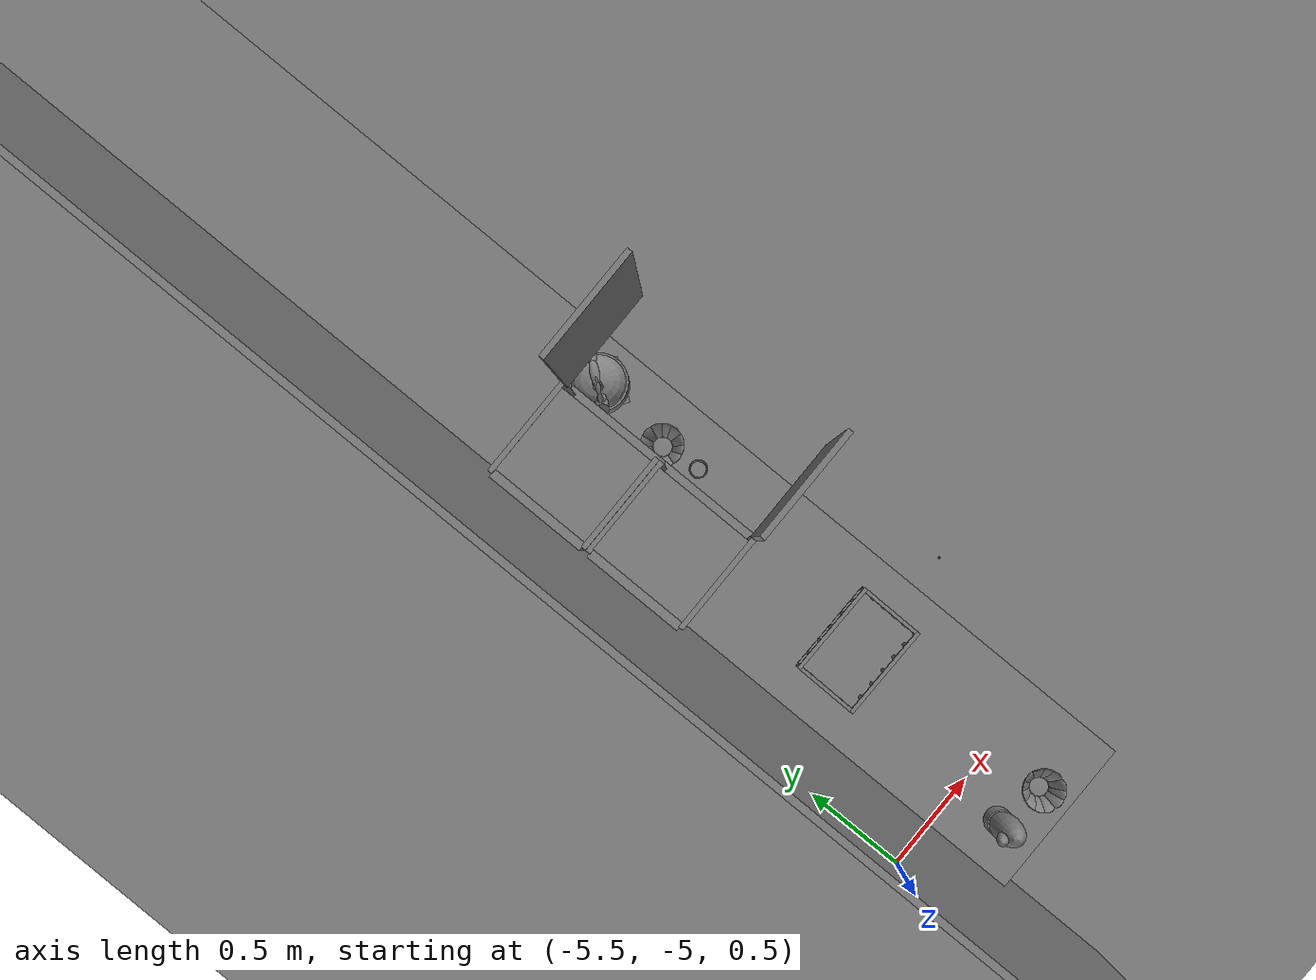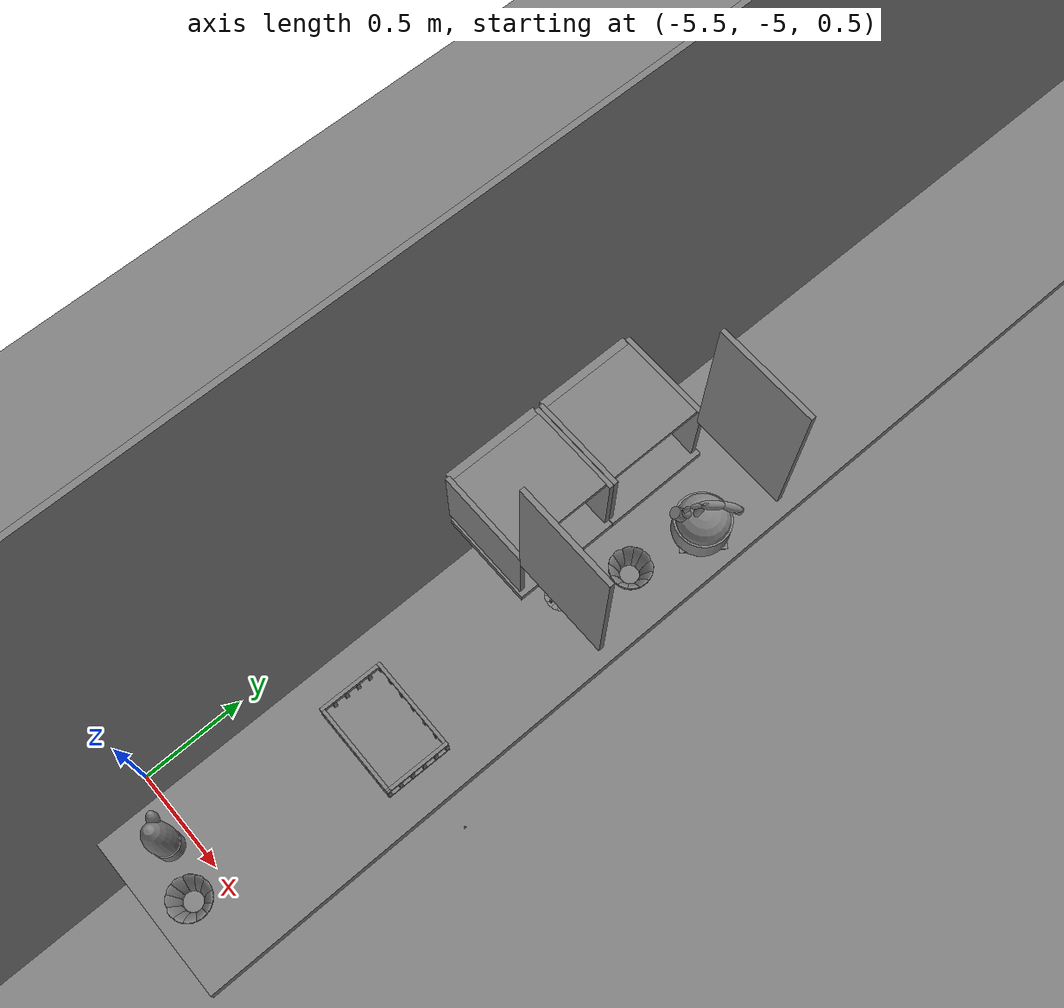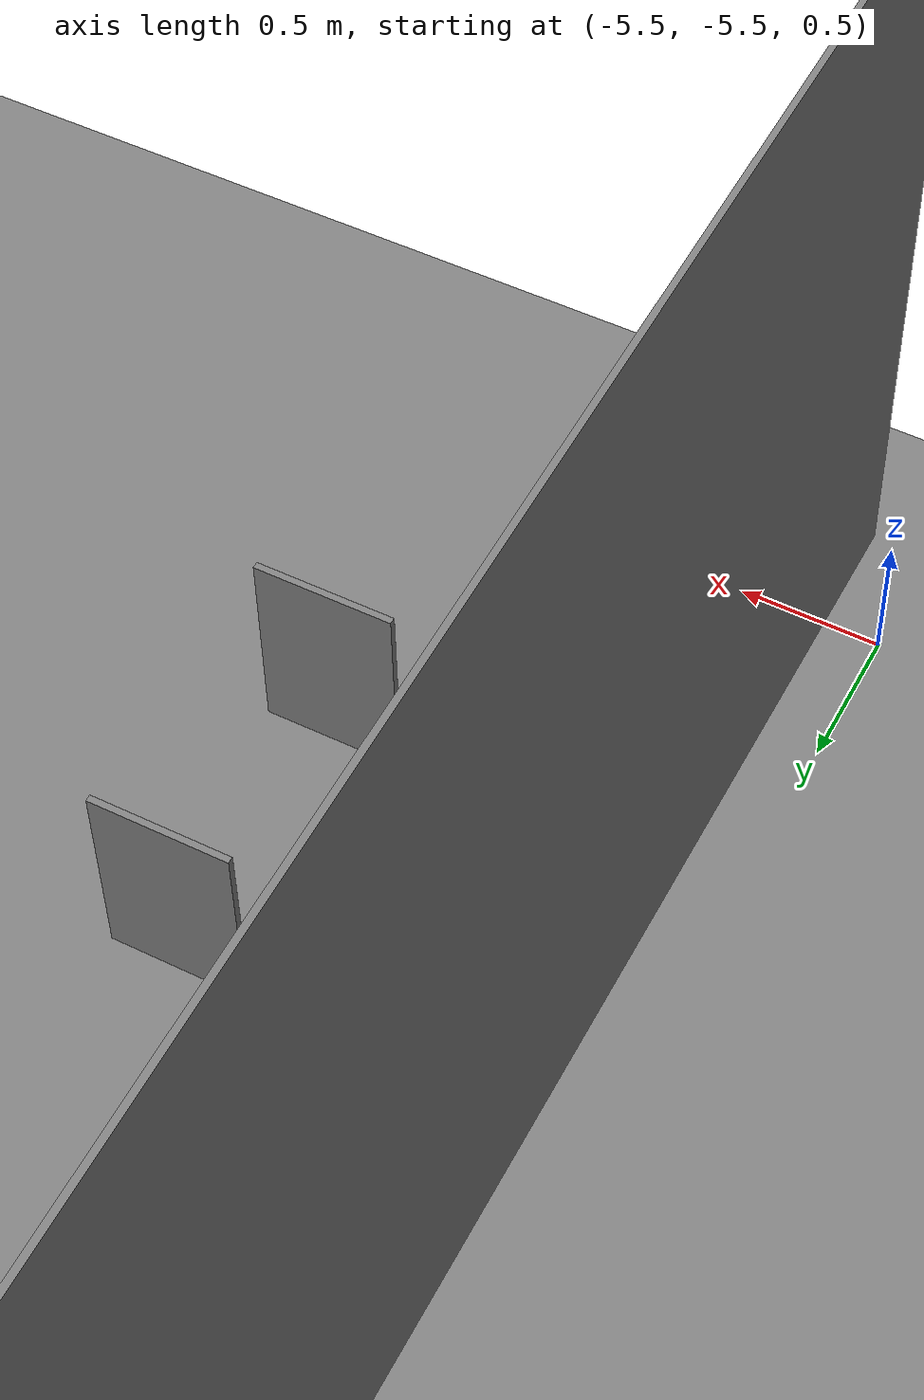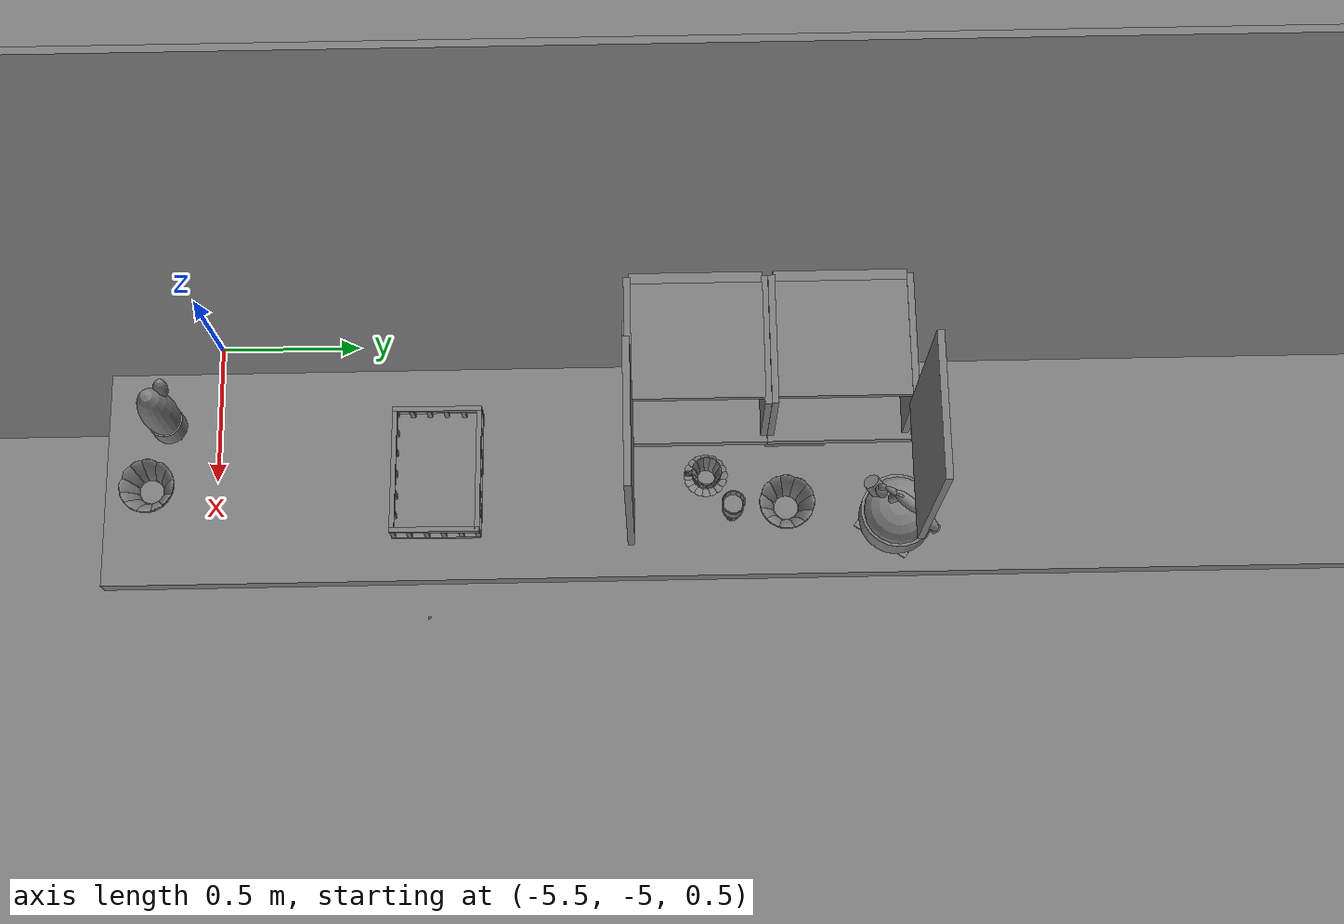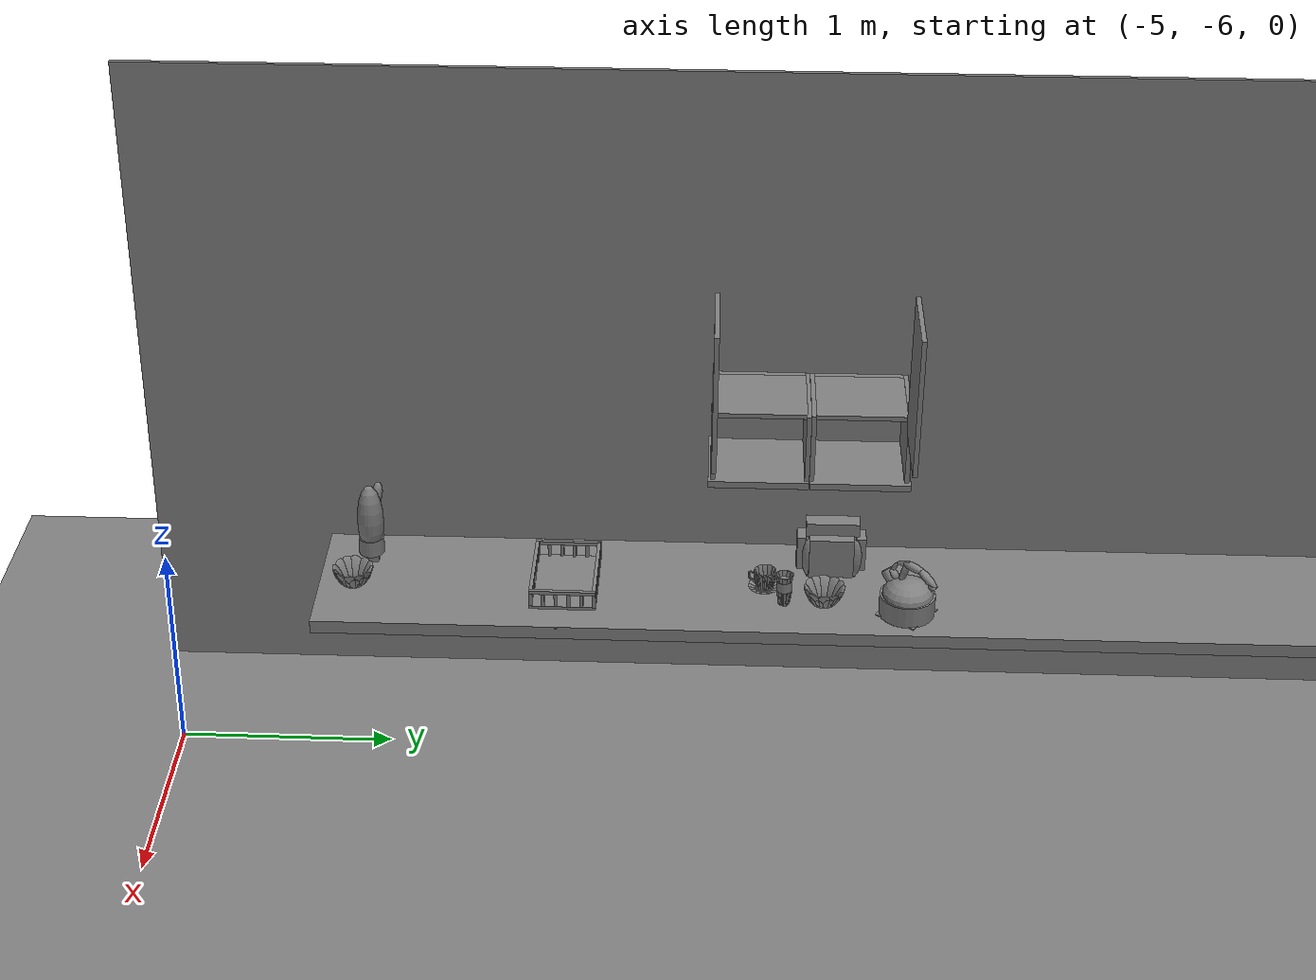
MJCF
<mujoco>
    <option gravity="0.000000000 0.000000000 -9.810000420" timestep="0.0049999999" integrator="implicitfast" density="9.8000002" viscosity="1.8000001e-05" noslip_iterations="10" iterations="100" sdf_iterations="50">
        <flag multiccd="disable"/>
    </option>
    <size memory="1000M"/>
    <compiler coordinate="local"/>
    <worldbody>
        <light cutoff="30" pos="0 1 1" dir="0 -1 -2"/>
        <light cutoff="30" pos="0 -1 1" dir="0 1 -2"/>
        <body pos="-5.046103477 -5.051773071 1.001502514" euler="0.000000000 0.000000000 0.000000000" name="Interactive Objcets_huapen">
            <geom contype="1" conaffinity="1" density="1000" type="ellipsoid" material="" rgba="0.500000000 0.500000000 0.500000000 1.000000000" solimp="0.899999976 0.949999988 0.001000000" friction="1.000000000 0.005000000 0.000100000" solref="0.020000000 1.000000000" margin="0" condim="3" group="0" pos="0.008062840 0.004346371 0.205056787" quat="1.000000000 0.000000000 0.000000000 0.000000000" size="0.059999999 0.059999999 0.180000007" name="Interactive Objcets_huapen_hua_1620B745_7D1B_4BB8_8183_7054E6CA73FD"/>
            <geom contype="1" conaffinity="1" density="1000" type="cylinder" material="" rgba="0.500000000 0.500000000 0.500000000 1.000000000" solimp="0.899999976 0.949999988 0.001000000" friction="1.000000000 0.005000000 0.000100000" solref="0.020000000 1.000000000" margin="0" condim="3" group="0" pos="0.008062840 0.003952026 0.080107450" quat="1.000000000 0.000000000 0.000000000 0.000000000" size="0.057999998 0.039999999 1.000000000" name="Interactive Objcets_huapen_hua_65729382_5CF8_4854_8226_16EBDB1B5E1E"/>
            <geom contype="1" conaffinity="1" density="1000" type="box" material="" rgba="0.500000000 0.500000000 0.500000000 1.000000000" solimp="0.899999976 0.949999988 0.001000000" friction="1.000000000 0.005000000 0.000100000" solref="0.020000000 1.000000000" margin="0" condim="3" group="0" pos="0.008062840 0.003952503 0.020566106" quat="1.000000000 0.000000000 0.000000000 0.000000000" size="0.035000000 0.035000000 0.020000000" name="Interactive Objcets_huapen_hua_D9F5576F_4AA5_4818_A342_F5BDF70B06EF"/>
            <geom contype="1" conaffinity="1" density="1000" type="ellipsoid" material="" rgba="0.500000000 0.500000000 0.500000000 1.000000000" solimp="0.899999976 0.949999988 0.001000000" friction="1.000000000 0.005000000 0.000100000" solref="0.020000000 1.000000000" margin="0" condim="3" group="0" pos="-0.029900074 0.033599377 0.321917295" quat="0.992658079 -0.083605267 -0.087364964 0.002748166" size="0.025000000 0.025000000 0.059999999" name="Interactive Objcets_huapen_hua_3E82101D_0423_429F_BD8C_8AD2683B1DE9"/>
            <freejoint name="Interactive Objcets_huapen"/>
        </body>
        <body pos="1000.000000000 1000.000000000 1.000000000" euler="0.000000000 0.000000000 0.000000000" name="openloong_gripper_2f85_fix_base_usda_salt">
            <geom contype="1" conaffinity="1" density="1000" type="box" material="" rgba="0.500000000 0.500000000 0.500000000 1.000000000" solimp="0.899999976 0.949999988 0.001000000" friction="1.000000000 0.005000000 0.000100000" solref="0.020000000 1.000000000" margin="0" condim="3" group="0" pos="0.000305176 0.000000000 0.084862232" quat="1.000000000 0.000000000 0.000000000 0.000000000" size="0.048999999 0.018999999 0.005000000" name="openloong_gripper_2f85_fix_base_usda_geom_E9BD4A8F_6ADE_4F4B_9755_0BF88BB8250E"/>
            <geom contype="1" conaffinity="1" density="1000" type="box" material="" rgba="0.500000000 0.500000000 0.500000000 1.000000000" solimp="0.899999976 0.949999988 0.001000000" friction="1.000000000 0.005000000 0.000100000" solref="0.020000000 1.000000000" margin="0" condim="3" group="0" pos="0.000305176 0.000000000 0.104564309" quat="1.000000000 0.000000000 0.000000000 0.000000000" size="0.052000001 0.014000000 0.005000000" name="openloong_gripper_2f85_fix_base_usda_geom_6FD0C5E8_FB57_45C3_BBAA_56911441156F"/>
            <geom contype="1" conaffinity="1" density="1000" type="box" material="" rgba="0.500000000 0.500000000 0.500000000 1.000000000" solimp="0.899999976 0.949999988 0.001000000" friction="1.000000000 0.005000000 0.000100000" solref="0.020000000 1.000000000" margin="0" condim="3" group="0" pos="0.000305176 0.000000000 0.114487171" quat="1.000000000 0.000000000 0.000000000 0.000000000" size="0.054000001 0.011500000 0.005000000" name="openloong_gripper_2f85_fix_base_usda_geom_0A6141B1_EF43_4564_B30B_D49C5876CAB4"/>
            <geom contype="1" conaffinity="1" density="1000" type="box" material="" rgba="0.500000000 0.500000000 0.500000000 1.000000000" solimp="0.899999976 0.949999988 0.001000000" friction="1.000000000 0.005000000 0.000100000" solref="0.020000000 1.000000000" margin="0" condim="3" group="0" pos="0.000305176 0.000000000 0.075103164" quat="1.000000000 0.000000000 0.000000000 0.000000000" size="0.048000000 0.020000000 0.005000000" name="openloong_gripper_2f85_fix_base_usda_geom_20E4F83B_3D03_4DEE_A66A_0A0D9CE816AC"/>
            <geom contype="1" conaffinity="1" density="1000" type="box" material="" rgba="0.500000000 0.500000000 0.500000000 1.000000000" solimp="0.899999976 0.949999988 0.001000000" friction="1.000000000 0.005000000 0.000100000" solref="0.020000000 1.000000000" margin="0" condim="3" group="0" pos="0.000305176 0.000000000 0.134892464" quat="1.000000000 0.000000000 0.000000000 0.000000000" size="0.057000000 0.007000000 0.005000000" name="openloong_gripper_2f85_fix_base_usda_geom_3C4F342D_D35C_48A2_9581_1D5EFBE79560"/>
            <geom contype="1" conaffinity="1" density="1000" type="box" material="" rgba="0.500000000 0.500000000 0.500000000 1.000000000" solimp="0.899999976 0.949999988 0.001000000" friction="1.000000000 0.005000000 0.000100000" solref="0.020000000 1.000000000" margin="0" condim="3" group="0" pos="0.000305176 0.000000000 0.094920278" quat="1.000000000 0.000000000 0.000000000 0.000000000" size="0.050000001 0.017000001 0.005000000" name="openloong_gripper_2f85_fix_base_usda_geom_7FBA4934_6A18_49CF_A5B6_DBEE093842DB"/>
            <geom contype="1" conaffinity="1" density="1000" type="box" material="" rgba="0.500000000 0.500000000 0.500000000 1.000000000" solimp="0.899999976 0.949999988 0.001000000" friction="1.000000000 0.005000000 0.000100000" solref="0.020000000 1.000000000" margin="0" condim="3" group="0" pos="0.000305176 0.000000000 0.065204859" quat="1.000000000 0.000000000 0.000000000 0.000000000" size="0.045000002 0.021000000 0.005000000" name="openloong_gripper_2f85_fix_base_usda_geom_DDABE391_0B04_42DA_818D_51B0DC869E0E"/>
            <geom contype="1" conaffinity="1" density="1000" type="box" material="" rgba="0.500000000 0.500000000 0.500000000 1.000000000" solimp="0.899999976 0.949999988 0.001000000" friction="1.000000000 0.005000000 0.000100000" solref="0.020000000 1.000000000" margin="0" condim="3" group="0" pos="0.000305176 0.000000000 0.144135714" quat="1.000000000 0.000000000 0.000000000 0.000000000" size="0.059000000 0.005000000 0.004000000" name="openloong_gripper_2f85_fix_base_usda_geom_1928F30D_48C6_4263_8A62_372931FD5418"/>
            <geom contype="1" conaffinity="1" density="1000" type="box" material="" rgba="0.500000000 0.500000000 0.500000000 1.000000000" solimp="0.899999976 0.949999988 0.001000000" friction="1.000000000 0.005000000 0.000100000" solref="0.020000000 1.000000000" margin="0" condim="3" group="0" pos="0.000000000 0.000000000 0.031593561" quat="1.000000000 0.000000000 0.000000000 0.000000000" size="0.041999999 0.024000000 0.029999999" name="openloong_gripper_2f85_fix_base_usda_geom_D5A0EC01_AC65_4A3B_86F1_B03FD3FDD022"/>
            <geom contype="1" conaffinity="1" density="1000" type="box" material="" rgba="0.500000000 0.500000000 0.500000000 1.000000000" solimp="0.899999976 0.949999988 0.001000000" friction="1.000000000 0.005000000 0.000100000" solref="0.020000000 1.000000000" margin="0" condim="3" group="0" pos="0.000305176 0.000000000 0.124608755" quat="1.000000000 0.000000000 0.000000000 0.000000000" size="0.055000000 0.008000000 0.005000000" name="openloong_gripper_2f85_fix_base_usda_geom_CEC17455_CC46_40EF_A2DA_2ABF6664EB60"/>
            <freejoint name="openloong_gripper_2f85_fix_base_usda_salt_joint"/>
            <site size="0.005000000 0.005000000 0.005000000" rgba="0.500000000 0.500000000 0.500000000 1.000000000" pos="0.000000000 0.000000000 0.000000000" quat="1.000000000 0.000000000 0.000000000 0.000000000" group="0" type="sphere" name="openloong_gripper_2f85_fix_base_usda_saltsite"/>
        </body>
        <body pos="1000.000000000 1000.000000000 1.000000000" euler="0.000000000 0.000000000 0.000000000" name="openloong_gripper_2f85_fix_base_usda_bow_yellow_kps">
            <geom contype="1" conaffinity="1" density="1000" type="ellipsoid" material="" rgba="0.500000000 0.500000000 0.500000000 1.000000000" solimp="0.899999976 0.949999988 0.001000000" friction="1.000000000 0.005000000 0.000100000" solref="0.020000000 1.000000000" margin="0" condim="3" group="0" pos="-0.052185059 0.040283203 0.044118762" quat="0.919264615 -0.076883033 -0.225593656 -0.313287765" size="0.010000000 0.039999999 0.052000001" name="openloong_gripper_2f85_fix_base_usda_geom_2BB29391_ADB7_484D_9F83_5C0C6BF45D3B"/>
            <geom contype="1" conaffinity="1" density="1000" type="ellipsoid" material="" rgba="0.500000000 0.500000000 0.500000000 1.000000000" solimp="0.899999976 0.949999988 0.001000000" friction="1.000000000 0.005000000 0.000100000" solref="0.020000000 1.000000000" margin="0" condim="3" group="0" pos="-0.000061035 0.065979004 0.044118762" quat="0.687598765 -0.168314874 -0.168741167 -0.685860336" size="0.010000000 0.039999999 0.052000001" name="openloong_gripper_2f85_fix_base_usda_geom_A4BD177A_4E89_426D_86E4_FBC7C14BF36C"/>
            <geom contype="1" conaffinity="1" density="1000" type="box" material="" rgba="0.500000000 0.500000000 0.500000000 1.000000000" solimp="0.899999976 0.949999988 0.001000000" friction="1.000000000 0.005000000 0.000100000" solref="0.020000000 1.000000000" margin="0" condim="3" group="0" pos="0.000061035 0.000000000 -0.002001643" quat="1.000000000 0.000000000 0.000000000 0.000000000" size="0.029999999 0.029999999 0.002000000" name="openloong_gripper_2f85_fix_base_usda_geom_A89BD101_5841_4D3D_BB04_5E0E25354E37"/>
            <geom contype="1" conaffinity="1" density="1000" type="ellipsoid" material="" rgba="0.500000000 0.500000000 0.500000000 1.000000000" solimp="0.899999976 0.949999988 0.001000000" friction="1.000000000 0.005000000 0.000100000" solref="0.020000000 1.000000000" margin="0" condim="3" group="0" pos="0.029418945 -0.059082031 0.044118762" quat="0.825555861 0.125530601 0.202597082 -0.511521280" size="0.010000000 0.039999999 0.052000001" name="openloong_gripper_2f85_fix_base_usda_geom_6D39D629_E8C0_4E78_ABF3_ACF65AF85317"/>
            <geom contype="1" conaffinity="1" density="1000" type="ellipsoid" material="" rgba="0.500000000 0.500000000 0.500000000 1.000000000" solimp="0.899999976 0.949999988 0.001000000" friction="1.000000000 0.005000000 0.000100000" solref="0.020000000 1.000000000" margin="0" condim="3" group="0" pos="0.000244141 -0.065979004 0.044118762" quat="0.687598765 0.168314651 0.168741375 -0.685860336" size="0.010000000 0.039999999 0.052000001" name="openloong_gripper_2f85_fix_base_usda_geom_69ECD1E6_1768_414E_9A08_A4EFB5375F18"/>
            <geom contype="1" conaffinity="1" density="1000" type="ellipsoid" material="" rgba="0.500000000 0.500000000 0.500000000 1.000000000" solimp="0.899999976 0.949999988 0.001000000" friction="1.000000000 0.005000000 0.000100000" solref="0.020000000 1.000000000" margin="0" condim="3" group="0" pos="0.000061035 0.000000000 0.000446677" quat="1.000000000 0.000000000 0.000000000 0.000000000" size="0.039999999 0.039999999 0.002000000" name="openloong_gripper_2f85_fix_base_usda_geom_C15E504C_F49A_444F_BD1A_9EB18553ACDF"/>
            <geom contype="1" conaffinity="1" density="1000" type="ellipsoid" material="" rgba="0.500000000 0.500000000 0.500000000 1.000000000" solimp="0.899999976 0.949999988 0.001000000" friction="1.000000000 0.005000000 0.000100000" solref="0.020000000 1.000000000" margin="0" condim="3" group="0" pos="0.059082031 0.029541016 0.044118762" quat="0.223252773 -0.231952220 -0.054787423 -0.945174456" size="0.010000000 0.039999999 0.052000001" name="openloong_gripper_2f85_fix_base_usda_geom_FBFE5DCA_65BC_4F62_BB67_2327CC607DD3"/>
            <geom contype="1" conaffinity="1" density="1000" type="ellipsoid" material="" rgba="0.500000000 0.500000000 0.500000000 1.000000000" solimp="0.899999976 0.949999988 0.001000000" friction="1.000000000 0.005000000 0.000100000" solref="0.020000000 1.000000000" margin="0" condim="3" group="0" pos="0.000061035 0.000000000 0.007335305" quat="1.000000000 0.000000000 0.000000000 0.000000000" size="0.039999999 0.039999999 0.002000000" name="openloong_gripper_2f85_fix_base_usda_geom_1574D0CF_8EC6_4E40_BB82_67A95441A779"/>
            <geom contype="1" conaffinity="1" density="1000" type="ellipsoid" material="" rgba="0.500000000 0.500000000 0.500000000 1.000000000" solimp="0.899999976 0.949999988 0.001000000" friction="1.000000000 0.005000000 0.000100000" solref="0.020000000 1.000000000" margin="0" condim="3" group="0" pos="-0.029296875 0.059082031 0.044118762" quat="0.825555861 -0.125530809 -0.202596918 -0.511521280" size="0.010000000 0.039999999 0.052000001" name="openloong_gripper_2f85_fix_base_usda_geom_5057DB2F_4C8C_461B_8AAA_3F43CEFAFC11"/>
            <geom contype="1" conaffinity="1" density="1000" type="ellipsoid" material="" rgba="0.500000000 0.500000000 0.500000000 1.000000000" solimp="0.899999976 0.949999988 0.001000000" friction="1.000000000 0.005000000 0.000100000" solref="0.020000000 1.000000000" margin="0" condim="3" group="0" pos="0.040222168 0.052368164 0.044118762" quat="0.429593176 -0.213750049 -0.105424821 -0.871002972" size="0.010000000 0.039999999 0.052000001" name="openloong_gripper_2f85_fix_base_usda_geom_54E0C2A7_4866_4A09_8265_9A28CF612562"/>
            <geom contype="1" conaffinity="1" density="1000" type="ellipsoid" material="" rgba="0.500000000 0.500000000 0.500000000 1.000000000" solimp="0.899999976 0.949999988 0.001000000" friction="1.000000000 0.005000000 0.000100000" solref="0.020000000 1.000000000" margin="0" condim="3" group="0" pos="0.066040039 0.000000000 0.044118762" quat="0.971183062 -0.000000156 0.238334835 0.000000030" size="0.010000000 0.039999999 0.052000001" name="openloong_gripper_2f85_fix_base_usda_geom_CC6BF317_9FDA_4F64_843F_47BA48CD26D0"/>
            <geom contype="1" conaffinity="1" density="1000" type="ellipsoid" material="" rgba="0.500000000 0.500000000 0.500000000 1.000000000" solimp="0.899999976 0.949999988 0.001000000" friction="1.000000000 0.005000000 0.000100000" solref="0.020000000 1.000000000" margin="0" condim="3" group="0" pos="0.052307129 -0.040283203 0.044118762" quat="0.919264674 0.076882750 0.225593731 -0.313287705" size="0.010000000 0.039999999 0.052000001" name="openloong_gripper_2f85_fix_base_usda_geom_456ACD40_7802_47C6_A97B_59EDFA81452C"/>
            <geom contype="1" conaffinity="1" density="1000" type="ellipsoid" material="" rgba="0.500000000 0.500000000 0.500000000 1.000000000" solimp="0.899999976 0.949999988 0.001000000" friction="1.000000000 0.005000000 0.000100000" solref="0.020000000 1.000000000" margin="0" condim="3" group="0" pos="-0.065917969 0.000000000 0.044118762" quat="0.971183062 -0.000000142 -0.238334835 0.000000030" size="0.010000000 0.039999999 0.052000001" name="openloong_gripper_2f85_fix_base_usda_geom_986053A8_9C52_4339_AE9A_8BBEA71943DD"/>
            <geom contype="1" conaffinity="1" density="1000" type="ellipsoid" material="" rgba="0.500000000 0.500000000 0.500000000 1.000000000" solimp="0.899999976 0.949999988 0.001000000" friction="1.000000000 0.005000000 0.000100000" solref="0.020000000 1.000000000" margin="0" condim="3" group="0" pos="-0.058898926 -0.029541016 0.044118762" quat="0.223252758 0.231952101 0.054787733 -0.945174575" size="0.010000000 0.039999999 0.052000001" name="openloong_gripper_2f85_fix_base_usda_geom_A7EB9756_A139_412B_908B_1C353CF4422F"/>
            <geom contype="1" conaffinity="1" density="1000" type="ellipsoid" material="" rgba="0.500000000 0.500000000 0.500000000 1.000000000" solimp="0.899999976 0.949999988 0.001000000" friction="1.000000000 0.005000000 0.000100000" solref="0.020000000 1.000000000" margin="0" condim="3" group="0" pos="-0.040100098 -0.052368164 0.044118762" quat="0.429593235 0.213749886 0.105425082 -0.871003032" size="0.010000000 0.039999999 0.052000001" name="openloong_gripper_2f85_fix_base_usda_geom_8DBA48F4_D4E1_4BFA_9227_45268BE6C0EA"/>
            <freejoint name="openloong_gripper_2f85_fix_base_usda_bow_yellow_kps_joint"/>
            <site size="0.005000000 0.005000000 0.005000000" rgba="0.500000000 0.500000000 0.500000000 1.000000000" pos="0.000000000 0.000000000 0.000000000" quat="0.999961913 0.008726534 0.000000000 0.000000000" group="0" type="sphere" name="openloong_gripper_2f85_fix_base_usda_bow_yellow_kps"/>
        </body>
        <body pos="1000.000000000 1000.000000000 1.000000000" euler="0.000000000 0.000000000 0.000000000" name="openloong_gripper_2f85_fix_base_usda_jar_01">
            <geom contype="1" conaffinity="1" density="1000" type="box" material="" rgba="0.500000000 0.500000000 0.500000000 1.000000000" solimp="0.899999976 0.949999988 0.001000000" friction="1.000000000 0.005000000 0.000100000" solref="0.020000000 1.000000000" margin="0" condim="3" group="0" pos="0.000000000 0.000000000 0.006158113" quat="1.000000000 0.000000000 0.000000000 0.000000000" size="0.020000000 0.020000000 0.005000000" name="openloong_gripper_2f85_fix_base_usda_geom_E51481DE_F7DD_4E9D_B2D7_B43E8F4CB464"/>
            <geom contype="1" conaffinity="1" density="1000" type="cylinder" material="" rgba="0.500000000 0.500000000 0.500000000 1.000000000" solimp="0.899999976 0.949999988 0.001000000" friction="1.000000000 0.005000000 0.000100000" solref="0.020000000 1.000000000" margin="0" condim="3" group="0" pos="0.000000000 0.000000000 0.062744498" quat="1.000000000 0.000000000 0.000000000 0.000000000" size="0.041000001 0.052999999 1.000000000" name="openloong_gripper_2f85_fix_base_usda_geom_46D5D582_7159_4C59_A991_41E8E86202AB"/>
            <geom contype="1" conaffinity="1" density="1000" type="ellipsoid" material="" rgba="0.500000000 0.500000000 0.500000000 1.000000000" solimp="0.899999976 0.949999988 0.001000000" friction="1.000000000 0.005000000 0.000100000" solref="0.020000000 1.000000000" margin="0" condim="3" group="0" pos="0.000000000 0.000000000 0.122252703" quat="1.000000000 0.000000000 0.000000000 0.000000000" size="0.035999998 0.035999998 0.010000000" name="openloong_gripper_2f85_fix_base_usda_geom_AF9400BF_FBCC_4165_B709_FE0682B082F0"/>
            <geom contype="1" conaffinity="1" density="1000" type="cylinder" material="" rgba="0.500000000 0.500000000 0.500000000 1.000000000" solimp="0.899999976 0.949999988 0.001000000" friction="1.000000000 0.005000000 0.000100000" solref="0.020000000 1.000000000" margin="0" condim="3" group="0" pos="0.000000000 0.000000000 0.015747190" quat="1.000000000 0.000000000 0.000000000 0.000000000" size="0.035000000 0.010000000 1.000000000" name="openloong_gripper_2f85_fix_base_usda_geom_C4D498E9_B88B_44EB_933F_F8E5B678585A"/>
            <geom contype="1" conaffinity="1" density="1000" type="ellipsoid" material="" rgba="0.500000000 0.500000000 0.500000000 1.000000000" solimp="0.899999976 0.949999988 0.001000000" friction="1.000000000 0.005000000 0.000100000" solref="0.020000000 1.000000000" margin="0" condim="3" group="0" pos="0.000000000 0.000000000 0.115815401" quat="1.000000000 0.000000000 0.000000000 0.000000000" size="0.039999999 0.039999999 0.010000000" name="openloong_gripper_2f85_fix_base_usda_geom_ED88CDDB_1C8F_4CB6_9836_717652AAA5D3"/>
            <geom contype="1" conaffinity="1" density="1000" type="cylinder" material="" rgba="0.500000000 0.500000000 0.500000000 1.000000000" solimp="0.899999976 0.949999988 0.001000000" friction="1.000000000 0.005000000 0.000100000" solref="0.020000000 1.000000000" margin="0" condim="3" group="0" pos="0.000000000 0.000000000 0.133183479" quat="1.000000000 0.000000000 0.000000000 0.000000000" size="0.037999999 0.006500000 1.000000000" name="openloong_gripper_2f85_fix_base_usda_geom_A92781FD_31DB_453C_913E_9846120C1856"/>
            <freejoint name="openloong_gripper_2f85_fix_base_usda_jar_01_joint"/>
            <site size="0.005000000 0.005000000 0.005000000" rgba="0.500000000 0.500000000 0.500000000 1.000000000" pos="0.000000000 0.000000000 0.000000000" quat="1.000000000 0.000000000 0.000000000 0.000000000" group="0" type="sphere" name="openloong_gripper_2f85_fix_base_usda_jar_01site"/>
        </body>
        <body pos="1000.000000000 1000.000000000 1.000000000" euler="0.000000000 0.000000000 0.000000000" name="openloong_gripper_2f85_fix_base_usda_bottle_red">
            <geom contype="1" conaffinity="1" density="1000" type="ellipsoid" material="" rgba="0.500000000 0.500000000 0.500000000 1.000000000" solimp="0.899999976 0.949999988 0.001000000" friction="1.000000000 0.005000000 0.000100000" solref="0.020000000 1.000000000" margin="0" condim="3" group="0" pos="0.000000000 0.000000000 0.144284487" quat="1.000000000 0.000000000 0.000000000 0.000000000" size="0.021000000 0.021000000 0.079999998" name="openloong_gripper_2f85_fix_base_usda_geom_9D812AF1_B415_4A4F_B3BB_9E15BE8909FF"/>
            <geom contype="1" conaffinity="1" density="1000" type="cylinder" material="" rgba="0.500000000 0.500000000 0.500000000 1.000000000" solimp="0.899999976 0.949999988 0.001000000" friction="1.000000000 0.005000000 0.000100000" solref="0.020000000 1.000000000" margin="0" condim="3" group="0" pos="0.000000000 0.000000000 0.220618963" quat="1.000000000 0.000000000 0.000000000 0.000000000" size="0.016000001 0.010000000 1.000000000" name="openloong_gripper_2f85_fix_base_usda_geom_90D53E9B_9285_4EFF_93D6_024AE4239872"/>
            <geom contype="1" conaffinity="1" density="1000" type="ellipsoid" material="" rgba="0.500000000 0.500000000 0.500000000 1.000000000" solimp="0.899999976 0.949999988 0.001000000" friction="1.000000000 0.005000000 0.000100000" solref="0.020000000 1.000000000" margin="0" condim="3" group="0" pos="0.000000000 0.000000000 0.118945479" quat="1.000000000 0.000000000 0.000000000 0.000000000" size="0.030999999 0.030999999 0.029999999" name="openloong_gripper_2f85_fix_base_usda_geom_2E9374E4_FED4_4C13_AE8A_E22415109B89"/>
            <geom contype="1" conaffinity="1" density="1000" type="box" material="" rgba="0.500000000 0.500000000 0.500000000 1.000000000" solimp="0.899999976 0.949999988 0.001000000" friction="1.000000000 0.005000000 0.000100000" solref="0.020000000 1.000000000" margin="0" condim="3" group="0" pos="0.000000000 0.000000000 0.002189159" quat="1.000000000 0.000000000 0.000000000 0.000000000" size="0.020000000 0.020000000 0.003000000" name="openloong_gripper_2f85_fix_base_usda_geom_BA072CD5_94D1_4661_BEA4_ABC0AD43AB31"/>
            <geom contype="1" conaffinity="1" density="1000" type="cylinder" material="" rgba="0.500000000 0.500000000 0.500000000 1.000000000" solimp="0.899999976 0.949999988 0.001000000" friction="1.000000000 0.005000000 0.000100000" solref="0.020000000 1.000000000" margin="0" condim="3" group="0" pos="0.000000000 -0.000366211 0.060884237" quat="1.000000000 0.000000000 0.000000000 0.000000000" size="0.030999999 0.057999998 1.000000000" name="openloong_gripper_2f85_fix_base_usda_geom_0E960328_65C7_42D6_96FD_E8CFA121B891"/>
            <freejoint name="openloong_gripper_2f85_fix_base_usda_bottle_red_joint"/>
            <site size="0.005000000 0.005000000 0.005000000" rgba="0.500000000 0.500000000 0.500000000 1.000000000" pos="0.000000000 0.000000000 0.000000000" quat="0.999961913 0.008726535 0.000000000 0.000000000" group="0" type="sphere" name="openloong_gripper_2f85_fix_base_usda_bottle_redsite"/>
        </body>
        <body pos="-4.292066574 -4.626472950 1.868246317" euler="-34.036163330 -86.128746033 16.422468185" mocap="true" name="spotlight1_SpotLight"/>
        <body pos="-4.435558319 -3.674623251 1.842736125" euler="128.463867188 -28.396200180 -123.938529968" mocap="true" name="spotlight6_SpotLight"/>
        <body pos="-4.426210880 -4.116869926 1.762325525" euler="-72.996459961 10.108890533 -120.688125610" mocap="true" name="spotlight3_SpotLight"/>
        <body pos="1000.000000000 1000.000000000 1.000000000" euler="0.000000000 0.000000000 0.000000000" name="openloong_gripper_2f85_fix_base_usda_coffeecup_white_kps">
            <geom contype="1" conaffinity="1" density="1000" type="capsule" material="" rgba="0.500000000 0.500000000 0.500000000 1.000000000" solimp="0.899999976 0.949999988 0.001000000" friction="1.000000000 0.005000000 0.000100000" solref="0.020000000 1.000000000" margin="0" condim="3" group="0" pos="-0.000854492 -0.065795898 0.050029993" quat="0.343559504 -0.613204718 0.626912475 0.336047262" size="0.004000000 0.005000000 1.000000000" name="openloong_gripper_2f85_fix_base_usda_geom_0F858C2E_5EC8_4E16_B152_D99CF45EE77C"/>
            <geom contype="1" conaffinity="1" density="1000" type="ellipsoid" material="" rgba="0.500000000 0.500000000 0.500000000 1.000000000" solimp="0.899999976 0.949999988 0.001000000" friction="1.000000000 0.005000000 0.000100000" solref="0.020000000 1.000000000" margin="0" condim="3" group="0" pos="-0.000793457 -0.038452148 0.048040152" quat="0.711656272 0.066323131 -0.067805752 0.696095467" size="0.005000000 0.029999999 0.048999999" name="openloong_gripper_2f85_fix_base_usda_geom_6B3F9E43_CC16_4E15_A099_114DD7DD73A8"/>
            <geom contype="1" conaffinity="1" density="1000" type="ellipsoid" material="" rgba="0.500000000 0.500000000 0.500000000 1.000000000" solimp="0.899999976 0.949999988 0.001000000" friction="1.000000000 0.005000000 0.000100000" solref="0.020000000 1.000000000" margin="0" condim="3" group="0" pos="0.037719727 -0.001892090 0.048040152" quat="0.995387912 0.001371633 0.094835162 -0.014391154" size="0.005000000 0.029999999 0.048999999" name="openloong_gripper_2f85_fix_base_usda_geom_EC0386AC_8B36_419A_B27A_902EE2D66D48"/>
            <geom contype="1" conaffinity="1" density="1000" type="ellipsoid" material="" rgba="0.500000000 0.500000000 0.500000000 1.000000000" solimp="0.899999976 0.949999988 0.001000000" friction="1.000000000 0.005000000 0.000100000" solref="0.020000000 1.000000000" margin="0" condim="3" group="0" pos="0.033996582 0.015502930 0.048040152" quat="0.970659733 -0.021051638 0.092478797 0.220962167" size="0.005000000 0.029999999 0.048999999" name="openloong_gripper_2f85_fix_base_usda_geom_BA0E03E2_7571_4551_8BA0_A913A00E0565"/>
            <geom contype="1" conaffinity="1" density="1000" type="box" material="" rgba="0.500000000 0.500000000 0.500000000 1.000000000" solimp="0.899999976 0.949999988 0.001000000" friction="1.000000000 0.005000000 0.000100000" solref="0.020000000 1.000000000" margin="0" condim="3" group="0" pos="0.000793457 -0.000183105 0.000156164" quat="0.714879215 0.000000000 0.000000000 0.699247897" size="0.020000000 0.020000000 0.002000000" name="openloong_gripper_2f85_fix_base_usda_geom_CE5AF75B_69E5_42DA_BEC9_E6745E5F670C"/>
            <geom contype="1" conaffinity="1" density="1000" type="ellipsoid" material="" rgba="0.500000000 0.500000000 0.500000000 1.000000000" solimp="0.899999976 0.949999988 0.001000000" friction="1.000000000 0.005000000 0.000100000" solref="0.020000000 1.000000000" margin="0" condim="3" group="0" pos="-0.019409180 -0.033081055 0.048040152" quat="0.866879702 0.046630561 -0.082595348 0.489411235" size="0.005000000 0.029999999 0.048999999" name="openloong_gripper_2f85_fix_base_usda_geom_E639D385_CB07_44E3_8923_788724553E64"/>
            <geom contype="1" conaffinity="1" density="1000" type="ellipsoid" material="" rgba="0.500000000 0.500000000 0.500000000 1.000000000" solimp="0.899999976 0.949999988 0.001000000" friction="1.000000000 0.005000000 0.000100000" solref="0.020000000 1.000000000" margin="0" condim="3" group="0" pos="-0.016052246 0.033264160 0.048040152" quat="0.840792537 -0.050782297 -0.080109790 -0.532983541" size="0.005000000 0.029999999 0.048999999" name="openloong_gripper_2f85_fix_base_usda_geom_F8477868_98ED_4997_8CF7_561C84435931"/>
            <geom contype="1" conaffinity="1" density="1000" type="capsule" material="" rgba="0.500000000 0.500000000 0.500000000 1.000000000" solimp="0.899999976 0.949999988 0.001000000" friction="1.000000000 0.005000000 0.000100000" solref="0.020000000 1.000000000" margin="0" condim="3" group="0" pos="-0.000549316 -0.053527832 0.046825886" quat="0.505496025 -0.494442940 0.505495846 0.494442940" size="0.004000000 0.005000000 1.000000000" name="openloong_gripper_2f85_fix_base_usda_geom_0FD61366_45F6_41A6_BD67_E7820F47E67E"/>
            <geom contype="1" conaffinity="1" density="1000" type="ellipsoid" material="" rgba="0.500000000 0.500000000 0.500000000 1.000000000" solimp="0.899999976 0.949999988 0.001000000" friction="1.000000000 0.005000000 0.000100000" solref="0.020000000 1.000000000" margin="0" condim="3" group="0" pos="-0.032104492 0.018920898 0.048040152" quat="0.958129764 -0.025742561 -0.091288343 -0.270168930" size="0.005000000 0.029999999 0.048999999" name="openloong_gripper_2f85_fix_base_usda_geom_64D82D8F_A9C6_4EF7_9E15_257BAB9F99A7"/>
            <geom contype="1" conaffinity="1" density="1000" type="ellipsoid" material="" rgba="0.500000000 0.500000000 0.500000000 1.000000000" solimp="0.899999976 0.949999988 0.001000000" friction="1.000000000 0.005000000 0.000100000" solref="0.020000000 1.000000000" margin="0" condim="3" group="0" pos="-0.037597656 0.000305176 0.048040152" quat="0.995387554 -0.001371440 -0.094839431 -0.014389008" size="0.005000000 0.029999999 0.048999999" name="openloong_gripper_2f85_fix_base_usda_geom_834DB148_2C21_4ECB_8721_AB68D7B81865"/>
            <geom contype="1" conaffinity="1" density="1000" type="capsule" material="" rgba="0.500000000 0.500000000 0.500000000 1.000000000" solimp="0.899999976 0.949999988 0.001000000" friction="1.000000000 0.005000000 0.000100000" solref="0.020000000 1.000000000" margin="0" condim="3" group="0" pos="-0.000366211 -0.043762207 0.044118762" quat="0.260488123 -0.651174724 0.665731549 0.254792154" size="0.004000000 0.003000000 1.000000000" name="openloong_gripper_2f85_fix_base_usda_geom_66CC1297_65EA_4D13_8C64_EFF6147FAB75"/>
            <geom contype="1" conaffinity="1" density="1000" type="capsule" material="" rgba="0.500000000 0.500000000 0.500000000 1.000000000" solimp="0.899999976 0.949999988 0.001000000" friction="1.000000000 0.005000000 0.000100000" solref="0.020000000 1.000000000" margin="0" condim="3" group="0" pos="-0.000915527 -0.068542480 0.082936406" quat="0.624995589 -0.339446366 0.347034454 0.611329615" size="0.004000000 0.004000000 1.000000000" name="openloong_gripper_2f85_fix_base_usda_geom_F1F1A2D0_C941_4BAA_9F02_25FC836B8C00"/>
            <geom contype="1" conaffinity="1" density="1000" type="ellipsoid" material="" rgba="0.500000000 0.500000000 0.500000000 1.000000000" solimp="0.899999976 0.949999988 0.001000000" friction="1.000000000 0.005000000 0.000100000" solref="0.020000000 1.000000000" margin="0" condim="3" group="0" pos="0.016113281 -0.034851074 0.048040152" quat="0.840793252 0.050779939 0.080106191 -0.532983422" size="0.005000000 0.029999999 0.048999999" name="openloong_gripper_2f85_fix_base_usda_geom_1811F532_2D0A_4202_B740_B0F37BB8DACA"/>
            <geom contype="1" conaffinity="1" density="1000" type="ellipsoid" material="" rgba="0.500000000 0.500000000 0.500000000 1.000000000" solimp="0.899999976 0.949999988 0.001000000" friction="1.000000000 0.005000000 0.000100000" solref="0.020000000 1.000000000" margin="0" condim="3" group="0" pos="0.000854492 0.036865234 0.048040152" quat="0.711656570 -0.066320375 0.067802906 0.696095705" size="0.005000000 0.029999999 0.048999999" name="openloong_gripper_2f85_fix_base_usda_geom_D49B2531_DEAE_4428_9905_C5566F5F137E"/>
            <geom contype="1" conaffinity="1" density="1000" type="ellipsoid" material="" rgba="0.500000000 0.500000000 0.500000000 1.000000000" solimp="0.899999976 0.949999988 0.001000000" friction="1.000000000 0.005000000 0.000100000" solref="0.020000000 1.000000000" margin="0" condim="3" group="0" pos="-0.033935547 -0.017089844 0.048040152" quat="0.970659137 0.021052625 -0.092483103 0.220962465" size="0.005000000 0.029999999 0.048999999" name="openloong_gripper_2f85_fix_base_usda_geom_85259B4C_35E1_4695_9AA6_9D3903CDF198"/>
            <geom contype="1" conaffinity="1" density="1000" type="ellipsoid" material="" rgba="0.500000000 0.500000000 0.500000000 1.000000000" solimp="0.899999976 0.949999988 0.001000000" friction="1.000000000 0.005000000 0.000100000" solref="0.020000000 1.000000000" margin="0" condim="3" group="0" pos="0.019531250 0.031494141 0.048040152" quat="0.866880119 -0.046628602 0.082591817 0.489411235" size="0.005000000 0.029999999 0.048999999" name="openloong_gripper_2f85_fix_base_usda_geom_8A037485_4283_4AF0_8CE4_70093E2B1525"/>
            <geom contype="1" conaffinity="1" density="1000" type="ellipsoid" material="" rgba="0.500000000 0.500000000 0.500000000 1.000000000" solimp="0.899999976 0.949999988 0.001000000" friction="1.000000000 0.005000000 0.000100000" solref="0.020000000 1.000000000" margin="0" condim="3" group="0" pos="0.032165527 -0.020507812 0.048040152" quat="0.958128154 0.025740955 0.091285400 -0.270175666" size="0.005000000 0.029999999 0.048999999" name="openloong_gripper_2f85_fix_base_usda_geom_2A3280C4_95CC_4563_890B_E093164E9D26"/>
            <geom contype="1" conaffinity="1" density="1000" type="capsule" material="" rgba="0.500000000 0.500000000 0.500000000 1.000000000" solimp="0.899999976 0.949999988 0.001000000" friction="1.000000000 0.005000000 0.000100000" solref="0.020000000 1.000000000" margin="0" condim="3" group="0" pos="-0.000610352 -0.056823730 0.083572865" quat="0.452654332 -0.541215360 0.553313971 0.442756712" size="0.004000000 0.009000000 1.000000000" name="openloong_gripper_2f85_fix_base_usda_geom_48335DC8_CFD5_4300_87F0_A8A74E346986"/>
            <geom contype="1" conaffinity="1" density="1000" type="ellipsoid" material="" rgba="0.500000000 0.500000000 0.500000000 1.000000000" solimp="0.899999976 0.949999988 0.001000000" friction="1.000000000 0.005000000 0.000100000" solref="0.020000000 1.000000000" margin="0" condim="3" group="0" pos="0.000061035 -0.000183105 0.001848221" quat="0.714879215 0.000000000 0.000000000 0.699247897" size="0.029999999 0.029999999 0.001000000" name="openloong_gripper_2f85_fix_base_usda_geom_B6921CAA_47E7_4A8C_A9C6_33A9C452629E"/>
            <geom contype="1" conaffinity="1" density="1000" type="capsule" material="" rgba="0.500000000 0.500000000 0.500000000 1.000000000" solimp="0.899999976 0.949999988 0.001000000" friction="1.000000000 0.005000000 0.000100000" solref="0.020000000 1.000000000" margin="0" condim="3" group="0" pos="-0.000976562 -0.071838379 0.066101432" quat="0.031849027 -0.698553741 0.714169443 0.031152546" size="0.004000000 0.012000000 1.000000000" name="openloong_gripper_2f85_fix_base_usda_geom_76F6AFA4_2BC5_4AB2_893E_5A13F5E8AA9C"/>
            <freejoint name="openloong_gripper_2f85_fix_base_usda_coffeecup_white_kps_joint"/>
            <site size="0.005000000 0.005000000 0.005000000" rgba="0.500000000 0.500000000 0.500000000 1.000000000" pos="0.000000000 0.000000000 0.000000000" quat="0.999961913 0.008726534 0.000000000 0.000000000" group="0" type="sphere" name="openloong_gripper_2f85_fix_base_usda_coffeecup_white_kps"/>
        </body>
        <body pos="0.000000000 0.000000000 0.000000000" euler="0.000000000 0.000000000 0.000000000" name="Static Objcets_Static Objcets">
            <geom contype="1" conaffinity="1" density="1000" type="box" material="" rgba="0.500000000 0.500000000 0.500000000 1.000000000" solimp="0.899999976 0.949999988 0.001000000" friction="1.000000000 0.005000000 0.000100000" solref="0.020000000 1.000000000" margin="0" condim="3" group="0" pos="-4.999745846 -3.497932911 1.764780521" quat="0.707107067 0.707106471 0.000000000 0.000000000" size="0.200000003 0.159999996 0.010000000" name="Static Objcets_geom_888E84AD_714D_4625_8E7C_542998DF23A4"/>
            <geom contype="1" conaffinity="1" density="1000" type="box" material="" rgba="0.500000000 0.500000000 0.500000000 1.000000000" solimp="0.899999976 0.949999988 0.001000000" friction="1.000000000 0.005000000 0.000100000" solref="0.020000000 1.000000000" margin="0" condim="3" group="0" pos="-4.979488373 -3.297635794 1.591412544" quat="0.707106829 0.707106709 0.000000000 0.000000000" size="0.200000003 0.015000000 0.219999999" name="Static Objcets_geom_6DB9CB6D_F310_4CBA_A8D5_016B3E2F3182"/>
            <geom contype="1" conaffinity="1" density="1000" type="box" material="" rgba="0.500000000 0.500000000 0.500000000 1.000000000" solimp="0.899999976 0.949999988 0.001000000" friction="1.000000000 0.005000000 0.000100000" solref="0.020000000 1.000000000" margin="0" condim="3" group="0" pos="-4.999745846 -3.087441683 1.763863802" quat="0.707107067 0.707106471 0.000000000 0.000000000" size="0.200000003 0.159999996 0.010000000" name="Static Objcets_geom_D12AC60A_C8EE_40C0_8411_601A9E2F4A79"/>
            <geom contype="1" conaffinity="1" density="1000" type="box" material="" rgba="0.500000000 0.500000000 0.500000000 1.000000000" solimp="0.899999976 0.949999988 0.001000000" friction="1.000000000 0.005000000 0.000100000" solref="0.020000000 1.000000000" margin="0" condim="3" group="0" pos="-5.189302921 -3.293644905 1.760152459" quat="0.707107067 0.707106471 0.000000000 0.000000000" size="0.025000000 0.159999996 0.200000003" name="Static Objcets_geom_E6F0405C_2802_4497_A5A0_B9B827B2D3C9"/>
            <geom contype="1" conaffinity="1" density="1000" type="box" material="" rgba="0.500000000 0.500000000 0.500000000 1.000000000" solimp="0.899999976 0.949999988 0.001000000" friction="1.000000000 0.005000000 0.000100000" solref="0.020000000 1.000000000" margin="0" condim="3" group="0" pos="-5.000125408 -3.294431210 1.913951039" quat="0.707107067 0.707106471 0.000000000 0.000000000" size="0.180000007 0.010000000 0.200000003" name="Static Objcets_geom_DB445794_5E45_477C_BCB3_32DA0CE7B616"/>
            <geom contype="1" conaffinity="1" density="1000" type="box" material="" rgba="0.500000000 0.500000000 0.500000000 1.000000000" solimp="0.899999976 0.949999988 0.001000000" friction="1.000000000 0.005000000 0.000100000" solref="0.020000000 1.000000000" margin="0" condim="3" group="0" pos="-5.000125408 -2.861802340 1.913950682" quat="0.707107067 0.707106471 0.000000000 0.000000000" size="0.180000007 0.010000000 0.200000003" name="Static Objcets_geom_76F02938_8607_4DB6_86FB_6BA1C1B21627"/>
            <geom contype="1" conaffinity="1" density="1000" type="box" material="" rgba="0.500000000 0.500000000 0.500000000 1.000000000" solimp="0.899999976 0.949999988 0.001000000" friction="1.000000000 0.005000000 0.000100000" solref="0.020000000 1.000000000" margin="0" condim="3" group="0" pos="-4.979488373 -2.855390549 1.591412187" quat="0.707106709 0.707106769 0.000000000 0.000000000" size="0.200000003 0.015000000 0.219999999" name="Static Objcets_geom_90A8E418_192B_46C4_98E1_A53C766A64D5"/>
            <geom contype="1" conaffinity="1" density="1000" type="box" material="" rgba="0.500000000 0.500000000 0.500000000 1.000000000" solimp="0.899999976 0.949999988 0.001000000" friction="1.000000000 0.005000000 0.000100000" solref="0.020000000 1.000000000" margin="0" condim="3" group="0" pos="-4.999745846 -3.066934109 1.765979409" quat="0.707107067 0.707106471 0.000000000 0.000000000" size="0.200000003 0.159999996 0.010000000" name="Static Objcets_geom_335752EA_AEF0_435E_AFEB_5ABA54D12322"/>
            <geom contype="1" conaffinity="1" density="1000" type="box" material="" rgba="0.500000000 0.500000000 0.500000000 1.000000000" solimp="0.899999976 0.949999988 0.001000000" friction="1.000000000 0.005000000 0.000100000" solref="0.020000000 1.000000000" margin="0" condim="3" group="0" pos="-4.999745846 -2.653569937 1.764779806" quat="0.707107067 0.707106471 0.000000000 0.000000000" size="0.200000003 0.159999996 0.010000000" name="Static Objcets_geom_E287B69B_2C78_46BA_8872_321318456B4E"/>
            <geom contype="1" conaffinity="1" density="1000" type="box" material="" rgba="0.500000000 0.500000000 0.500000000 1.000000000" solimp="0.899999976 0.949999988 0.001000000" friction="1.000000000 0.005000000 0.000100000" solref="0.020000000 1.000000000" margin="0" condim="3" group="0" pos="-5.189302921 -2.861564636 1.760152102" quat="0.707107067 0.707106471 0.000000000 0.000000000" size="0.025000000 0.159999996 0.200000003" name="Static Objcets_geom_2180DDFE_3FEA_4AA9_9972_5B15C473590E"/>
            <geom contype="1" conaffinity="1" density="1000" type="box" material="" rgba="0.500000000 0.500000000 0.500000000 1.000000000" solimp="0.899999976 0.949999988 0.001000000" friction="1.000000000 0.005000000 0.000100000" solref="0.020000000 1.000000000" margin="0" condim="3" group="0" pos="-4.873187065 -2.461376429 0.977675021" quat="0.707107067 0.707106471 0.000000000 0.000000000" size="0.370000005 0.029999999 2.799999952" name="Static Objcets_geom_C84E065F_7DBA_4B4D_9443_A3B08A27AB9D"/>
            <geom contype="1" conaffinity="1" density="1000" type="box" material="" rgba="0.500000000 0.500000000 0.500000000 1.000000000" solimp="0.899999976 0.949999988 0.001000000" friction="1.000000000 0.005000000 0.000100000" solref="0.020000000 1.000000000" margin="0" condim="3" group="0" pos="-5.244853973 -2.375543594 1.820221663" quat="0.707107008 0.707106531 0.000000000 0.000000000" size="0.010000000 1.500000000 3.700000048" name="Static Objcets_geom_14FEA078_E275_487E_8B34_B4ACABF4FB50"/>
            <geom contype="1" conaffinity="1" density="1000" type="box" material="" rgba="0.500000000 0.500000000 0.500000000 1.000000000" solimp="0.899999976 0.949999988 0.001000000" friction="1.000000000 0.005000000 0.000100000" solref="0.020000000 1.000000000" margin="0" condim="3" group="0" pos="-0.720102787 0.222944975 -1.102830648" quat="0.000000954 1.000000000 0.000000000 0.000000000" size="8.000000000 8.000000000 0.010000000" name="Static Objcets_geom_91131E51_C400_4F3B_8D9B_33D70704AD84"/>
        </body>
        <body pos="-4.685121059 -2.618872881 1.139834642" euler="-89.999885559 -75.046211243 -179.999633789" name="Interactive Objcets_shuihu">
            <geom contype="1" conaffinity="1" density="1000" type="ellipsoid" material="" rgba="0.500000000 0.500000000 0.500000000 1.000000000" solimp="0.899999976 0.949999988 0.001000000" friction="1.000000000 0.005000000 0.000100000" solref="0.020000000 1.000000000" margin="0" condim="3" group="0" pos="0.031587839 0.066336274 0.011863232" quat="0.813834965 -0.098448642 0.568551302 0.068776846" size="0.020000000 0.059999999 0.015000000" name="Interactive Objcets_geom_670F6C6D_BDB0_4E9F_B6A7_C2EF7B05CB1F"/>
            <geom contype="1" conaffinity="1" density="1000" type="cylinder" material="" rgba="0.500000000 0.500000000 0.500000000 1.000000000" solimp="0.899999976 0.949999988 0.001000000" friction="1.000000000 0.005000000 0.000100000" solref="0.020000000 1.000000000" margin="0" condim="3" group="0" pos="0.097564876 0.019223809 0.042538166" quat="0.757945418 -0.330064029 0.507527351 0.242883876" size="0.027000001 0.032499999 1.000000000" name="Interactive Objcets_geom_47AA46B4_FBA0_43E7_9126_4412EA41BC34"/>
            <geom contype="1" conaffinity="1" density="1000" type="ellipsoid" material="" rgba="0.500000000 0.500000000 0.500000000 1.000000000" solimp="0.899999976 0.949999988 0.001000000" friction="1.000000000 0.005000000 0.000100000" solref="0.020000000 1.000000000" margin="0" condim="3" group="0" pos="0.079775751 0.074323297 0.032407284" quat="0.807211578 -0.212389767 0.536951303 0.122406662" size="0.011000000 0.029999999 0.010000000" name="Interactive Objcets_geom_BB0A2E6E_35FE_4323_9782_7127A6C984DB"/>
            <geom contype="1" conaffinity="1" density="1000" type="cylinder" material="" rgba="0.500000000 0.500000000 0.500000000 1.000000000" solimp="0.899999976 0.949999988 0.001000000" friction="1.000000000 0.005000000 0.000100000" solref="0.020000000 1.000000000" margin="0" condim="3" group="0" pos="0.006719470 -0.083229184 -0.000185013" quat="0.579664290 -0.579662681 0.404957741 0.404956520" size="0.123000003 0.050000001 1.000000000" name="Interactive Objcets_geom_E70A9B4A_4A3A_4176_9E03_2088A07C8AA6"/>
            <geom contype="1" conaffinity="1" density="1000" type="cylinder" material="" rgba="0.500000000 0.500000000 0.500000000 1.000000000" solimp="0.899999976 0.949999988 0.001000000" friction="1.000000000 0.005000000 0.000100000" solref="0.020000000 1.000000000" margin="0" condim="3" group="0" pos="-0.109747589 0.061178923 -0.054180622" quat="0.791120291 -0.252390862 0.522301614 0.193980843" size="0.017000001 0.015000000 1.000000000" name="Interactive Objcets_geom_4F0882FC_6828_4838_AF49_26C1C118C28B"/>
            <geom contype="1" conaffinity="1" density="1000" type="ellipsoid" material="" rgba="0.500000000 0.500000000 0.500000000 1.000000000" solimp="0.899999976 0.949999988 0.001000000" friction="1.000000000 0.005000000 0.000100000" solref="0.020000000 1.000000000" margin="0" condim="3" group="0" pos="-0.012925148 0.115441918 -0.008463383" quat="0.573223114 -0.617213011 0.363985062 0.397464871" size="0.020000000 0.059999999 0.017999999" name="Interactive Objcets_geom_98E7046F_B45D_42F7_B899_3297265AF161"/>
            <geom contype="1" conaffinity="1" density="1000" type="ellipsoid" material="" rgba="0.500000000 0.500000000 0.500000000 1.000000000" solimp="0.899999976 0.949999988 0.001000000" friction="1.000000000 0.005000000 0.000100000" solref="0.020000000 1.000000000" margin="0" condim="3" group="0" pos="0.076839805 0.041928887 0.028444767" quat="0.777403057 0.260122687 0.543099582 -0.181723833" size="0.020000000 0.029999999 0.015000000" name="Interactive Objcets_geom_72AE84F1_BD76_4815_AB6E_ED5C0F02297F"/>
            <geom contype="1" conaffinity="1" density="1000" type="ellipsoid" material="" rgba="0.500000000 0.500000000 0.500000000 1.000000000" solimp="0.899999976 0.949999988 0.001000000" friction="1.000000000 0.005000000 0.000100000" solref="0.020000000 1.000000000" margin="0" condim="3" group="0" pos="-0.081469536 0.090929627 -0.040654182" quat="0.423473954 -0.728255510 0.250199795 0.477193654" size="0.020000000 0.059999999 0.017999999" name="Interactive Objcets_geom_C75F5A3A_6C6B_44F4_85E0_B30C20C97735"/>
            <geom contype="1" conaffinity="1" density="1000" type="ellipsoid" material="" rgba="0.500000000 0.500000000 0.500000000 1.000000000" solimp="0.899999976 0.949999988 0.001000000" friction="1.000000000 0.005000000 0.000100000" solref="0.020000000 1.000000000" margin="0" condim="3" group="0" pos="0.036164403 0.116219044 0.012343884" quat="0.691036344 -0.468154669 0.465933800 0.293608427" size="0.011000000 0.039999999 0.010000000" name="Interactive Objcets_geom_F18D5209_513C_4A8B_ADD5_6E2453700525"/>
            <geom contype="1" conaffinity="1" density="1000" type="box" material="" rgba="0.500000000 0.500000000 0.500000000 1.000000000" solimp="0.899999976 0.949999988 0.001000000" friction="1.000000000 0.005000000 0.000100000" solref="0.020000000 1.000000000" margin="0" condim="3" group="0" pos="0.006720424 -0.132364750 -0.000183582" quat="0.579664230 -0.579662681 0.404957652 0.404956520" size="0.100000001 0.100000001 0.005000000" name="Interactive Objcets_geom_946A49F2_A562_4828_8A79_54EBE6AC64D6"/>
            <geom contype="1" conaffinity="1" density="1000" type="ellipsoid" material="" rgba="0.500000000 0.500000000 0.500000000 1.000000000" solimp="0.899999976 0.949999988 0.001000000" friction="1.000000000 0.005000000 0.000100000" solref="0.020000000 1.000000000" margin="0" condim="3" group="0" pos="0.006307602 -0.038442492 -0.000561237" quat="0.579664290 -0.579662681 0.404957741 0.404956520" size="0.115000002 0.115000002 0.079999998" name="Interactive Objcets_geom_E9823BCB_94CB_4332_9F8C_EFCA1C75E49D"/>
            <freejoint name="Interactive Objcets_shuihu"/>
        </body>
        <body pos="-4.821335316 -5.105734825 1.007418752" euler="0.000000000 0.000000000 89.999946594" name="Interactive Objcets_bow_04">
            <geom contype="1" conaffinity="1" density="1000" type="ellipsoid" material="" rgba="0.500000000 0.500000000 0.500000000 1.000000000" solimp="0.899999976 0.949999988 0.001000000" friction="1.000000000 0.005000000 0.000100000" solref="0.020000000 1.000000000" margin="0" condim="3" group="0" pos="-0.000090122 0.065967083 0.044118762" quat="0.687598825 -0.168314755 -0.168741047 -0.685860395" size="0.010000000 0.039999999 0.052000001" name="Interactive Objcets_geom_130D1376_2333_4ADC_AB93_86D1A6C08CCC"/>
            <geom contype="1" conaffinity="1" density="1000" type="ellipsoid" material="" rgba="0.500000000 0.500000000 0.500000000 1.000000000" solimp="0.899999976 0.949999988 0.001000000" friction="1.000000000 0.005000000 0.000100000" solref="0.020000000 1.000000000" margin="0" condim="3" group="0" pos="-0.040080309 -0.052354813 0.044118762" quat="0.429593146 0.213749856 0.105425127 -0.871003032" size="0.010000000 0.039999999 0.052000001" name="Interactive Objcets_geom_AFC0BEE5_86F9_4EFF_A235_EDBDFD2976AD"/>
            <geom contype="1" conaffinity="1" density="1000" type="ellipsoid" material="" rgba="0.500000000 0.500000000 0.500000000 1.000000000" solimp="0.899999976 0.949999988 0.001000000" friction="1.000000000 0.005000000 0.000100000" solref="0.020000000 1.000000000" margin="0" condim="3" group="0" pos="-0.029293537 0.059069157 0.044118762" quat="0.825556040 -0.125530839 -0.202596709 -0.511521041" size="0.010000000 0.039999999 0.052000001" name="Interactive Objcets_geom_1D3E718D_C642_4153_A5F7_7D08AC705739"/>
            <geom contype="1" conaffinity="1" density="1000" type="ellipsoid" material="" rgba="0.500000000 0.500000000 0.500000000 1.000000000" solimp="0.899999976 0.949999988 0.001000000" friction="1.000000000 0.005000000 0.000100000" solref="0.020000000 1.000000000" margin="0" condim="3" group="0" pos="-0.065898657 -0.000007629 0.044118762" quat="0.971183062 -0.000000142 -0.238334835 0.000000030" size="0.010000000 0.039999999 0.052000001" name="Interactive Objcets_geom_9699ECE1_1DD1_4B7B_B089_DDB7EB618A96"/>
            <geom contype="1" conaffinity="1" density="1000" type="ellipsoid" material="" rgba="0.500000000 0.500000000 0.500000000 1.000000000" solimp="0.899999976 0.949999988 0.001000000" friction="1.000000000 0.005000000 0.000100000" solref="0.020000000 1.000000000" margin="0" condim="3" group="0" pos="0.000082970 0.000000000 0.000446677" quat="1.000000000 0.000000000 0.000000000 0.000000000" size="0.039999999 0.039999999 0.002000000" name="Interactive Objcets_geom_F20B4EBC_9F0A_4CAD_A322_1DD97C29FB34"/>
            <geom contype="1" conaffinity="1" density="1000" type="ellipsoid" material="" rgba="0.500000000 0.500000000 0.500000000 1.000000000" solimp="0.899999976 0.949999988 0.001000000" friction="1.000000000 0.005000000 0.000100000" solref="0.020000000 1.000000000" margin="0" condim="3" group="0" pos="0.000243664 -0.065983295 0.044118762" quat="0.687598884 0.168314576 0.168741226 -0.685860336" size="0.010000000 0.039999999 0.052000001" name="Interactive Objcets_geom_F14E323F_0FD1_4157_AE84_199FE309AC9C"/>
            <geom contype="1" conaffinity="1" density="1000" type="ellipsoid" material="" rgba="0.500000000 0.500000000 0.500000000 1.000000000" solimp="0.899999976 0.949999988 0.001000000" friction="1.000000000 0.005000000 0.000100000" solref="0.020000000 1.000000000" margin="0" condim="3" group="0" pos="0.000082970 0.000000000 0.003118873" quat="1.000000000 0.000000000 0.000000000 0.000000000" size="0.039999999 0.039999999 0.002000000" name="Interactive Objcets_geom_576B2DB6_FD0D_4940_A639_D809CA18BE81"/>
            <geom contype="1" conaffinity="1" density="1000" type="ellipsoid" material="" rgba="0.500000000 0.500000000 0.500000000 1.000000000" solimp="0.899999976 0.949999988 0.001000000" friction="1.000000000 0.005000000 0.000100000" solref="0.020000000 1.000000000" margin="0" condim="3" group="0" pos="0.040234327 0.052339077 0.044118762" quat="0.429593533 -0.213750005 -0.105424747 -0.871002972" size="0.010000000 0.039999999 0.052000001" name="Interactive Objcets_geom_127596EB_9C7C_4875_8DD8_424AD6EB6E8F"/>
            <geom contype="1" conaffinity="1" density="1000" type="ellipsoid" material="" rgba="0.500000000 0.500000000 0.500000000 1.000000000" solimp="0.899999976 0.949999988 0.001000000" friction="1.000000000 0.005000000 0.000100000" solref="0.020000000 1.000000000" margin="0" condim="3" group="0" pos="0.066051960 -0.000007629 0.044118762" quat="0.971183062 -0.000000156 0.238334835 0.000000030" size="0.010000000 0.039999999 0.052000001" name="Interactive Objcets_geom_5D65B0BE_F24E_4330_8973_CA7E2E57C6E0"/>
            <geom contype="1" conaffinity="1" density="1000" type="ellipsoid" material="" rgba="0.500000000 0.500000000 0.500000000 1.000000000" solimp="0.899999976 0.949999988 0.001000000" friction="1.000000000 0.005000000 0.000100000" solref="0.020000000 1.000000000" margin="0" condim="3" group="0" pos="-0.058925867 -0.029528618 0.044118762" quat="0.223252863 0.231952116 0.054787725 -0.945174456" size="0.010000000 0.039999999 0.052000001" name="Interactive Objcets_geom_CC87FDDC_9351_4AAE_A504_6E16FA283554"/>
            <geom contype="1" conaffinity="1" density="1000" type="ellipsoid" material="" rgba="0.500000000 0.500000000 0.500000000 1.000000000" solimp="0.899999976 0.949999988 0.001000000" friction="1.000000000 0.005000000 0.000100000" solref="0.020000000 1.000000000" margin="0" condim="3" group="0" pos="0.029448032 -0.059085369 0.044118762" quat="0.825555801 0.125530601 0.202597082 -0.511521280" size="0.010000000 0.039999999 0.052000001" name="Interactive Objcets_geom_CCB3068C_F8CF_42D2_88B8_395698CE3BC8"/>
            <geom contype="1" conaffinity="1" density="1000" type="ellipsoid" material="" rgba="0.500000000 0.500000000 0.500000000 1.000000000" solimp="0.899999976 0.949999988 0.001000000" friction="1.000000000 0.005000000 0.000100000" solref="0.020000000 1.000000000" margin="0" condim="3" group="0" pos="0.059080124 0.029511929 0.044118762" quat="0.223252952 -0.231952190 -0.054787360 -0.945174456" size="0.010000000 0.039999999 0.052000001" name="Interactive Objcets_geom_F3A988A7_9B4E_4E08_9CE7_E82A5EB1E659"/>
            <geom contype="1" conaffinity="1" density="1000" type="ellipsoid" material="" rgba="0.500000000 0.500000000 0.500000000 1.000000000" solimp="0.899999976 0.949999988 0.001000000" friction="1.000000000 0.005000000 0.000100000" solref="0.020000000 1.000000000" margin="0" condim="3" group="0" pos="-0.052167892 0.040281773 0.044118762" quat="0.919264615 -0.076883025 -0.225593626 -0.313287735" size="0.010000000 0.039999999 0.052000001" name="Interactive Objcets_geom_BEF777A6_1EEC_4E82_87FC_E64216348F49"/>
            <geom contype="1" conaffinity="1" density="1000" type="ellipsoid" material="" rgba="0.500000000 0.500000000 0.500000000 1.000000000" solimp="0.899999976 0.949999988 0.001000000" friction="1.000000000 0.005000000 0.000100000" solref="0.020000000 1.000000000" margin="0" condim="3" group="0" pos="0.052321672 -0.040297985 0.044118762" quat="0.919264674 0.076882720 0.225593746 -0.313287675" size="0.010000000 0.039999999 0.052000001" name="Interactive Objcets_geom_81694233_1F9A_4BA4_AD67_5C1A4AF3D042"/>
            <freejoint name="Interactive Objcets_bow_04"/>
        </body>
        <body pos="-4.835184574 -3.254794121 1.033557892" euler="0.000000000 0.000000000 0.000000000" name="Interactive Objcets_cupplate_01">
            <geom contype="1" conaffinity="1" density="1000" type="ellipsoid" material="" rgba="0.500000000 0.500000000 0.500000000 1.000000000" solimp="0.899999976 0.949999988 0.001000000" friction="1.000000000 0.005000000 0.000100000" solref="0.020000000 1.000000000" margin="0" condim="3" group="0" pos="0.052457333 0.022318602 0.000154614" quat="0.165263638 -0.548659503 -0.111679509 -0.811904132" size="0.002000000 0.020000000 0.017000001" name="Interactive Objcets_geom_480D57B1_6C2F_4D68_8B23_C3DDD9679621"/>
            <geom contype="1" conaffinity="1" density="1000" type="ellipsoid" material="" rgba="0.500000000 0.500000000 0.500000000 1.000000000" solimp="0.899999976 0.949999988 0.001000000" friction="1.000000000 0.005000000 0.000100000" solref="0.020000000 1.000000000" margin="0" condim="3" group="0" pos="0.000000000 0.000000000 -0.007192612" quat="1.000000000 0.000000000 0.000000000 0.000000000" size="0.039999999 0.039999999 0.001000000" name="Interactive Objcets_geom_1787C30F_9037_4CDA_ABF9_57CA64D42F48"/>
            <geom contype="1" conaffinity="1" density="1000" type="ellipsoid" material="" rgba="0.500000000 0.500000000 0.500000000 1.000000000" solimp="0.899999976 0.949999988 0.001000000" friction="1.000000000 0.005000000 0.000100000" solref="0.020000000 1.000000000" margin="0" condim="3" group="0" pos="0.022432804 0.052464008 0.000154614" quat="0.455865860 -0.467545629 -0.308059722 -0.691871881" size="0.002000000 0.020000000 0.017000001" name="Interactive Objcets_geom_7AB7937C_D54C_4328_829B_659481F4DF9F"/>
            <geom contype="1" conaffinity="1" density="1000" type="ellipsoid" material="" rgba="0.500000000 0.500000000 0.500000000 1.000000000" solimp="0.899999976 0.949999988 0.001000000" friction="1.000000000 0.005000000 0.000100000" solref="0.020000000 1.000000000" margin="0" condim="3" group="0" pos="-0.052522659 0.022613287 0.000154614" quat="0.811438143 -0.113215551 -0.548344791 -0.167535841" size="0.002000000 0.020000000 0.017000001" name="Interactive Objcets_geom_52E72F85_6C17_4227_850A_9EAA814F717F"/>
            <geom contype="1" conaffinity="1" density="1000" type="ellipsoid" material="" rgba="0.500000000 0.500000000 0.500000000 1.000000000" solimp="0.899999976 0.949999988 0.001000000" friction="1.000000000 0.005000000 0.000100000" solref="0.020000000 1.000000000" margin="0" condim="3" group="0" pos="0.057000160 0.000000477 0.000000000" quat="0.828553081 0.000000000 0.559910476 0.000000000" size="0.002000000 0.020000000 0.017000001" name="Interactive Objcets_geom_BB1DA8D0_3612_4339_AB94_96F63E53E239"/>
            <geom contype="1" conaffinity="1" density="1000" type="ellipsoid" material="" rgba="0.500000000 0.500000000 0.500000000 1.000000000" solimp="0.899999976 0.949999988 0.001000000" friction="1.000000000 0.005000000 0.000100000" solref="0.020000000 1.000000000" margin="0" condim="3" group="0" pos="-0.039110661 0.041686535 0.000154614" quat="0.760133922 -0.222795680 -0.513674736 -0.329691947" size="0.002000000 0.020000000 0.017000001" name="Interactive Objcets_geom_B8A5CA07_42F8_4ADC_BB8C_FF227F9ACBF1"/>
            <geom contype="1" conaffinity="1" density="1000" type="ellipsoid" material="" rgba="0.500000000 0.500000000 0.500000000 1.000000000" solimp="0.899999976 0.949999988 0.001000000" friction="1.000000000 0.005000000 0.000100000" solref="0.020000000 1.000000000" margin="0" condim="3" group="0" pos="-0.041719437 -0.039082766 0.000000000" quat="0.304989874 0.520597219 0.206102297 -0.770377457" size="0.002000000 0.020000000 0.017000001" name="Interactive Objcets_geom_311825EA_4BED_41EE_BF72_D9C12932DE1F"/>
            <geom contype="1" conaffinity="1" density="1000" type="ellipsoid" material="" rgba="0.500000000 0.500000000 0.500000000 1.000000000" solimp="0.899999976 0.949999988 0.001000000" friction="1.000000000 0.005000000 0.000100000" solref="0.020000000 1.000000000" margin="0" condim="3" group="0" pos="-0.000003815 -0.057095528 0.000000000" quat="0.586347640 0.395597160 0.396235406 -0.585402966" size="0.002000000 0.020000000 0.017000001" name="Interactive Objcets_geom_6C0F73AB_7F87_4EE9_8C4A_17D7BED352B0"/>
            <geom contype="1" conaffinity="1" density="1000" type="ellipsoid" material="" rgba="0.500000000 0.500000000 0.500000000 1.000000000" solimp="0.899999976 0.949999988 0.001000000" friction="1.000000000 0.005000000 0.000100000" solref="0.020000000 1.000000000" margin="0" condim="3" group="0" pos="0.041527748 0.039082766 0.000154614" quat="0.304989874 -0.520597219 -0.206102297 -0.770377457" size="0.002000000 0.020000000 0.017000001" name="Interactive Objcets_geom_13CA7998_9578_4E4C_B1CA_29DB6F28BDC7"/>
            <geom contype="1" conaffinity="1" density="1000" type="ellipsoid" material="" rgba="0.500000000 0.500000000 0.500000000 1.000000000" solimp="0.899999976 0.949999988 0.001000000" friction="1.000000000 0.005000000 0.000100000" solref="0.020000000 1.000000000" margin="0" condim="3" group="0" pos="0.022139072 -0.052588940 0.000000119" quat="0.690592766 0.309367865 0.466681093 -0.457801163" size="0.002000000 0.020000000 0.017000001" name="Interactive Objcets_geom_CA1B37AF_D704_432F_95EE_27D41B01E2F8"/>
            <geom contype="1" conaffinity="1" density="1000" type="ellipsoid" material="" rgba="0.500000000 0.500000000 0.500000000 1.000000000" solimp="0.899999976 0.949999988 0.001000000" friction="1.000000000 0.005000000 0.000100000" solref="0.020000000 1.000000000" margin="0" condim="3" group="0" pos="-0.057191849 0.000000477 0.000154614" quat="0.828553081 0.000000000 -0.559910476 0.000000000" size="0.002000000 0.020000000 0.017000001" name="Interactive Objcets_geom_0F9035E9_3E02_461C_A096_B754E77ACAD9"/>
            <geom contype="1" conaffinity="1" density="1000" type="ellipsoid" material="" rgba="0.500000000 0.500000000 0.500000000 1.000000000" solimp="0.899999976 0.949999988 0.001000000" friction="1.000000000 0.005000000 0.000100000" solref="0.020000000 1.000000000" margin="0" condim="3" group="0" pos="-0.052649021 -0.022319317 0.000000119" quat="0.165263638 0.548659503 0.111679509 -0.811904132" size="0.002000000 0.020000000 0.017000001" name="Interactive Objcets_geom_8919B64D_1DCD_479A_9839_6D114B3D2848"/>
            <geom contype="1" conaffinity="1" density="1000" type="ellipsoid" material="" rgba="0.500000000 0.500000000 0.500000000 1.000000000" solimp="0.899999976 0.949999988 0.001000000" friction="1.000000000 0.005000000 0.000100000" solref="0.020000000 1.000000000" margin="0" condim="3" group="0" pos="0.038919926 -0.041685820 0.000000000" quat="0.760133922 0.222795680 0.513674736 -0.329691947" size="0.002000000 0.020000000 0.017000001" name="Interactive Objcets_geom_70A66243_8FE3_460C_B8E7_7879F1053D91"/>
            <geom contype="1" conaffinity="1" density="1000" type="ellipsoid" material="" rgba="0.500000000 0.500000000 0.500000000 1.000000000" solimp="0.899999976 0.949999988 0.001000000" friction="1.000000000 0.005000000 0.000100000" solref="0.020000000 1.000000000" margin="0" condim="3" group="0" pos="-0.000187874 0.057096481 0.000154614" quat="0.586347640 -0.395597160 -0.396235406 -0.585402966" size="0.002000000 0.020000000 0.017000001" name="Interactive Objcets_geom_97070728_5A91_47F3_AA48_E42DF02198C3"/>
            <geom contype="1" conaffinity="1" density="1000" type="ellipsoid" material="" rgba="0.500000000 0.500000000 0.500000000 1.000000000" solimp="0.899999976 0.949999988 0.001000000" friction="1.000000000 0.005000000 0.000100000" solref="0.020000000 1.000000000" margin="0" condim="3" group="0" pos="0.052331448 -0.022612572 0.000000000" quat="0.811438143 0.113215551 0.548344791 -0.167535841" size="0.002000000 0.020000000 0.017000001" name="Interactive Objcets_geom_9CBB2702_1A4E_4089_B547_FF476C9EE319"/>
            <geom contype="1" conaffinity="1" density="1000" type="ellipsoid" material="" rgba="0.500000000 0.500000000 0.500000000 1.000000000" solimp="0.899999976 0.949999988 0.001000000" friction="1.000000000 0.005000000 0.000100000" solref="0.020000000 1.000000000" margin="0" condim="3" group="0" pos="0.000000000 0.000000000 -0.006308794" quat="1.000000000 0.000000000 0.000000000 0.000000000" size="0.035000000 0.035000000 0.001000000" name="Interactive Objcets_geom_71275CE8_4F9E_4981_9629_36F4B60DFD18"/>
            <geom contype="1" conaffinity="1" density="1000" type="ellipsoid" material="" rgba="0.500000000 0.500000000 0.500000000 1.000000000" solimp="0.899999976 0.949999988 0.001000000" friction="1.000000000 0.005000000 0.000100000" solref="0.020000000 1.000000000" margin="0" condim="3" group="0" pos="-0.022624493 -0.052463770 0.000000000" quat="0.455865860 0.467545629 0.308059722 -0.691871881" size="0.002000000 0.020000000 0.017000001" name="Interactive Objcets_geom_402489FD_02B7_4986_BC5D_F085AEDD177B"/>
            <geom contype="1" conaffinity="1" density="1000" type="ellipsoid" material="" rgba="0.500000000 0.500000000 0.500000000 1.000000000" solimp="0.899999976 0.949999988 0.001000000" friction="1.000000000 0.005000000 0.000100000" solref="0.020000000 1.000000000" margin="0" condim="3" group="0" pos="-0.022329807 0.052588463 0.000154614" quat="0.690592766 -0.309367865 -0.466681093 -0.457801163" size="0.002000000 0.020000000 0.017000001" name="Interactive Objcets_geom_1D4665D1_7805_4295_9278_FBA54595FF79"/>
            <freejoint name="Interactive Objcets_cupplate_01"/>
        </body>
        <body pos="-5.020127296 -2.953741550 1.135127425" euler="89.999946594 0.000000000 0.000000000" name="Interactive Objcets_Bread">
            <geom contype="1" conaffinity="1" density="1000" type="ellipsoid" material="" rgba="0.500000000 0.500000000 0.500000000 1.000000000" solimp="0.899999976 0.949999988 0.001000000" friction="1.000000000 0.005000000 0.000100000" solref="0.020000000 1.000000000" margin="0" condim="3" group="0" pos="-0.069190502 -0.026057363 0.101458766" quat="0.707107067 -0.707106471 0.000000021 -0.000000021" size="0.020000000 0.029999999 0.094999999" name="Interactive Objcets_geom_E7192781_F201_4CF7_A80B_91A179BFF75B"/>
            <geom contype="1" conaffinity="1" density="1000" type="box" material="" rgba="0.500000000 0.500000000 0.500000000 1.000000000" solimp="0.899999976 0.949999988 0.001000000" friction="1.000000000 0.005000000 0.000100000" solref="0.020000000 1.000000000" margin="0" condim="3" group="0" pos="-0.008702755 -0.017670274 -0.135069147" quat="0.707107067 -0.707106471 0.000000021 -0.000000021" size="0.045000002 0.020000000 0.079999998" name="Interactive Objcets_geom_8D49E9A1_91EF_4435_9C97_FB5E4DDA028E"/>
            <geom contype="1" conaffinity="1" density="1000" type="box" material="" rgba="0.500000000 0.500000000 0.500000000 1.000000000" solimp="0.899999976 0.949999988 0.001000000" friction="1.000000000 0.005000000 0.000100000" solref="0.020000000 1.000000000" margin="0" condim="3" group="0" pos="0.033925056 -0.123201847 0.086778767" quat="0.707107067 -0.707106471 0.000000021 -0.000000021" size="0.020000000 0.020000000 0.005000000" name="Interactive Objcets_geom_CB3C9F82_3CA0_4487_B355_ACB79EE9BAF4"/>
            <geom contype="1" conaffinity="1" density="1000" type="box" material="" rgba="0.500000000 0.500000000 0.500000000 1.000000000" solimp="0.899999976 0.949999988 0.001000000" friction="1.000000000 0.005000000 0.000100000" solref="0.020000000 1.000000000" margin="0" condim="3" group="0" pos="-0.008702755 0.104617000 -0.003706597" quat="0.707107067 -0.707106471 0.000000021 -0.000000021" size="0.039999999 0.119999997 0.030999999" name="Interactive Objcets_geom_8A6141FF_B485_42F5_90FB_0F5DC1F5BC56"/>
            <geom contype="1" conaffinity="1" density="1000" type="ellipsoid" material="" rgba="0.500000000 0.500000000 0.500000000 1.000000000" solimp="0.899999976 0.949999988 0.001000000" friction="1.000000000 0.005000000 0.000100000" solref="0.020000000 1.000000000" margin="0" condim="3" group="0" pos="0.052222252 -0.026057363 0.101459242" quat="0.707107067 -0.707106471 0.000000021 -0.000000021" size="0.020000000 0.029999999 0.094999999" name="Interactive Objcets_geom_ECDFBDC6_DCAF_4B09_AA08_5DEC98CDBC97"/>
            <geom contype="1" conaffinity="1" density="1000" type="ellipsoid" material="" rgba="0.500000000 0.500000000 0.500000000 1.000000000" solimp="0.899999976 0.949999988 0.001000000" friction="1.000000000 0.005000000 0.000100000" solref="0.020000000 1.000000000" margin="0" condim="3" group="0" pos="0.052222252 -0.026057243 -0.106481344" quat="0.707107067 -0.707106471 0.000000021 -0.000000021" size="0.020000000 0.029999999 0.094999999" name="Interactive Objcets_geom_AE7F7C86_FF0D_480E_91B9_E295EDE36E6F"/>
            <geom contype="1" conaffinity="1" density="1000" type="box" material="" rgba="0.500000000 0.500000000 0.500000000 1.000000000" solimp="0.899999976 0.949999988 0.001000000" friction="1.000000000 0.005000000 0.000100000" solref="0.020000000 1.000000000" margin="0" condim="3" group="0" pos="-0.050020695 -0.123201847 0.086778767" quat="0.707107067 -0.707106471 0.000000021 -0.000000021" size="0.020000000 0.020000000 0.005000000" name="Interactive Objcets_geom_B3093504_4F96_4338_8F2F_1732626FE258"/>
            <geom contype="1" conaffinity="1" density="1000" type="box" material="" rgba="0.500000000 0.500000000 0.500000000 1.000000000" solimp="0.899999976 0.949999988 0.001000000" friction="1.000000000 0.005000000 0.000100000" solref="0.020000000 1.000000000" margin="0" condim="3" group="0" pos="0.033925056 -0.123201728 -0.092369899" quat="0.707107067 -0.707106471 0.000000021 -0.000000021" size="0.020000000 0.020000000 0.005000000" name="Interactive Objcets_geom_CF1734AA_2CF1_4193_9D24_0B128A508B4B"/>
            <geom contype="1" conaffinity="1" density="1000" type="box" material="" rgba="0.500000000 0.500000000 0.500000000 1.000000000" solimp="0.899999976 0.949999988 0.001000000" friction="1.000000000 0.005000000 0.000100000" solref="0.020000000 1.000000000" margin="0" condim="3" group="0" pos="-0.050020695 -0.123201728 -0.092370376" quat="0.707107067 -0.707106471 0.000000021 -0.000000021" size="0.020000000 0.020000000 0.005000000" name="Interactive Objcets_geom_0C8B179F_3DE4_4299_A951_D7444C89491E"/>
            <geom contype="1" conaffinity="1" density="1000" type="box" material="" rgba="0.500000000 0.500000000 0.500000000 1.000000000" solimp="0.899999976 0.949999988 0.001000000" friction="1.000000000 0.005000000 0.000100000" solref="0.020000000 1.000000000" margin="0" condim="3" group="0" pos="-0.008702755 -0.017670155 0.134585604" quat="0.707107067 -0.707106471 0.000000021 -0.000000021" size="0.045000002 0.020000000 0.079999998" name="Interactive Objcets_geom_297EAF5E_90A4_4323_B1E1_5E91E4623C69"/>
            <geom contype="1" conaffinity="1" density="1000" type="box" material="" rgba="0.500000000 0.500000000 0.500000000 1.000000000" solimp="0.899999976 0.949999988 0.001000000" friction="1.000000000 0.005000000 0.000100000" solref="0.020000000 1.000000000" margin="0" condim="3" group="0" pos="-0.008702755 -0.016588926 0.000174277" quat="0.707107067 -0.707106471 0.000000021 -0.000000021" size="0.090000004 0.100000001 0.094999999" name="Interactive Objcets_geom_FBD913A1_D112_4CE3_AA1F_37EBB61BFC23"/>
            <geom contype="1" conaffinity="1" density="1000" type="ellipsoid" material="" rgba="0.500000000 0.500000000 0.500000000 1.000000000" solimp="0.899999976 0.949999988 0.001000000" friction="1.000000000 0.005000000 0.000100000" solref="0.020000000 1.000000000" margin="0" condim="3" group="0" pos="-0.067312241 -0.026057482 -0.101716787" quat="0.707107067 -0.707106471 0.000000021 -0.000000021" size="0.020000000 0.029999999 0.094999999" name="Interactive Objcets_geom_54C245E4_97F1_42AC_BA3C_96F900DE652D"/>
            <freejoint name="Interactive Objcets_Bread"/>
        </body>
        <body pos="-4.705342293 -3.169416904 1.103703976" euler="0.000000000 0.000000000 0.000000000" name="Interactive Objcets_cup_02">
            <geom contype="1" conaffinity="1" density="1000" type="box" material="" rgba="0.500000000 0.500000000 0.500000000 1.000000000" solimp="0.899999976 0.949999988 0.001000000" friction="1.000000000 0.005000000 0.000100000" solref="0.020000000 1.000000000" margin="0" condim="3" group="0" pos="-0.016875744 0.022189617 -0.037281752" quat="0.944716334 -0.074092269 -0.024973858 0.318430305" size="0.010000000 0.001000000 0.035000000" name="Interactive Objcets_geom_06721CF6_F75C_4AF4_B743_9091A583166C"/>
            <geom contype="1" conaffinity="1" density="1000" type="box" material="" rgba="0.500000000 0.500000000 0.500000000 1.000000000" solimp="0.899999976 0.949999988 0.001000000" friction="1.000000000 0.005000000 0.000100000" solref="0.020000000 1.000000000" margin="0" condim="3" group="0" pos="0.029378891 -0.018181801 0.062637210" quat="0.870895982 0.068302706 0.038053915 0.485208035" size="0.010000000 0.001000000 0.015000000" name="Interactive Objcets_geom_777BD3C4_4F23_44F1_A05A_B2ECC51C171A"/>
            <geom contype="1" conaffinity="1" density="1000" type="box" material="" rgba="0.500000000 0.500000000 0.500000000 1.000000000" solimp="0.899999976 0.949999988 0.001000000" friction="1.000000000 0.005000000 0.000100000" solref="0.020000000 1.000000000" margin="0" condim="3" group="0" pos="0.027999878 0.000000000 -0.037281752" quat="0.704941988 -0.055288255 0.055288251 -0.704942048" size="0.010000000 0.001000000 0.035000000" name="Interactive Objcets_geom_FEC45C7F_FF6A_4360_9B63_1F49B32898F6"/>
            <geom contype="1" conaffinity="1" density="1000" type="box" material="" rgba="0.500000000 0.500000000 0.500000000 1.000000000" solimp="0.899999976 0.949999988 0.001000000" friction="1.000000000 0.005000000 0.000100000" solref="0.020000000 1.000000000" margin="0" condim="3" group="0" pos="0.022285938 0.016949892 -0.037281752" quat="0.893179297 -0.070051625 0.034732576 -0.442851186" size="0.010000000 0.001000000 0.035000000" name="Interactive Objcets_geom_327B7093_9C37_4735_8032_26007AEDC712"/>
            <geom contype="1" conaffinity="1" density="1000" type="cylinder" material="" rgba="0.500000000 0.500000000 0.500000000 1.000000000" solimp="0.899999976 0.949999988 0.001000000" friction="1.000000000 0.005000000 0.000100000" solref="0.020000000 1.000000000" margin="0" condim="3" group="0" pos="0.000000000 0.000000000 0.022491097" quat="1.000000000 0.000000030 0.000000000 0.000000000" size="0.033000000 0.025000000 1.000000000" name="Interactive Objcets_geom_E47D4292_22A4_45BB_A4B4_A635AD548363"/>
            <geom contype="1" conaffinity="1" density="1000" type="box" material="" rgba="0.500000000 0.500000000 0.500000000 1.000000000" solimp="0.899999976 0.949999988 0.001000000" friction="1.000000000 0.005000000 0.000100000" solref="0.020000000 1.000000000" margin="0" condim="3" group="0" pos="0.000000000 0.034549713 0.062637210" quat="0.996938646 -0.078187965 0.000000000 0.000000000" size="0.010000000 0.001000000 0.015000000" name="Interactive Objcets_geom_C68B091A_DA2D_46B4_BB83_912ACDBFB1C2"/>
            <geom contype="1" conaffinity="1" density="1000" type="box" material="" rgba="0.500000000 0.500000000 0.500000000 1.000000000" solimp="0.899999976 0.949999988 0.001000000" friction="1.000000000 0.005000000 0.000100000" solref="0.020000000 1.000000000" margin="0" condim="3" group="0" pos="-0.018181324 -0.029377937 0.062637210" quat="0.958910167 0.075206861 -0.021389510 -0.272722572" size="0.010000000 0.001000000 0.015000000" name="Interactive Objcets_geom_11AF4A40_E369_4419_91F2_366323F1A2AA"/>
            <geom contype="1" conaffinity="1" density="1000" type="box" material="" rgba="0.500000000 0.500000000 0.500000000 1.000000000" solimp="0.899999976 0.949999988 0.001000000" friction="1.000000000 0.005000000 0.000100000" solref="0.020000000 1.000000000" margin="0" condim="3" group="0" pos="-0.034549713 0.000000000 0.062637210" quat="0.704941988 0.055288255 -0.055288251 -0.704942048" size="0.010000000 0.001000000 0.015000000" name="Interactive Objcets_geom_812499A4_D678_4D20_9C03_FF47116577AE"/>
            <geom contype="1" conaffinity="1" density="1000" type="box" material="" rgba="0.500000000 0.500000000 0.500000000 1.000000000" solimp="0.899999976 0.949999988 0.001000000" friction="1.000000000 0.005000000 0.000100000" solref="0.020000000 1.000000000" margin="0" condim="3" group="0" pos="0.011943817 0.025323629 -0.037281752" quat="0.972834349 -0.076298930 0.017089661 -0.217898533" size="0.010000000 0.001000000 0.035000000" name="Interactive Objcets_geom_8F97C4CA_341D_481E_A431_D88A08DC7CA1"/>
            <geom contype="1" conaffinity="1" density="1000" type="box" material="" rgba="0.500000000 0.500000000 0.500000000 1.000000000" solimp="0.899999976 0.949999988 0.001000000" friction="1.000000000 0.005000000 0.000100000" solref="0.020000000 1.000000000" margin="0" condim="3" group="0" pos="0.017436981 -0.029826880 0.062637210" quat="0.962265730 0.075468659 0.020441191 0.260636479" size="0.010000000 0.001000000 0.015000000" name="Interactive Objcets_geom_6AA3B21C_514E_4D9C_A805_C124237643A9"/>
            <geom contype="1" conaffinity="1" density="1000" type="box" material="" rgba="0.500000000 0.500000000 0.500000000 1.000000000" solimp="0.899999976 0.949999988 0.001000000" friction="1.000000000 0.005000000 0.000100000" solref="0.020000000 1.000000000" margin="0" condim="3" group="0" pos="0.000000000 -0.034549713 0.062637210" quat="0.996938646 0.078187965 0.000000000 0.000000000" size="0.010000000 0.001000000 0.015000000" name="Interactive Objcets_geom_5F26316C_CF8C_4C49_AC6D_460A44C3DEA3"/>
            <geom contype="1" conaffinity="1" density="1000" type="box" material="" rgba="0.500000000 0.500000000 0.500000000 1.000000000" solimp="0.899999976 0.949999988 0.001000000" friction="1.000000000 0.005000000 0.000100000" solref="0.020000000 1.000000000" margin="0" condim="3" group="0" pos="0.016875744 -0.022189379 -0.037281752" quat="0.944716334 0.074092269 0.024973858 0.318430305" size="0.010000000 0.001000000 0.035000000" name="Interactive Objcets_geom_E6B1A038_1B7E_4532_B910_1AE8ECB0CEF2"/>
            <geom contype="1" conaffinity="1" density="1000" type="box" material="" rgba="0.500000000 0.500000000 0.500000000 1.000000000" solimp="0.899999976 0.949999988 0.001000000" friction="1.000000000 0.005000000 0.000100000" solref="0.020000000 1.000000000" margin="0" condim="3" group="0" pos="-0.025214195 0.011891127 -0.037281752" quat="0.841975451 -0.066034243 -0.041866414 0.533820212" size="0.010000000 0.001000000 0.035000000" name="Interactive Objcets_geom_D460BFA6_2FB4_4459_84F3_B1E5D77B3DEC"/>
            <geom contype="1" conaffinity="1" density="1000" type="box" material="" rgba="0.500000000 0.500000000 0.500000000 1.000000000" solimp="0.899999976 0.949999988 0.001000000" friction="1.000000000 0.005000000 0.000100000" solref="0.020000000 1.000000000" margin="0" condim="3" group="0" pos="0.000000000 0.027877331 -0.037281752" quat="0.996938646 -0.078187965 0.000000000 0.000000000" size="0.010000000 0.001000000 0.035000000" name="Interactive Objcets_geom_1435FCCC_781E_472A_A571_9AFFC4AAF7CC"/>
            <geom contype="1" conaffinity="1" density="1000" type="box" material="" rgba="0.500000000 0.500000000 0.500000000 1.000000000" solimp="0.899999976 0.949999988 0.001000000" friction="1.000000000 0.005000000 0.000100000" solref="0.020000000 1.000000000" margin="0" condim="3" group="0" pos="0.000000000 0.000000000 -0.075536966" quat="1.000000000 0.000000000 0.000000000 0.000000000" size="0.015000000 0.015000000 0.002000000" name="Interactive Objcets_geom_D480ACCE_AD53_4296_BF9C_C97779C9A84C"/>
            <geom contype="1" conaffinity="1" density="1000" type="box" material="" rgba="0.500000000 0.500000000 0.500000000 1.000000000" solimp="0.899999976 0.949999988 0.001000000" friction="1.000000000 0.005000000 0.000100000" solref="0.020000000 1.000000000" margin="0" condim="3" group="0" pos="-0.022286415 -0.016949654 -0.037281752" quat="0.893179297 0.070051625 -0.034732576 -0.442851186" size="0.010000000 0.001000000 0.035000000" name="Interactive Objcets_geom_9AD6416A_5C41_4D74_9AA2_54FD5649FD8C"/>
            <geom contype="1" conaffinity="1" density="1000" type="box" material="" rgba="0.500000000 0.500000000 0.500000000 1.000000000" solimp="0.899999976 0.949999988 0.001000000" friction="1.000000000 0.005000000 0.000100000" solref="0.020000000 1.000000000" margin="0" condim="3" group="0" pos="-0.017436504 0.029826880 0.062637210" quat="0.962265730 -0.075468659 -0.020441191 0.260636479" size="0.010000000 0.001000000 0.015000000" name="Interactive Objcets_geom_D9AC7802_D71A_4435_AF3A_36853689977B"/>
            <geom contype="1" conaffinity="1" density="1000" type="box" material="" rgba="0.500000000 0.500000000 0.500000000 1.000000000" solimp="0.899999976 0.949999988 0.001000000" friction="1.000000000 0.005000000 0.000100000" solref="0.020000000 1.000000000" margin="0" condim="3" group="0" pos="0.034549713 0.000000000 0.062637210" quat="0.704941988 -0.055288255 0.055288251 -0.704942048" size="0.010000000 0.001000000 0.015000000" name="Interactive Objcets_geom_BDFEE0B8_A135_4079_9C8B_57AD6EB26618"/>
            <geom contype="1" conaffinity="1" density="1000" type="box" material="" rgba="0.500000000 0.500000000 0.500000000 1.000000000" solimp="0.899999976 0.949999988 0.001000000" friction="1.000000000 0.005000000 0.000100000" solref="0.020000000 1.000000000" margin="0" condim="3" group="0" pos="0.029827118 0.017437220 0.062637210" quat="0.864722252 -0.067819774 0.038910985 -0.496126890" size="0.010000000 0.001000000 0.015000000" name="Interactive Objcets_geom_0D4D8E85_2CB3_4970_A895_7C3CDF69D7E4"/>
            <geom contype="1" conaffinity="1" density="1000" type="box" material="" rgba="0.500000000 0.500000000 0.500000000 1.000000000" solimp="0.899999976 0.949999988 0.001000000" friction="1.000000000 0.005000000 0.000100000" solref="0.020000000 1.000000000" margin="0" condim="3" group="0" pos="0.018182278 0.029379368 0.062637210" quat="0.958910167 -0.075206861 0.021389510 -0.272722572" size="0.010000000 0.001000000 0.015000000" name="Interactive Objcets_geom_1BE5CF8D_EB4E_4DFF_8F49_96030A67A6C4"/>
            <geom contype="1" conaffinity="1" density="1000" type="box" material="" rgba="0.500000000 0.500000000 0.500000000 1.000000000" solimp="0.899999976 0.949999988 0.001000000" friction="1.000000000 0.005000000 0.000100000" solref="0.020000000 1.000000000" margin="0" condim="3" group="0" pos="-0.027999878 0.000000000 -0.037281752" quat="0.704941988 0.055288255 -0.055288251 -0.704942048" size="0.010000000 0.001000000 0.035000000" name="Interactive Objcets_geom_FEA7DBF3_775D_42B9_BE39_01DBE0C9EF53"/>
            <geom contype="1" conaffinity="1" density="1000" type="box" material="" rgba="0.500000000 0.500000000 0.500000000 1.000000000" solimp="0.899999976 0.949999988 0.001000000" friction="1.000000000 0.005000000 0.000100000" solref="0.020000000 1.000000000" margin="0" condim="3" group="0" pos="0.000000000 -0.027877331 -0.037281752" quat="0.996938646 0.078187965 0.000000000 0.000000000" size="0.010000000 0.001000000 0.035000000" name="Interactive Objcets_geom_01615D6E_35EC_4BB8_9B8D_FC44F8AF2008"/>
            <geom contype="1" conaffinity="1" density="1000" type="box" material="" rgba="0.500000000 0.500000000 0.500000000 1.000000000" solimp="0.899999976 0.949999988 0.001000000" friction="1.000000000 0.005000000 0.000100000" solref="0.020000000 1.000000000" margin="0" condim="3" group="0" pos="-0.029377937 0.018182278 0.062637210" quat="0.870895982 -0.068302706 -0.038053915 0.485208035" size="0.010000000 0.001000000 0.015000000" name="Interactive Objcets_geom_C3C05BF5_C527_4FF9_A1EE_A93B98FE5091"/>
            <geom contype="1" conaffinity="1" density="1000" type="box" material="" rgba="0.500000000 0.500000000 0.500000000 1.000000000" solimp="0.899999976 0.949999988 0.001000000" friction="1.000000000 0.005000000 0.000100000" solref="0.020000000 1.000000000" margin="0" condim="3" group="0" pos="0.025214195 -0.011892319 -0.037281752" quat="0.841975451 0.066034243 0.041866414 0.533820212" size="0.010000000 0.001000000 0.035000000" name="Interactive Objcets_geom_01672F97_5B45_4CDD_BE01_DA2546E1701F"/>
            <geom contype="1" conaffinity="1" density="1000" type="box" material="" rgba="0.500000000 0.500000000 0.500000000 1.000000000" solimp="0.899999976 0.949999988 0.001000000" friction="1.000000000 0.005000000 0.000100000" solref="0.020000000 1.000000000" margin="0" condim="3" group="0" pos="-0.029826641 -0.017436504 0.062637210" quat="0.864722252 0.067819774 -0.038910985 -0.496126890" size="0.010000000 0.001000000 0.015000000" name="Interactive Objcets_geom_D76AC3D1_C321_44D9_A8CC_0115251AC770"/>
            <freejoint name="Interactive Objcets_cup_02"/>
        </body>
        <body pos="-4.805274963 -2.665403366 1.876015186" euler="89.999877930 89.999969482 0.000000000" name="Interactive Objcets_guimen_02">
            <geom contype="1" conaffinity="1" density="1000" type="box" material="" rgba="0.500000000 0.500000000 0.500000000 1.000000000" solimp="0.899999976 0.949999988 0.001000000" friction="1.000000000 0.005000000 0.000100000" solref="0.020000000 1.000000000" margin="0" condim="3" group="0" pos="0.006727815 0.314709663 0.203009367" quat="0.999999940 0.000000000 0.000000000 0.000000000" size="0.010000000 0.317999989 0.204999998" name="Interactive Objcets_geom_C307CE5D_1F17_45C5_92FA_6787081DF205"/>
            <joint armature="0" stiffness="0" damping="1" axis="0.000000 1.000000 0.000000" type="hinge" name="Interactive Objcets_guimen_02"/>
        </body>
        <body pos="-4.827295780 -3.287638187 1.074643731" euler="0.000000000 0.000000000 89.999992371" name="Interactive Objcets_coffeecup_01">
            <geom contype="1" conaffinity="1" density="1000" type="ellipsoid" material="" rgba="0.500000000 0.500000000 0.500000000 1.000000000" solimp="0.899999976 0.949999988 0.001000000" friction="1.000000000 0.005000000 0.000100000" solref="0.020000000 1.000000000" margin="0" condim="3" group="0" pos="0.053700209 0.033117294 0.002976775" quat="0.496025741 -0.082236379 -0.047260769 -0.863111615" size="0.005000000 0.029999999 0.048999999" name="Interactive Objcets_geom_230AE2B7_72C8_4D09_9C98_302E6A5584BC"/>
            <geom contype="1" conaffinity="1" density="1000" type="ellipsoid" material="" rgba="0.500000000 0.500000000 0.500000000 1.000000000" solimp="0.899999976 0.949999988 0.001000000" friction="1.000000000 0.005000000 0.000100000" solref="0.020000000 1.000000000" margin="0" condim="3" group="0" pos="0.068445444 0.017385960 0.002976775" quat="0.228377223 -0.092319682 -0.021759447 -0.968941331" size="0.005000000 0.029999999 0.048999999" name="Interactive Objcets_geom_28A21FC2_5F5B_4FFF_A190_3603DB8DD40D"/>
            <geom contype="1" conaffinity="1" density="1000" type="capsule" material="" rgba="0.500000000 0.500000000 0.500000000 1.000000000" solimp="0.899999976 0.949999988 0.001000000" friction="1.000000000 0.005000000 0.000100000" solref="0.020000000 1.000000000" margin="0" condim="3" group="0" pos="-0.030251026 0.000000000 0.004966617" quat="0.480583906 -0.000000000 0.876948774 -0.000000126" size="0.004000000 0.005000000 1.000000000" name="Interactive Objcets_geom_BC528008_82A1_4712_84F0_5F0DAAB462B9"/>
            <geom contype="1" conaffinity="1" density="1000" type="ellipsoid" material="" rgba="0.500000000 0.500000000 0.500000000 1.000000000" solimp="0.899999976 0.949999988 0.001000000" friction="1.000000000 0.005000000 0.000100000" solref="0.020000000 1.000000000" margin="0" condim="3" group="0" pos="0.034471050 -0.037125111 0.002976775" quat="0.701517045 0.067293778 0.066836871 -0.706313014" size="0.005000000 0.029999999 0.048999999" name="Interactive Objcets_geom_454EC604_BBBD_456B_A2D3_21E7D765E992"/>
            <geom contype="1" conaffinity="1" density="1000" type="ellipsoid" material="" rgba="0.500000000 0.500000000 0.500000000 1.000000000" solimp="0.899999976 0.949999988 0.001000000" friction="1.000000000 0.005000000 0.000100000" solref="0.020000000 1.000000000" margin="0" condim="3" group="0" pos="0.035336256 0.000558376 -0.045152068" quat="0.999999881 0.000000000 0.000000000 0.000000000" size="0.029999999 0.029999999 0.001000000" name="Interactive Objcets_geom_7B4EAD83_D8E0_41E2_A134_3AAEDF57EB7E"/>
            <geom contype="1" conaffinity="1" density="1000" type="capsule" material="" rgba="0.500000000 0.500000000 0.500000000 1.000000000" solimp="0.899999976 0.949999988 0.001000000" friction="1.000000000 0.005000000 0.000100000" solref="0.020000000 1.000000000" margin="0" condim="3" group="0" pos="-0.021276474 0.000000000 0.038509369" quat="0.633189917 0.000000000 0.773996413 0.000000000" size="0.004000000 0.009000000 1.000000000" name="Interactive Objcets_geom_96AF718F_D000_4AAC_AD9B_775F539DC5AB"/>
            <geom contype="1" conaffinity="1" density="1000" type="capsule" material="" rgba="0.500000000 0.500000000 0.500000000 1.000000000" solimp="0.899999976 0.949999988 0.001000000" friction="1.000000000 0.005000000 0.000100000" solref="0.020000000 1.000000000" margin="0" condim="3" group="0" pos="-0.018014431 0.000000000 0.001762271" quat="0.707106769 -0.000000004 0.707106709 -0.000000088" size="0.004000000 0.005000000 1.000000000" name="Interactive Objcets_geom_D5DB38A3_87D0_4B56_8B3A_5840A7A7AB5E"/>
            <geom contype="1" conaffinity="1" density="1000" type="ellipsoid" material="" rgba="0.500000000 0.500000000 0.500000000 1.000000000" solimp="0.899999976 0.949999988 0.001000000" friction="1.000000000 0.005000000 0.000100000" solref="0.020000000 1.000000000" margin="0" condim="3" group="0" pos="0.001010895 -0.016271591 0.002976775" quat="0.228377163 0.092315644 0.021758538 -0.968941689" size="0.005000000 0.029999999 0.048999999" name="Interactive Objcets_geom_7046D292_4D90_4229_A424_917CB33C66E4"/>
            <geom contype="1" conaffinity="1" density="1000" type="capsule" material="" rgba="0.500000000 0.500000000 0.500000000 1.000000000" solimp="0.899999976 0.949999988 0.001000000" friction="1.000000000 0.005000000 0.000100000" solref="0.020000000 1.000000000" margin="0" condim="3" group="0" pos="-0.008219719 0.000000000 -0.000944734" quat="0.364379913 0.000000063 0.931250274 -0.000000063" size="0.004000000 0.003000000 1.000000000" name="Interactive Objcets_geom_57905D6E_C578_4E7B_A562_1D7CA307238C"/>
            <geom contype="1" conaffinity="1" density="1000" type="ellipsoid" material="" rgba="0.500000000 0.500000000 0.500000000 1.000000000" solimp="0.899999976 0.949999988 0.001000000" friction="1.000000000 0.005000000 0.000100000" solref="0.020000000 1.000000000" margin="0" condim="3" group="0" pos="0.002039194 0.019308567 0.002976775" quat="0.961933970 -0.024419386 -0.091652036 -0.256293654" size="0.005000000 0.029999999 0.048999999" name="Interactive Objcets_geom_008CCACF_1268_4954_A71F_943D4E5095A4"/>
            <geom contype="1" conaffinity="1" density="1000" type="capsule" material="" rgba="0.500000000 0.500000000 0.500000000 1.000000000" solimp="0.899999976 0.949999988 0.001000000" friction="1.000000000 0.005000000 0.000100000" solref="0.020000000 1.000000000" margin="0" condim="3" group="0" pos="-0.033022881 0.000000000 0.037873149" quat="0.874267220 0.000000042 0.485444903 -0.000000084" size="0.004000000 0.004000000 1.000000000" name="Interactive Objcets_geom_3CC51AEC_EBF9_4FAF_B98A_749FA7ECD8B4"/>
            <geom contype="1" conaffinity="1" density="1000" type="ellipsoid" material="" rgba="0.500000000 0.500000000 0.500000000 1.000000000" solimp="0.899999976 0.949999988 0.001000000" friction="1.000000000 0.005000000 0.000100000" solref="0.020000000 1.000000000" margin="0" condim="3" group="0" pos="0.034984604 0.038240910 0.002976775" quat="0.701516926 -0.067296736 -0.066839755 -0.706312656" size="0.005000000 0.029999999 0.048999999" name="Interactive Objcets_geom_F561DE7B_D043_4B86_B307_B4515AFC402B"/>
            <geom contype="1" conaffinity="1" density="1000" type="ellipsoid" material="" rgba="0.500000000 0.500000000 0.500000000 1.000000000" solimp="0.899999976 0.949999988 0.001000000" friction="1.000000000 0.005000000 0.000100000" solref="0.020000000 1.000000000" margin="0" condim="3" group="0" pos="-0.002956629 0.000558376 0.002976775" quat="0.995491505 0.000000004 -0.094849378 -0.000000089" size="0.005000000 0.029999999 0.048999999" name="Interactive Objcets_geom_5E24621E_D7DE_4B1E_87B8_8958EAF2C861"/>
            <geom contype="1" conaffinity="1" density="1000" type="ellipsoid" material="" rgba="0.500000000 0.500000000 0.500000000 1.000000000" solimp="0.899999976 0.949999988 0.001000000" friction="1.000000000 0.005000000 0.000100000" solref="0.020000000 1.000000000" margin="0" condim="3" group="0" pos="0.017669693 0.034160614 0.002976775" quat="0.848410904 -0.049618516 -0.080835648 -0.520770907" size="0.005000000 0.029999999 0.048999999" name="Interactive Objcets_geom_48AEDBBF_C3A5_4C89_9E9E_1CA7C3DA3287"/>
            <geom contype="1" conaffinity="1" density="1000" type="ellipsoid" material="" rgba="0.500000000 0.500000000 0.500000000 1.000000000" solimp="0.899999976 0.949999988 0.001000000" friction="1.000000000 0.005000000 0.000100000" solref="0.020000000 1.000000000" margin="0" condim="3" group="0" pos="0.051787138 -0.033043861 0.002976775" quat="0.848411202 0.049616337 0.080832161 -0.520771146" size="0.005000000 0.029999999 0.048999999" name="Interactive Objcets_geom_A51E7A83_FE76_4FA1_9B7C_6D1C50B25599"/>
            <geom contype="1" conaffinity="1" density="1000" type="ellipsoid" material="" rgba="0.500000000 0.500000000 0.500000000 1.000000000" solimp="0.899999976 0.949999988 0.001000000" friction="1.000000000 0.005000000 0.000100000" solref="0.020000000 1.000000000" margin="0" condim="3" group="0" pos="0.035336256 0.000558376 -0.043215394" quat="0.999999881 0.000000000 0.000000000 0.000000000" size="0.029999999 0.029999999 0.001000000" name="Interactive Objcets_geom_44478A98_93B5_477A_B3EF_33A4EFFE5D42"/>
            <geom contype="1" conaffinity="1" density="1000" type="capsule" material="" rgba="0.500000000 0.500000000 0.500000000 1.000000000" solimp="0.899999976 0.949999988 0.001000000" friction="1.000000000 0.005000000 0.000100000" solref="0.020000000 1.000000000" margin="0" condim="3" group="0" pos="-0.036300898 0.000000000 0.021037936" quat="0.044551343 -0.000000000 0.999007046 -0.000000126" size="0.004000000 0.012000000 1.000000000" name="Interactive Objcets_geom_A7BBABE1_4964_40D8_A8FA_1FBF5EE5989D"/>
            <geom contype="1" conaffinity="1" density="1000" type="ellipsoid" material="" rgba="0.500000000 0.500000000 0.500000000 1.000000000" solimp="0.899999976 0.949999988 0.001000000" friction="1.000000000 0.005000000 0.000100000" solref="0.020000000 1.000000000" margin="0" condim="3" group="0" pos="0.067416430 -0.018191338 0.002976775" quat="0.961934388 0.024418317 0.091648072 -0.256293803" size="0.005000000 0.029999999 0.048999999" name="Interactive Objcets_geom_B705AD10_2871_478D_A459_1F3A96FF970A"/>
            <geom contype="1" conaffinity="1" density="1000" type="ellipsoid" material="" rgba="0.500000000 0.500000000 0.500000000 1.000000000" solimp="0.899999976 0.949999988 0.001000000" friction="1.000000000 0.005000000 0.000100000" solref="0.020000000 1.000000000" margin="0" condim="3" group="0" pos="0.015755907 -0.032001972 0.002976775" quat="0.496025920 0.082232773 0.047258731 -0.863112032" size="0.005000000 0.029999999 0.048999999" name="Interactive Objcets_geom_371E7A8F_ACA0_4C4C_B1A8_756806F3AA87"/>
            <geom contype="1" conaffinity="1" density="1000" type="ellipsoid" material="" rgba="0.500000000 0.500000000 0.500000000 1.000000000" solimp="0.899999976 0.949999988 0.001000000" friction="1.000000000 0.005000000 0.000100000" solref="0.020000000 1.000000000" margin="0" condim="3" group="0" pos="0.072411790 0.000558376 0.002976775" quat="0.995491922 -0.000000019 0.094845265 -0.000000089" size="0.005000000 0.029999999 0.048999999" name="Interactive Objcets_geom_7EED24AF_1F25_41F0_8844_BD6D956CA788"/>
            <freejoint name="Interactive Objcets_coffeecup_01"/>
        </body>
        <body pos="-4.802892208 -3.488179445 1.876015186" euler="89.999992371 -89.999946594 0.000000000" name="Interactive Objcets_guimen_01">
            <geom contype="1" conaffinity="1" density="1000" type="box" material="" rgba="0.500000000 0.500000000 0.500000000 1.000000000" solimp="0.899999976 0.949999988 0.001000000" friction="1.000000000 0.005000000 0.000100000" solref="0.020000000 1.000000000" margin="0" condim="3" group="0" pos="0.006727934 0.314709902 -0.203009605" quat="1.000000000 0.000000119 -0.000000119 0.000000000" size="0.010000000 0.317999989 0.204999998" name="Interactive Objcets_geom_93285E2E_C7AF_43DA_8265_F85E06AFA6F5"/>
            <joint armature="0" stiffness="0" damping="1" axis="0.000000 1.000000 0.000000" type="hinge" name="Interactive Objcets_guimen_01"/>
        </body>
        <body pos="-4.721817970 -2.990536690 1.027358174" euler="0.000000000 0.000000000 89.999946594" name="Interactive Objcets_bow_02">
            <geom contype="1" conaffinity="1" density="1000" type="ellipsoid" material="" rgba="0.500000000 0.500000000 0.500000000 1.000000000" solimp="0.899999976 0.949999988 0.001000000" friction="1.000000000 0.005000000 0.000100000" solref="0.020000000 1.000000000" margin="0" condim="3" group="0" pos="-0.058925860 -0.029528141 0.044118762" quat="0.223252773 0.231952101 0.054787740 -0.945174515" size="0.010000000 0.039999999 0.052000001" name="Interactive Objcets_geom_AA24F4A1_7E71_426C_B859_FF2FBDEF76CF"/>
            <geom contype="1" conaffinity="1" density="1000" type="ellipsoid" material="" rgba="0.500000000 0.500000000 0.500000000 1.000000000" solimp="0.899999976 0.949999988 0.001000000" friction="1.000000000 0.005000000 0.000100000" solref="0.020000000 1.000000000" margin="0" condim="3" group="0" pos="0.000082973 0.000000000 0.000446677" quat="1.000000000 0.000000000 0.000000000 0.000000000" size="0.039999999 0.039999999 0.002000000" name="Interactive Objcets_geom_438E3CC2_4A3E_43BA_8FAD_F4674D9F1510"/>
            <geom contype="1" conaffinity="1" density="1000" type="ellipsoid" material="" rgba="0.500000000 0.500000000 0.500000000 1.000000000" solimp="0.899999976 0.949999988 0.001000000" friction="1.000000000 0.005000000 0.000100000" solref="0.020000000 1.000000000" margin="0" condim="3" group="0" pos="0.029448029 -0.059084892 0.044118762" quat="0.825555801 0.125530601 0.202597082 -0.511521280" size="0.010000000 0.039999999 0.052000001" name="Interactive Objcets_geom_03DD0458_98F3_468F_B60C_E8C4BBFC0CA3"/>
            <geom contype="1" conaffinity="1" density="1000" type="ellipsoid" material="" rgba="0.500000000 0.500000000 0.500000000 1.000000000" solimp="0.899999976 0.949999988 0.001000000" friction="1.000000000 0.005000000 0.000100000" solref="0.020000000 1.000000000" margin="0" condim="3" group="0" pos="0.000082973 0.000000000 0.005656481" quat="1.000000000 0.000000000 0.000000000 0.000000000" size="0.039999999 0.039999999 0.002000000" name="Interactive Objcets_geom_CA7442CA_DEA3_423C_BBD6_3A02F353F51F"/>
            <geom contype="1" conaffinity="1" density="1000" type="ellipsoid" material="" rgba="0.500000000 0.500000000 0.500000000 1.000000000" solimp="0.899999976 0.949999988 0.001000000" friction="1.000000000 0.005000000 0.000100000" solref="0.020000000 1.000000000" margin="0" condim="3" group="0" pos="-0.040080305 -0.052354336 0.044118762" quat="0.429593205 0.213749886 0.105425082 -0.871003032" size="0.010000000 0.039999999 0.052000001" name="Interactive Objcets_geom_9FAC452E_1ACC_41DA_B645_C352DDAE2808"/>
            <geom contype="1" conaffinity="1" density="1000" type="ellipsoid" material="" rgba="0.500000000 0.500000000 0.500000000 1.000000000" solimp="0.899999976 0.949999988 0.001000000" friction="1.000000000 0.005000000 0.000100000" solref="0.020000000 1.000000000" margin="0" condim="3" group="0" pos="-0.065898418 -0.000007629 0.044118762" quat="0.971183062 -0.000000142 -0.238334835 0.000000030" size="0.010000000 0.039999999 0.052000001" name="Interactive Objcets_geom_78543E88_1D28_4B10_A44A_A41A4CEA9C4D"/>
            <geom contype="1" conaffinity="1" density="1000" type="ellipsoid" material="" rgba="0.500000000 0.500000000 0.500000000 1.000000000" solimp="0.899999976 0.949999988 0.001000000" friction="1.000000000 0.005000000 0.000100000" solref="0.020000000 1.000000000" margin="0" condim="3" group="0" pos="0.059080135 0.029512405 0.044118762" quat="0.223252743 -0.231952220 -0.054787420 -0.945174456" size="0.010000000 0.039999999 0.052000001" name="Interactive Objcets_geom_1DD378C6_5DB6_41F7_A313_E04075C7E4C0"/>
            <geom contype="1" conaffinity="1" density="1000" type="ellipsoid" material="" rgba="0.500000000 0.500000000 0.500000000 1.000000000" solimp="0.899999976 0.949999988 0.001000000" friction="1.000000000 0.005000000 0.000100000" solref="0.020000000 1.000000000" margin="0" condim="3" group="0" pos="0.066052437 -0.000007629 0.044118762" quat="0.971183062 -0.000000156 0.238334835 0.000000030" size="0.010000000 0.039999999 0.052000001" name="Interactive Objcets_geom_B8BDD1AA_57C1_4707_BA50_9D351A5FC983"/>
            <geom contype="1" conaffinity="1" density="1000" type="ellipsoid" material="" rgba="0.500000000 0.500000000 0.500000000 1.000000000" solimp="0.899999976 0.949999988 0.001000000" friction="1.000000000 0.005000000 0.000100000" solref="0.020000000 1.000000000" margin="0" condim="3" group="0" pos="0.000243668 -0.065982819 0.044118762" quat="0.687598705 0.168314636 0.168741375 -0.685860336" size="0.010000000 0.039999999 0.052000001" name="Interactive Objcets_geom_D0FF576A_3C8C_411C_B9B0_371DCB281F11"/>
            <geom contype="1" conaffinity="1" density="1000" type="ellipsoid" material="" rgba="0.500000000 0.500000000 0.500000000 1.000000000" solimp="0.899999976 0.949999988 0.001000000" friction="1.000000000 0.005000000 0.000100000" solref="0.020000000 1.000000000" margin="0" condim="3" group="0" pos="-0.000090118 0.065967560 0.044118762" quat="0.687598705 -0.168314859 -0.168741152 -0.685860336" size="0.010000000 0.039999999 0.052000001" name="Interactive Objcets_geom_404D0614_05B5_478B_85A9_B5B8FD8E9B89"/>
            <geom contype="1" conaffinity="1" density="1000" type="ellipsoid" material="" rgba="0.500000000 0.500000000 0.500000000 1.000000000" solimp="0.899999976 0.949999988 0.001000000" friction="1.000000000 0.005000000 0.000100000" solref="0.020000000 1.000000000" margin="0" condim="3" group="0" pos="0.052321676 -0.040297508 0.044118762" quat="0.919264674 0.076882742 0.225593731 -0.313287675" size="0.010000000 0.039999999 0.052000001" name="Interactive Objcets_geom_FE43ED56_2D18_413E_9FD9_6EE695321EEB"/>
            <geom contype="1" conaffinity="1" density="1000" type="ellipsoid" material="" rgba="0.500000000 0.500000000 0.500000000 1.000000000" solimp="0.899999976 0.949999988 0.001000000" friction="1.000000000 0.005000000 0.000100000" solref="0.020000000 1.000000000" margin="0" condim="3" group="0" pos="0.040234569 0.052338600 0.044118762" quat="0.429593176 -0.213750035 -0.105424814 -0.871002913" size="0.010000000 0.039999999 0.052000001" name="Interactive Objcets_geom_6FADF65D_C223_4050_A0CD_16336D09B363"/>
            <geom contype="1" conaffinity="1" density="1000" type="ellipsoid" material="" rgba="0.500000000 0.500000000 0.500000000 1.000000000" solimp="0.899999976 0.949999988 0.001000000" friction="1.000000000 0.005000000 0.000100000" solref="0.020000000 1.000000000" margin="0" condim="3" group="0" pos="-0.052167647 0.040282249 0.044118762" quat="0.919264615 -0.076883025 -0.225593641 -0.313287735" size="0.010000000 0.039999999 0.052000001" name="Interactive Objcets_geom_2C6F7527_FE4C_4364_B418_815BF5926D57"/>
            <geom contype="1" conaffinity="1" density="1000" type="ellipsoid" material="" rgba="0.500000000 0.500000000 0.500000000 1.000000000" solimp="0.899999976 0.949999988 0.001000000" friction="1.000000000 0.005000000 0.000100000" solref="0.020000000 1.000000000" margin="0" condim="3" group="0" pos="-0.029293532 0.059069633 0.044118762" quat="0.825555801 -0.125530809 -0.202596903 -0.511521280" size="0.010000000 0.039999999 0.052000001" name="Interactive Objcets_geom_291AB70F_CBD8_479C_A678_2011D0ED8049"/>
            <freejoint name="Interactive Objcets_bow_02"/>
        </body>
        <body pos="-4.860558033 -4.149443150 1.004824400" euler="0.000000000 0.000000000 -90.691085815" name="openloong_gripper_2f85_fix_base_usda_Basket_Kitchen_01">
            <geom contype="1" conaffinity="1" density="1000" type="box" material="" rgba="0.500000000 0.500000000 0.500000000 1.000000000" solimp="0.899999976 0.949999988 0.001000000" friction="1.000000000 0.005000000 0.000100000" solref="0.020000000 1.000000000" margin="0" condim="3" group="0" pos="0.086542420 0.207580194 0.047888089" quat="0.707106888 0.000000000 0.000000000 0.707106292" size="0.007600000 0.007600000 0.032000002" name="openloong_gripper_2f85_fix_base_usda_geom_7653DE80_60CD_419D_A42D_8410372F19C1"/>
            <geom contype="1" conaffinity="1" density="1000" type="box" material="" rgba="0.500000000 0.500000000 0.500000000 1.000000000" solimp="0.899999976 0.949999988 0.001000000" friction="1.000000000 0.005000000 0.000100000" solref="0.020000000 1.000000000" margin="0" condim="3" group="0" pos="-0.140816495 0.143604279 0.047889519" quat="0.707106888 0.000000000 0.000000000 0.707106292" size="0.007600000 0.007600000 0.032000002" name="openloong_gripper_2f85_fix_base_usda_geom_B12970FA_E06B_404A_AB04_27BAFFB296F2"/>
            <geom contype="1" conaffinity="1" density="1000" type="box" material="" rgba="0.500000000 0.500000000 0.500000000 1.000000000" solimp="0.899999976 0.949999988 0.001000000" friction="1.000000000 0.005000000 0.000100000" solref="0.020000000 1.000000000" margin="0" condim="3" group="0" pos="-0.140816122 -0.070957564 0.047889043" quat="0.707106888 0.000000000 0.000000000 0.707106292" size="0.007600000 0.007600000 0.032000002" name="openloong_gripper_2f85_fix_base_usda_geom_0E5AEF1D_3F28_4ABE_ABCC_85AEA873AF3D"/>
            <geom contype="1" conaffinity="1" density="1000" type="box" material="" rgba="0.500000000 0.500000000 0.500000000 1.000000000" solimp="0.899999976 0.949999988 0.001000000" friction="1.000000000 0.005000000 0.000100000" solref="0.020000000 1.000000000" margin="0" condim="3" group="0" pos="0.140802577 0.207579806 0.047887992" quat="0.707106888 0.000000000 0.000000000 0.707106292" size="0.007600000 0.007600000 0.032000002" name="openloong_gripper_2f85_fix_base_usda_geom_1940392D_5E77_45FA_AE21_D686768CE624"/>
            <geom contype="1" conaffinity="1" density="1000" type="box" material="" rgba="0.500000000 0.500000000 0.500000000 1.000000000" solimp="0.899999976 0.949999988 0.001000000" friction="1.000000000 0.005000000 0.000100000" solref="0.020000000 1.000000000" margin="0" condim="3" group="0" pos="0.086541556 -0.207637027 0.047888376" quat="0.707106888 0.000000000 0.000000000 0.707106292" size="0.007600000 0.007600000 0.032000002" name="openloong_gripper_2f85_fix_base_usda_geom_40BC8FAF_72C7_4ED9_822B_74E8E1D27B23"/>
            <geom contype="1" conaffinity="1" density="1000" type="box" material="" rgba="0.500000000 0.500000000 0.500000000 1.000000000" solimp="0.899999976 0.949999988 0.001000000" friction="1.000000000 0.005000000 0.000100000" solref="0.020000000 1.000000000" margin="0" condim="3" group="0" pos="0.140633583 -0.000002289 0.087263778" quat="0.707106888 0.000000000 0.000000000 0.707106292" size="0.215199992 0.008000000 0.008400000" name="openloong_gripper_2f85_fix_base_usda_geom_E8E31256_4CAB_4FD4_B907_89B085DD43D1"/>
            <geom contype="1" conaffinity="1" density="1000" type="box" material="" rgba="0.500000000 0.500000000 0.500000000 1.000000000" solimp="0.899999976 0.949999988 0.001000000" friction="1.000000000 0.005000000 0.000100000" solref="0.020000000 1.000000000" margin="0" condim="3" group="0" pos="-0.027960682 -0.207637414 0.047888566" quat="0.707106888 0.000000000 0.000000000 0.707106292" size="0.007600000 0.007600000 0.032000002" name="openloong_gripper_2f85_fix_base_usda_geom_F24D88D6_D8F2_4C1B_8F9D_17DA7B77B25F"/>
            <geom contype="1" conaffinity="1" density="1000" type="box" material="" rgba="0.500000000 0.500000000 0.500000000 1.000000000" solimp="0.899999976 0.949999988 0.001000000" friction="1.000000000 0.005000000 0.000100000" solref="0.020000000 1.000000000" margin="0" condim="3" group="0" pos="-0.140816122 -0.141625986 0.047889043" quat="0.707106888 0.000000000 0.000000000 0.707106292" size="0.007600000 0.007600000 0.032000002" name="openloong_gripper_2f85_fix_base_usda_geom_5E539AD9_1414_488A_8C69_09B5D56D9546"/>
            <geom contype="1" conaffinity="1" density="1000" type="box" material="" rgba="0.500000000 0.500000000 0.500000000 1.000000000" solimp="0.899999976 0.949999988 0.001000000" friction="1.000000000 0.005000000 0.000100000" solref="0.020000000 1.000000000" margin="0" condim="3" group="0" pos="-0.140816122 0.207579806 0.047888756" quat="0.707106888 0.000000000 0.000000000 0.707106292" size="0.007600000 0.007600000 0.032000002" name="openloong_gripper_2f85_fix_base_usda_geom_76251648_5045_49D4_ABAC_6483472AB16C"/>
            <geom contype="1" conaffinity="1" density="1000" type="box" material="" rgba="0.500000000 0.500000000 0.500000000 1.000000000" solimp="0.899999976 0.949999988 0.001000000" friction="1.000000000 0.005000000 0.000100000" solref="0.020000000 1.000000000" margin="0" condim="3" group="0" pos="0.140800670 -0.070957184 0.047888566" quat="0.707106888 0.000000000 0.000000000 0.707106292" size="0.007600000 0.007600000 0.032000002" name="openloong_gripper_2f85_fix_base_usda_geom_EFF699AB_CC50_4D52_900B_E1DBAC3AF78C"/>
            <geom contype="1" conaffinity="1" density="1000" type="box" material="" rgba="0.500000000 0.500000000 0.500000000 1.000000000" solimp="0.899999976 0.949999988 0.001000000" friction="1.000000000 0.005000000 0.000100000" solref="0.020000000 1.000000000" margin="0" condim="3" group="0" pos="0.140800476 0.002392578 0.047888566" quat="0.707106888 0.000000000 0.000000000 0.707106292" size="0.007600000 0.007600000 0.032000002" name="openloong_gripper_2f85_fix_base_usda_geom_5BD9F66A_BA58_408C_B68D_C0D09677D28A"/>
            <geom contype="1" conaffinity="1" density="1000" type="box" material="" rgba="0.500000000 0.500000000 0.500000000 1.000000000" solimp="0.899999976 0.949999988 0.001000000" friction="1.000000000 0.005000000 0.000100000" solref="0.020000000 1.000000000" margin="0" condim="3" group="0" pos="-0.140543744 -0.000001907 0.087263875" quat="0.707106888 0.000000000 0.000000000 0.707106292" size="0.215199992 0.008000000 0.008400000" name="openloong_gripper_2f85_fix_base_usda_geom_7CC16905_1960_4FFA_9817_26081ECFE0B5"/>
            <geom contype="1" conaffinity="1" density="1000" type="box" material="" rgba="0.500000000 0.500000000 0.500000000 1.000000000" solimp="0.899999976 0.949999988 0.001000000" friction="1.000000000 0.005000000 0.000100000" solref="0.020000000 1.000000000" margin="0" condim="3" group="0" pos="-0.140816122 0.075379945 0.047889329" quat="0.707106888 0.000000000 0.000000000 0.707106292" size="0.007600000 0.007600000 0.032000002" name="openloong_gripper_2f85_fix_base_usda_geom_4BD267E9_82D9_4B81_B4E9_FF369F458966"/>
            <geom contype="1" conaffinity="1" density="1000" type="box" material="" rgba="0.500000000 0.500000000 0.500000000 1.000000000" solimp="0.899999976 0.949999988 0.001000000" friction="1.000000000 0.005000000 0.000100000" solref="0.020000000 1.000000000" margin="0" condim="3" group="0" pos="0.140801057 -0.141625986 0.047888376" quat="0.707106888 0.000000000 0.000000000 0.707106292" size="0.007600000 0.007600000 0.032000002" name="openloong_gripper_2f85_fix_base_usda_geom_7BB90640_7E0D_4630_A394_7BF2F10DC07E"/>
            <geom contype="1" conaffinity="1" density="1000" type="box" material="" rgba="0.500000000 0.500000000 0.500000000 1.000000000" solimp="0.899999976 0.949999988 0.001000000" friction="1.000000000 0.005000000 0.000100000" solref="0.020000000 1.000000000" margin="0" condim="3" group="0" pos="-0.000000095 -0.207718655 0.087264061" quat="0.707106888 0.000000000 0.000000000 0.707106292" size="0.008000000 0.148000002 0.008400000" name="openloong_gripper_2f85_fix_base_usda_geom_9DAFD312_0C5C_44B6_8F67_2EAB678A0BAF"/>
            <geom contype="1" conaffinity="1" density="1000" type="box" material="" rgba="0.500000000 0.500000000 0.500000000 1.000000000" solimp="0.899999976 0.949999988 0.001000000" friction="1.000000000 0.005000000 0.000100000" solref="0.020000000 1.000000000" margin="0" condim="3" group="0" pos="0.029044246 -0.207636639 0.047888566" quat="0.707106888 0.000000000 0.000000000 0.707106292" size="0.007600000 0.007600000 0.032000002" name="openloong_gripper_2f85_fix_base_usda_geom_AB8FDD62_2769_42BA_8273_E832D147F717"/>
            <geom contype="1" conaffinity="1" density="1000" type="box" material="" rgba="0.500000000 0.500000000 0.500000000 1.000000000" solimp="0.899999976 0.949999988 0.001000000" friction="1.000000000 0.005000000 0.000100000" solref="0.020000000 1.000000000" margin="0" condim="3" group="0" pos="0.140800387 0.075379185 0.047888566" quat="0.707106888 0.000000000 0.000000000 0.707106292" size="0.007600000 0.007600000 0.032000002" name="openloong_gripper_2f85_fix_base_usda_geom_8C0840CB_D6B1_45AE_800B_2F6BDA364A62"/>
            <geom contype="1" conaffinity="1" density="1000" type="box" material="" rgba="0.500000000 0.500000000 0.500000000 1.000000000" solimp="0.899999976 0.949999988 0.001000000" friction="1.000000000 0.005000000 0.000100000" solref="0.020000000 1.000000000" margin="0" condim="3" group="0" pos="-0.027959539 0.207579806 0.047888566" quat="0.707106888 0.000000000 0.000000000 0.707106292" size="0.007600000 0.007600000 0.032000002" name="openloong_gripper_2f85_fix_base_usda_geom_AB989D80_0F90_4D4B_99CA_B5E6EB69BB05"/>
            <geom contype="1" conaffinity="1" density="1000" type="box" material="" rgba="0.500000000 0.500000000 0.500000000 1.000000000" solimp="0.899999976 0.949999988 0.001000000" friction="1.000000000 0.005000000 0.000100000" solref="0.020000000 1.000000000" margin="0" condim="3" group="0" pos="0.140799999 0.143603906 0.047888756" quat="0.707106888 0.000000000 0.000000000 0.707106292" size="0.007600000 0.007600000 0.032000002" name="openloong_gripper_2f85_fix_base_usda_geom_6DA421C6_8C17_4261_96F1_242BA4B6382B"/>
            <geom contype="1" conaffinity="1" density="1000" type="box" material="" rgba="0.500000000 0.500000000 0.500000000 1.000000000" solimp="0.899999976 0.949999988 0.001000000" friction="1.000000000 0.005000000 0.000100000" solref="0.020000000 1.000000000" margin="0" condim="3" group="0" pos="-0.140816122 0.002392960 0.047889233" quat="0.707106888 0.000000000 0.000000000 0.707106292" size="0.007600000 0.007600000 0.032000002" name="openloong_gripper_2f85_fix_base_usda_geom_445FD559_FA3E_49C7_B309_446F24CCE9CA"/>
            <geom contype="1" conaffinity="1" density="1000" type="box" material="" rgba="0.500000000 0.500000000 0.500000000 1.000000000" solimp="0.899999976 0.949999988 0.001000000" friction="1.000000000 0.005000000 0.000100000" solref="0.020000000 1.000000000" margin="0" condim="3" group="0" pos="-0.085476778 0.207579806 0.047888566" quat="0.707106888 0.000000000 0.000000000 0.707106292" size="0.007600000 0.007600000 0.032000002" name="openloong_gripper_2f85_fix_base_usda_geom_F4507CE5_B636_4B01_AB33_231042E6EE5D"/>
            <geom contype="1" conaffinity="1" density="1000" type="box" material="" rgba="0.500000000 0.500000000 0.500000000 1.000000000" solimp="0.899999976 0.949999988 0.001000000" friction="1.000000000 0.005000000 0.000100000" solref="0.020000000 1.000000000" margin="0" condim="3" group="0" pos="-0.000000191 0.207717896 0.087264061" quat="0.707106888 0.000000000 0.000000000 0.707106292" size="0.008000000 0.148000002 0.008400000" name="openloong_gripper_2f85_fix_base_usda_geom_4A322F6E_2067_4A4A_9332_F44D5525FCF0"/>
            <geom contype="1" conaffinity="1" density="1000" type="box" material="" rgba="0.500000000 0.500000000 0.500000000 1.000000000" solimp="0.899999976 0.949999988 0.001000000" friction="1.000000000 0.005000000 0.000100000" solref="0.020000000 1.000000000" margin="0" condim="3" group="0" pos="0.029045487 0.207580194 0.047888376" quat="0.707106888 0.000000000 0.000000000 0.707106292" size="0.007600000 0.007600000 0.032000002" name="openloong_gripper_2f85_fix_base_usda_geom_48F5B18E_2F12_480D_8E02_D0F15E9A23A5"/>
            <geom contype="1" conaffinity="1" density="1000" type="box" material="" rgba="0.500000000 0.500000000 0.500000000 1.000000000" solimp="0.899999976 0.949999988 0.001000000" friction="1.000000000 0.005000000 0.000100000" solref="0.020000000 1.000000000" margin="0" condim="3" group="0" pos="-0.140816122 -0.207637027 0.047889043" quat="0.707106888 0.000000000 0.000000000 0.707106292" size="0.007600000 0.007600000 0.032000002" name="openloong_gripper_2f85_fix_base_usda_geom_5E7FE5B1_62CD_4D0D_8235_9E2C0A5A58D2"/>
            <geom contype="1" conaffinity="1" density="1000" type="box" material="" rgba="0.500000000 0.500000000 0.500000000 1.000000000" solimp="0.899999976 0.949999988 0.001000000" friction="1.000000000 0.005000000 0.000100000" solref="0.020000000 1.000000000" margin="0" condim="3" group="0" pos="-0.085477069 -0.207637414 0.047888853" quat="0.707106888 0.000000000 0.000000000 0.707106292" size="0.007600000 0.007600000 0.032000002" name="openloong_gripper_2f85_fix_base_usda_geom_09029D47_2C44_4988_AD2F_AB87765CD187"/>
            <geom contype="1" conaffinity="1" density="1000" type="box" material="" rgba="0.500000000 0.500000000 0.500000000 1.000000000" solimp="0.899999976 0.949999988 0.001000000" friction="1.000000000 0.005000000 0.000100000" solref="0.020000000 1.000000000" margin="0" condim="3" group="0" pos="-0.000012207 -0.000000381 0.008534431" quat="0.707106888 0.000000000 0.000000000 0.707106292" size="0.215199992 0.148800001 0.008400000" name="openloong_gripper_2f85_fix_base_usda_geom_0BC60ADC_452A_4244_99B1_6F2CBA7D338D"/>
            <geom contype="1" conaffinity="1" density="1000" type="box" material="" rgba="0.500000000 0.500000000 0.500000000 1.000000000" solimp="0.899999976 0.949999988 0.001000000" friction="1.000000000 0.005000000 0.000100000" solref="0.020000000 1.000000000" margin="0" condim="3" group="0" pos="0.140801430 -0.207637027 0.047888186" quat="0.707106888 0.000000000 0.000000000 0.707106292" size="0.007600000 0.007600000 0.032000002" name="openloong_gripper_2f85_fix_base_usda_geom_66D22A3F_FD75_49EC_9694_8FFB32D035C0"/>
            <freejoint name="openloong_gripper_2f85_fix_base_usda_Basket_Kitchen_01_joint"/>
            <site size="0.005000000 0.005000000 0.005000000" rgba="0.500000000 0.500000000 0.500000000 1.000000000" pos="0.000000000 0.000000000 0.000000000" quat="1.000000000 0.000000000 0.000000000 0.000000000" group="0" type="sphere" name="openloong_gripper_2f85_fix_base_usda_Basket_Kitchen_01site"/>
        </body>
        <body pos="-4.356668472 -4.161190033 -0.097664952" euler="0.000000000 0.000000000 180.000000000" mocap="true" name="openloong_gripper_2f85_fix_base_usda_leftHandMocap"/>
        <body pos="-4.356668472 -4.161190033 -0.097664952" euler="0.000000000 0.000000000 180.000000000" mocap="true" name="openloong_gripper_2f85_fix_base_usda_rightHandMocap"/>
        <body pos="-4.356668472 -4.161190033 1.102335095" euler="0.000000000 0.000000000 180.000000000" name="openloong_gripper_2f85_fix_base_usda_base_link">
            <geom contype="1" conaffinity="1" density="1000" type="mesh" material="" rgba="0.783999979 0.783999979 0.783999979 1.000000000" solimp="0.899999976 0.949999988 0.001000000" friction="1.000000000 0.005000000 0.000100000" solref="0.020000000 1.000000000" margin="0" condim="3" group="3" mesh="base_link" pos="0.000000000 0.000000000 0.000000000" quat="1.000000000 0.000000000 0.000000000 0.000000000" size="1.000000000 1.000000000 1.000000000" name="openloong_gripper_2f85_fix_base_usda__geom_7_BC0D3B1B_406D_4598_AC06_0B90E927AEA8"/>
            <site size="0.005000000 0.005000000 0.005000000" rgba="0.500000000 0.500000000 0.500000000 1.000000000" pos="0.000000000 0.000000000 0.000000000" quat="1.000000000 0.000000000 0.000000000 0.000000000" group="0" type="sphere" name="openloong_gripper_2f85_fix_base_usda_imu"/>
            <inertial mass="22.447001" pos="-0.005664100 -0.001336700 0.238289997" diaginertia="0.374352545 0.277180195 0.220617250" quat="0.999247074 0.035235517 -0.015086859 0.006023135"/>
            <body pos="0.000000000 0.000000000 0.300000072" euler="0.000000000 0.000000000 0.000000000" name="openloong_gripper_2f85_fix_base_usda_dummy_body">
                <geom contype="1" conaffinity="1" density="1000" type="sphere" material="" rgba="0.783999979 0.783999979 0.783999979 1.000000000" solimp="0.899999976 0.949999988 0.001000000" friction="1.000000000 0.005000000 0.000100000" solref="0.020000000 1.000000000" margin="0" condim="3" group="3" pos="0.000000000 0.000000000 0.000000000" quat="1.000000000 0.000000000 0.000000000 0.000000000" size="0.010000000 0.000000000 0.000000000" name="openloong_gripper_2f85_fix_base_usda__geom_8_EB10C109_D725_46C1_9471_82A1EAA1AC11"/>
                <joint armature="0.0099999998" stiffness="0" damping="0.1" axis="0.000000 0.000000 1.000000" type="hinge" name="openloong_gripper_2f85_fix_base_usda_dummy_joint"/>
                <site size="0.010000000 0.005000000 0.005000000" rgba="0.500000000 0.500000000 0.500000000 1.000000000" pos="0.000000000 0.000000000 0.000000000" quat="1.000000000 0.000000000 0.000000000 0.000000000" group="3" type="sphere" name="openloong_gripper_2f85_fix_base_usda_dummy_site"/>
            </body>
            <body pos="0.009000063 0.000000000 0.406399965" euler="0.000000000 0.000000000 0.000000000" name="openloong_gripper_2f85_fix_base_usda_Link_head_yaw">
                <geom contype="1" conaffinity="1" density="1000" type="mesh" material="" rgba="0.783999979 0.783999979 0.783999979 1.000000000" solimp="0.899999976 0.949999988 0.001000000" friction="1.000000000 0.005000000 0.000100000" solref="0.020000000 1.000000000" margin="0" condim="3" group="3" mesh="Link_head_yaw" pos="0.000000000 0.000000000 0.000000000" quat="1.000000000 0.000000000 0.000000000 0.000000000" size="1.000000000 1.000000000 1.000000000" name="openloong_gripper_2f85_fix_base_usda__geom_10_9A6FD31E_7C72_44E5_9340_E285F2C71BD0"/>
                <inertial mass="0.84249002" pos="0.000000000 -0.002081400 0.044801001" diaginertia="0.000700588 0.000629000 0.000553812" quat="0.706933022 -0.015675601 0.015677100 0.706933022"/>
                <body pos="0.000000000 -0.034600019 0.048499942" euler="0.000000000 0.000000000 0.000000000" name="openloong_gripper_2f85_fix_base_usda_Link_head_pitch">
                    <geom contype="1" conaffinity="1" density="1000" type="mesh" material="" rgba="0.783999979 0.783999979 0.783999979 1.000000000" solimp="0.899999976 0.949999988 0.001000000" friction="1.000000000 0.005000000 0.000100000" solref="0.020000000 1.000000000" margin="0" condim="3" group="3" mesh="Link_head_pitch" pos="0.000000000 0.000000000 0.000000000" quat="1.000000000 0.000000000 0.000000000 0.000000000" size="1.000000000 1.000000000 1.000000000" name="openloong_gripper_2f85_fix_base_usda__geom_12_256C03C4_85F3_4E48_894A_86E0267A3287"/>
                    <inertial mass="1.3943" pos="0.020569000 0.033004001 0.125000000" diaginertia="0.006381400 0.006289940 0.004481460" quat="0.973390222 0.008406822 0.228157058 0.019624906"/>
                    <body pos="0.000000000 0.029999971 0.000000000" euler="0.000000000 0.000000000 0.000000000" name="openloong_gripper_2f85_fix_base_usda_neck_center_body">
                        <site size="0.010000000 0.005000000 0.005000000" rgba="0.500000000 0.500000000 0.500000000 1.000000000" pos="0.000000000 0.000000000 0.000000000" quat="1.000000000 0.000000000 0.000000000 0.000000000" group="3" type="sphere" name="openloong_gripper_2f85_fix_base_usda_neck_center_site"/>
                        <body pos="0.019999981 0.000000000 0.149999976" euler="-0.000002229 39.998176575 -90.000205994" name="openloong_gripper_2f85_fix_base_usda_camera_head">
                            <site size="0.010000000 0.005000000 0.005000000" rgba="0.500000000 0.500000000 0.500000000 1.000000000" pos="0.000000000 0.000000000 0.000000000" quat="1.000000000 0.000000000 0.000000000 0.000000000" group="3" type="sphere" name="openloong_gripper_2f85_fix_base_usda_camera_head_site"/>
                        </body>
                    </body>
                </body>
            </body>
            <body pos="0.003999949 -0.161599994 0.392199993" euler="0.000000000 0.000000000 0.000000000" name="openloong_gripper_2f85_fix_base_usda_Link_arm_r_01">
                <geom contype="1" conaffinity="1" density="1000" type="mesh" material="" rgba="0.783999979 0.783999979 0.783999979 1.000000000" solimp="0.899999976 0.949999988 0.001000000" friction="1.000000000 0.005000000 0.000100000" solref="0.020000000 1.000000000" margin="0" condim="3" group="3" mesh="Link_arm_r_01" pos="0.000000000 0.000000000 0.000000000" quat="1.000000000 0.000000000 0.000000000 0.000000000" size="1.000000000 1.000000000 1.000000000" name="openloong_gripper_2f85_fix_base_usda__geom_14_AF0CCA81_A29A_4B0F_8D7A_CFAFF13B833C"/>
                <joint armature="0.0099999998" stiffness="0" damping="1" axis="0.000000 -1.000000 0.000000" limited="true" range="-170.000015259 170.000015259" type="hinge" name="openloong_gripper_2f85_fix_base_usda_J_arm_r_01"/>
                <inertial mass="0.75641" pos="0.004494600 -0.038293999 -0.000001874" diaginertia="0.000842990 0.000803050 0.000587120" quat="-0.000163502 0.707098067 0.000812463 0.707115054"/>
                <body pos="-0.042000055 -0.041000009 0.000000000" euler="0.000000000 0.000000000 0.000000000" name="openloong_gripper_2f85_fix_base_usda_Link_arm_r_02">
                    <geom contype="1" conaffinity="1" density="1000" type="mesh" material="" rgba="0.783999979 0.783999979 0.783999979 1.000000000" solimp="0.899999976 0.949999988 0.001000000" friction="1.000000000 0.005000000 0.000100000" solref="0.020000000 1.000000000" margin="0" condim="3" group="3" mesh="Link_arm_r_02" pos="0.000000000 0.000000000 0.000000000" quat="1.000000000 0.000000000 0.000000000 0.000000000" size="1.000000000 1.000000000 1.000000000" name="openloong_gripper_2f85_fix_base_usda__geom_16_0C110D8A_2C84_42F1_B9F5_CFCF84F4FCC6"/>
                    <joint armature="0.0099999998" stiffness="0" damping="1" axis="-1.000000 0.000000 0.000000" limited="true" range="-105.000244141 105.000244141" type="hinge" name="openloong_gripper_2f85_fix_base_usda_J_arm_r_02"/>
                    <inertial mass="0.98500001" pos="0.041999999 -0.067430697 0.000000000" diaginertia="0.002262690 0.001730990 0.001154020" quat="0.500000000 0.500000000 -0.500000000 0.500000000"/>
                    <body pos="0.042000055 -0.122600019 0.000000000" euler="0.000000000 0.000000000 0.000000000" name="openloong_gripper_2f85_fix_base_usda_Link_arm_r_03">
                        <geom contype="1" conaffinity="1" density="1000" type="mesh" material="" rgba="0.783999979 0.783999979 0.783999979 1.000000000" solimp="0.899999976 0.949999988 0.001000000" friction="1.000000000 0.005000000 0.000100000" solref="0.020000000 1.000000000" margin="0" condim="3" group="3" mesh="Link_arm_r_03" pos="0.000000000 0.000000000 0.000000000" quat="1.000000000 0.000000000 0.000000000 0.000000000" size="1.000000000 1.000000000 1.000000000" name="openloong_gripper_2f85_fix_base_usda__geom_18_B9DFF900_B362_4C97_B8AE_34B84C3CAB9C"/>
                        <joint armature="0.0099999998" stiffness="0" damping="1" axis="0.000000 -1.000000 0.000000" limited="true" range="-170.000015259 170.000015259" type="hinge" name="openloong_gripper_2f85_fix_base_usda_J_arm_r_03"/>
                        <inertial mass="0.95899999" pos="-0.001413580 -0.164663002 0.020757901" diaginertia="0.002101340 0.002064590 0.000754802" quat="0.560480952 0.454391927 -0.443732947 0.531497955"/>
                        <body pos="0.035300016 -0.177399993 0.024000049" euler="0.000000000 0.000000000 0.000000000" name="openloong_gripper_2f85_fix_base_usda_Link_arm_r_04">
                            <geom contype="1" conaffinity="1" density="1000" type="mesh" material="" rgba="0.783999979 0.783999979 0.783999979 1.000000000" solimp="0.899999976 0.949999988 0.001000000" friction="1.000000000 0.005000000 0.000100000" solref="0.020000000 1.000000000" margin="0" condim="3" group="3" mesh="Link_arm_r_04" pos="0.000000000 0.000000000 0.000000000" quat="1.000000000 0.000000000 0.000000000 0.000000000" size="1.000000000 1.000000000 1.000000000" name="openloong_gripper_2f85_fix_base_usda__geom_20_CE614991_F589_4E5E_AD1A_6116119ACD92"/>
                            <joint armature="0.0099999998" stiffness="0" damping="1" axis="-1.000000 0.000000 0.000000" limited="true" range="0.000000000 170.000015259" type="hinge" name="openloong_gripper_2f85_fix_base_usda_J_arm_r_04"/>
                            <inertial mass="0.60000002" pos="-0.038727000 -0.060766999 -0.021003000" diaginertia="0.001092610 0.000712422 0.000645102" quat="0.327701002 0.632602990 -0.467366993 0.523443997"/>
                            <body pos="-0.035300016 -0.103500009 -0.024000049" euler="0.000000000 0.000000000 0.000000000" name="openloong_gripper_2f85_fix_base_usda_Link_arm_r_05">
                                <geom contype="1" conaffinity="1" density="1000" type="mesh" material="" rgba="0.783999979 0.783999979 0.783999979 1.000000000" solimp="0.899999976 0.949999988 0.001000000" friction="1.000000000 0.005000000 0.000100000" solref="0.020000000 1.000000000" margin="0" condim="3" group="3" mesh="Link_arm_r_05" pos="0.000000000 0.000000000 0.000000000" quat="1.000000000 0.000000000 0.000000000 0.000000000" size="1.000000000 1.000000000 1.000000000" name="openloong_gripper_2f85_fix_base_usda__geom_22_45ECEAD7_93D9_4EF4_B69B_71647F79D08B"/>
                                <joint armature="0.0099999998" stiffness="0" damping="1" axis="0.000000 -1.000000 0.000000" limited="true" range="-170.000015259 170.000015259" type="hinge" name="openloong_gripper_2f85_fix_base_usda_J_arm_r_05"/>
                                <inertial mass="0.68976003" pos="0.000032712 -0.068658002 -0.000111780" diaginertia="0.002522510 0.002411100 0.000448695" quat="0.707660973 0.706543028 -0.002603360 0.002470550"/>
                                <body pos="-0.026499987 -0.196500003 0.000000000" euler="0.000000000 0.000000000 0.000000000" name="openloong_gripper_2f85_fix_base_usda_Link_arm_r_06">
                                    <geom contype="1" conaffinity="1" density="1000" type="mesh" material="" rgba="0.783999979 0.783999979 0.783999979 1.000000000" solimp="0.899999976 0.949999988 0.001000000" friction="1.000000000 0.005000000 0.000100000" solref="0.020000000 1.000000000" margin="0" condim="3" group="3" mesh="Link_arm_r_06" pos="0.000000000 0.000000000 0.000000000" quat="1.000000000 0.000000000 0.000000000 0.000000000" size="1.000000000 1.000000000 1.000000000" name="openloong_gripper_2f85_fix_base_usda__geom_24_CF03C91B_9F1E_4704_BEB6_AF28DEA3299C"/>
                                    <joint armature="0.0099999998" stiffness="0" damping="1" axis="1.000000 0.000000 0.000000" limited="true" range="-105.000244141 105.000244141" type="hinge" name="openloong_gripper_2f85_fix_base_usda_J_arm_r_06"/>
                                    <inertial mass="0.28" pos="0.026078001 -0.000000896 0.001663700" diaginertia="0.000156930 0.000145601 0.000104979" quat="0.707080841 0.001851080 0.001883810 0.707127810"/>
                                    <body pos="0.026499987 0.000000000 0.031800032" euler="0.000000000 0.000000000 0.000000000" name="openloong_gripper_2f85_fix_base_usda_Link_arm_r_07">
                                        <geom contype="1" conaffinity="1" density="1000" type="mesh" material="" rgba="0.783999979 0.783999979 0.783999979 1.000000000" solimp="0.899999976 0.949999988 0.001000000" friction="1.000000000 0.005000000 0.000100000" solref="0.020000000 1.000000000" margin="0" condim="3" group="3" mesh="Link_arm_r_07" pos="0.000000000 0.000000000 0.000000000" quat="1.000000000 0.000000000 0.000000000 0.000000000" size="1.000000000 1.000000000 1.000000000" name="openloong_gripper_2f85_fix_base_usda__geom_26_58FCDD48_F970_4DB7_BC4F_A2F78C3E6505"/>
                                        <joint armature="0.0099999998" stiffness="0" damping="1" axis="0.000000 0.000000 1.000000" limited="true" range="-60.000133514 60.000133514" type="hinge" name="openloong_gripper_2f85_fix_base_usda_J_arm_r_07"/>
                                        <inertial mass="0.61353999" pos="-0.007859000 -0.158170000 -0.027736001" diaginertia="0.003037610 0.002570910 0.000729379" quat="0.427542925 0.443532884 -0.553093910 0.560867906"/>
                                        <body pos="0.000000000 0.287000000 -0.269999981" euler="150.000350952 0.000000000 0.000000000" name="openloong_gripper_2f85_fix_base_usda_camera_wrist_r">
                                            <site size="0.010000000 0.005000000 0.005000000" rgba="0.500000000 0.500000000 0.500000000 1.000000000" pos="0.000000000 0.000000000 0.000000000" quat="1.000000000 0.000000000 0.000000000 0.000000000" group="3" type="sphere" name="openloong_gripper_2f85_fix_base_usda_camera_wrist_r_site"/>
                                        </body>
                                        <body pos="0.000000000 -0.219999999 -0.032999992" euler="0.000000000 0.000000000 179.999969482" name="openloong_gripper_2f85_fix_base_usda_ee_center_body_r">
                                            <site size="0.010000000 0.005000000 0.005000000" rgba="0.500000000 0.500000000 0.500000000 1.000000000" pos="0.000000000 0.000000000 0.000000000" quat="1.000000000 0.000000000 0.000000000 0.000000000" group="3" type="sphere" name="openloong_gripper_2f85_fix_base_usda_ee_center_site_r"/>
                                        </body>
                                        <body pos="0.000000000 -0.065999985 -0.031000018" euler="89.999984741 0.000000000 180.000000000" name="openloong_gripper_2f85_fix_base_usda_zbr_base_link">
                                            <geom contype="1" conaffinity="1" density="1000" type="mesh" material="" rgba="0.783999979 0.783999979 0.783999979 1.000000000" solimp="0.899999976 0.949999988 0.001000000" friction="1.000000000 0.005000000 0.000100000" solref="0.020000000 1.000000000" margin="0" condim="3" group="3" mesh="base" pos="0.000000238 0.000000000 0.000000000" quat="1.000000000 0.000000000 0.000000000 0.000000000" size="1.000000238 1.000000238 1.000000238" name="openloong_gripper_2f85_fix_base_usda__geom_30_76E950C3_AA1A_4546_95D9_07B30A7D0EE6"/>
                                            <inertial mass="0.77744102" pos="0.000000000 -0.000027039 0.035467502" diaginertia="0.000260285 0.000225381 0.000152708" quat="0.999998808 -0.001528488 0.000000000 0.000000000"/>
                                            <body pos="-0.030600794 0.004750014 0.065704525" euler="-89.999977112 0.000000000 0.000000000" name="openloong_gripper_2f85_fix_base_usda_r_left_driver">
                                                <geom contype="1" conaffinity="1" density="1000" type="mesh" material="" rgba="0.783999979 0.783999979 0.783999979 1.000000000" solimp="0.899999976 0.949999988 0.001000000" friction="1.000000000 0.005000000 0.000100000" solref="0.020000000 1.000000000" margin="0" condim="3" group="3" mesh="driver" pos="0.030601032 0.054904506 -0.004699946" quat="0.707106709 0.707106590 0.000000000 0.000000000" size="1.000000238 1.000000238 1.000000238" name="openloong_gripper_2f85_fix_base_usda__geom_32_D5FF82FD_69FF_477D_87FA_06B347D06295"/>
                                                <joint armature="0.0049999999" stiffness="0" damping="0.1" axis="0.000000 0.000000 1.000000" limited="true" range="0.000000000 51.566200256" type="hinge" name="openloong_gripper_2f85_fix_base_usda_r_left_driver_joint"/>
                                                <inertial mass="0.0089956298" pos="0.000000000 0.017754700 0.001073140" diaginertia="0.000001724 0.000001609 0.000000322" quat="0.681301236 0.732003212 0.000000000 0.000000000"/>
                                                <body pos="-0.031425007 0.004532234 -0.010199907" euler="0.000000000 0.000000000 180.000000000" name="openloong_gripper_2f85_fix_base_usda_r_left_coupler">
                                                    <geom contype="1" conaffinity="1" density="1000" type="mesh" material="" rgba="0.783999979 0.783999979 0.783999979 1.000000000" solimp="0.899999976 0.949999988 0.001000000" friction="1.000000000 0.005000000 0.000100000" solref="0.020000000 1.000000000" margin="0" condim="3" group="3" mesh="coupler" pos="-0.062026039 -0.050372269 0.005499841" quat="0.707106709 -0.707106590 0.000000000 0.000000000" size="1.000000238 1.000000238 1.000000238" name="openloong_gripper_2f85_fix_base_usda__geom_34_51565C77_F2DB_483F_AB3D_24B73FC1D0B5"/>
                                                    <inertial mass="0.0140974" pos="0.000000000 0.003012090 0.023217499" diaginertia="0.000004162 0.000003522 0.000000888" quat="0.705635548 -0.045590367 0.045590367 0.705635548"/>
                                                </body>
                                            </body>
                                            <body pos="-0.012699845 -0.011999848 0.072220027" euler="-89.999977112 0.000000000 0.000000000" name="openloong_gripper_2f85_fix_base_usda_r_left_spring_link">
                                                <geom contype="1" conaffinity="1" density="1000" type="mesh" material="" rgba="0.783999979 0.783999979 0.783999979 1.000000000" solimp="0.899999976 0.949999988 0.001000000" friction="1.000000000 0.005000000 0.000100000" solref="0.020000000 1.000000000" margin="0" condim="3" group="3" mesh="spring_link" pos="0.012700084 0.061420009 0.012049797" quat="0.707106709 0.707106590 0.000000000 0.000000000" size="1.000000238 1.000000238 1.000000238" name="openloong_gripper_2f85_fix_base_usda__geom_36_C0124C52_2F8C_4388_8D92_C09D257C9BBB"/>
                                                <joint armature="0.001" stiffness="0.050000001" damping="0.00125" axis="0.000000 0.000000 1.000000" limited="true" range="-17.000000000 51.566200256" type="hinge" name="openloong_gripper_2f85_fix_base_usda_r_left_spring_link_joint"/>
                                                <inertial mass="0.0221642" pos="-0.000000009 0.018162400 0.021265799" diaginertia="0.000008969 0.000006717 0.000002639" quat="0.663403213 -0.244737089 0.244737089 0.663403213"/>
                                                <body pos="-0.038208015 -0.042500284 0.002949954" euler="180.000000000 0.000000000 -0.002179886" name="openloong_gripper_2f85_fix_base_usda_r_left_follower">
                                                    <geom contype="1" conaffinity="1" density="1000" type="mesh" material="" rgba="0.783999979 0.783999979 0.783999979 1.000000000" solimp="0.899999976 0.949999988 0.001000000" friction="1.000000000 0.005000000 0.000100000" solref="0.020000000 1.000000000" margin="0" condim="3" group="3" mesh="tongue" pos="0.050908100 -0.103919990 -0.009099843" quat="0.707106709 -0.707106590 0.000000000 -0.000000000" size="1.000000238 1.000000238 1.000000238" name="openloong_gripper_2f85_fix_base_usda__geom_40_9715E842_9B1D_49A0_BC19_F3564F93FF66"/>
                                                    <geom contype="1" conaffinity="1" density="1000" type="mesh" material="" rgba="0.783999979 0.783999979 0.783999979 1.000000000" solimp="0.899999976 0.949999988 0.001000000" friction="1.000000000 0.005000000 0.000100000" solref="0.020000000 1.000000000" margin="0" condim="3" group="3" mesh="follower" pos="0.050908100 -0.103919990 -0.009099843" quat="0.707106709 -0.707106590 0.000000000 -0.000000000" size="1.000000238 1.000000238 1.000000238" name="openloong_gripper_2f85_fix_base_usda__geom_39_F2D6DDEE_848C_4DEC_B2E4_D7C0D100910D"/>
                                                    <joint armature="0.001" stiffness="0" damping="0.1" axis="0.000000 0.000000 1.000000" limited="true" range="-49.999961853 51.566200256" type="hinge" name="openloong_gripper_2f85_fix_base_usda_r_left_follower"/>
                                                    <inertial mass="0.0125222" pos="0.000000000 -0.011046000 0.012478600" diaginertia="0.000002674 0.000002456 0.000000602" quat="0.986436546 0.164143041 0.000000000 0.000000000"/>
                                                    <body pos="-0.037789591 -0.103915967 -0.009099843" euler="-89.999961853 0.000000000 -0.000000000" name="openloong_gripper_2f85_fix_base_usda_r_left_pad">
                                                        <geom contype="1" conaffinity="1" density="1000" type="box" material="" rgba="0.550000012 0.550000012 0.550000012 1.000000000" solimp="0.949999988 0.990000010 0.001000000" friction="0.699999988 0.005000000 0.000100000" solref="0.020000000 1.000000000" margin="0" condim="3" group="3" mass="1e-06" pos="0.043258440 0.000000000 0.120000005" quat="0.999999821 0.000000000 0.000000000 0.000000000" size="0.002000001 0.011000003 0.009375002" name="openloong_gripper_2f85_fix_base_usda_r_left_pad1_2573466A_EB7F_4F7B_90B5_1AEA11E90F0D"/>
                                                        <geom contype="1" conaffinity="1" density="1000" type="box" material="" rgba="0.449999988 0.449999988 0.449999988 1.000000000" solimp="0.949999988 0.990000010 0.001000000" friction="0.600000024 0.005000000 0.000100000" solref="0.020000000 1.000000000" margin="0" condim="3" group="3" mass="1e-06" pos="0.043258201 0.000000000 0.138750002" quat="0.999999821 0.000000000 0.000000000 0.000000000" size="0.002000001 0.011000003 0.009375002" name="openloong_gripper_2f85_fix_base_usda_r_left_pad2_4F43CE30_AE35_4927_B868_96664CC9FA7F"/>
                                                    </body>
                                                </body>
                                            </body>
                                            <body pos="0.030601032 -0.004749895 0.065704525" euler="89.999984741 0.000000000 180.000000000" name="openloong_gripper_2f85_fix_base_usda_r_right_driver">
                                                <geom contype="1" conaffinity="1" density="1000" type="mesh" material="" rgba="0.783999979 0.783999979 0.783999979 1.000000000" solimp="0.899999976 0.949999988 0.001000000" friction="1.000000000 0.005000000 0.000100000" solref="0.020000000 1.000000000" margin="0" condim="3" group="3" mesh="driver" pos="0.030601032 0.054904506 -0.004699946" quat="0.707106829 0.707106709 0.000000000 0.000000000" size="1.000000238 1.000000238 1.000000238" name="openloong_gripper_2f85_fix_base_usda__geom_42_E6E2B767_C80A_4BA9_8218_BBC302CBE666"/>
                                                <joint armature="0.0049999999" stiffness="0" damping="0.1" axis="0.000000 0.000000 1.000000" limited="true" range="0.000000000 51.566200256" type="hinge" name="openloong_gripper_2f85_fix_base_usda_r_right_driver_joint"/>
                                                <inertial mass="0.0089956298" pos="0.000000000 0.017754700 0.001073140" diaginertia="0.000001724 0.000001609 0.000000322" quat="0.681301236 0.732003212 0.000000000 0.000000000"/>
                                                <body pos="-0.031425007 0.004532234 -0.010200026" euler="0.000000000 0.000000000 180.000000000" name="openloong_gripper_2f85_fix_base_usda_r_right_coupler">
                                                    <geom contype="1" conaffinity="1" density="1000" type="mesh" material="" rgba="0.783999979 0.783999979 0.783999979 1.000000000" solimp="0.899999976 0.949999988 0.001000000" friction="1.000000000 0.005000000 0.000100000" solref="0.020000000 1.000000000" margin="0" condim="3" group="3" mesh="coupler" pos="-0.062026039 -0.050372299 0.005499960" quat="0.707106829 -0.707106709 0.000000000 0.000000000" size="1.000000238 1.000000238 1.000000238" name="openloong_gripper_2f85_fix_base_usda__geom_44_95EEB894_D9A5_4F5F_AC40_94493047774D"/>
                                                    <inertial mass="0.0140974" pos="0.000000000 0.003012090 0.023217499" diaginertia="0.000004162 0.000003522 0.000000888" quat="0.705635548 -0.045590367 0.045590367 0.705635548"/>
                                                </body>
                                            </body>
                                            <body pos="0.012700084 0.012000087 0.072220027" euler="89.999984741 0.000000000 180.000000000" name="openloong_gripper_2f85_fix_base_usda_r_right_spring_link">
                                                <geom contype="1" conaffinity="1" density="1000" type="mesh" material="" rgba="0.783999979 0.783999979 0.783999979 1.000000000" solimp="0.899999976 0.949999988 0.001000000" friction="1.000000000 0.005000000 0.000100000" solref="0.020000000 1.000000000" margin="0" condim="3" group="3" mesh="spring_link" pos="0.012700084 0.061420009 0.012050035" quat="0.707106829 0.707106709 0.000000000 0.000000000" size="1.000000238 1.000000238 1.000000238" name="openloong_gripper_2f85_fix_base_usda__geom_46_25238FC4_A487_4591_BB5B_10166507EA06"/>
                                                <joint armature="0.001" stiffness="0.050000001" damping="0.00125" axis="0.000000 0.000000 1.000000" limited="true" range="-17.000000000 51.566200256" type="hinge" name="openloong_gripper_2f85_fix_base_usda_r_right_spring_link_joint"/>
                                                <inertial mass="0.0221642" pos="-0.000000009 0.018162400 0.021265799" diaginertia="0.000008969 0.000006717 0.000002639" quat="0.663403213 -0.244737089 0.244737089 0.663403213"/>
                                                <body pos="-0.038208015 -0.042500298 0.002949954" euler="180.000000000 0.000000000 0.000000000" name="openloong_gripper_2f85_fix_base_usda_r_right_follower">
                                                    <geom contype="1" conaffinity="1" density="1000" type="mesh" material="" rgba="0.783999979 0.783999979 0.783999979 1.000000000" solimp="0.899999976 0.949999988 0.001000000" friction="1.000000000 0.005000000 0.000100000" solref="0.020000000 1.000000000" margin="0" condim="3" group="3" mesh="tongue" pos="0.050907861 -0.103920005 -0.009099962" quat="0.707106829 -0.707106709 0.000000000 0.000000000" size="1.000000238 1.000000238 1.000000238" name="openloong_gripper_2f85_fix_base_usda__geom_49_6BC10D1F_4FDC_4238_85EE_8B98314DD263"/>
                                                    <geom contype="1" conaffinity="1" density="1000" type="mesh" material="" rgba="0.783999979 0.783999979 0.783999979 1.000000000" solimp="0.899999976 0.949999988 0.001000000" friction="1.000000000 0.005000000 0.000100000" solref="0.020000000 1.000000000" margin="0" condim="3" group="3" mesh="follower" pos="0.050907861 -0.103920005 -0.009099962" quat="0.707106829 -0.707106709 0.000000000 0.000000000" size="1.000000238 1.000000238 1.000000238" name="openloong_gripper_2f85_fix_base_usda__geom_50_94D4E9D9_93B6_47F0_A947_4519020197CE"/>
                                                    <joint armature="0.001" stiffness="0" damping="0.1" axis="0.000000 0.000000 1.000000" limited="true" range="-49.999961853 51.566200256" type="hinge" name="openloong_gripper_2f85_fix_base_usda_r_right_follower_joint"/>
                                                    <inertial mass="0.0125222" pos="0.000000000 -0.011046000 0.012478600" diaginertia="0.000002674 0.000002456 0.000000602" quat="0.986436546 0.164143041 0.000000000 0.000000000"/>
                                                    <body pos="-0.037789829 -0.103916012 -0.009099962" euler="-89.999984741 0.000000000 0.000000000" name="openloong_gripper_2f85_fix_base_usda_r_right_pad">
                                                        <geom contype="1" conaffinity="1" density="1000" type="box" material="" rgba="0.550000012 0.550000012 0.550000012 1.000000000" solimp="0.949999988 0.990000010 0.001000000" friction="0.699999988 0.005000000 0.000100000" solref="0.020000000 1.000000000" margin="0" condim="3" group="3" mass="1e-06" pos="0.043257963 0.000000000 0.119999975" quat="1.000000000 0.000000000 0.000000000 0.000000000" size="0.002000001 0.011000003 0.009375002" name="openloong_gripper_2f85_fix_base_usda_r_right_pad1_A2FB28A9_4A18_4367_9E3D_25EE81988FE1"/>
                                                        <geom contype="1" conaffinity="1" density="1000" type="box" material="" rgba="0.449999988 0.449999988 0.449999988 1.000000000" solimp="0.949999988 0.990000010 0.001000000" friction="0.600000024 0.005000000 0.000100000" solref="0.020000000 1.000000000" margin="0" condim="3" group="3" mass="1e-06" pos="0.043257963 0.000000000 0.138750046" quat="1.000000000 0.000000000 0.000000000 0.000000000" size="0.002000001 0.011000003 0.009375002" name="openloong_gripper_2f85_fix_base_usda_r_right_pad2_B0A4EE09_985B_4CC7_9E2C_CE8289BD120E"/>
                                                    </body>
                                                </body>
                                            </body>
                                        </body>
                                    </body>
                                </body>
                            </body>
                        </body>
                    </body>
                </body>
            </body>
            <body pos="0.003999949 0.161599994 0.392199993" euler="0.000000000 0.000000000 0.000000000" name="openloong_gripper_2f85_fix_base_usda_Link_arm_l_01">
                <geom contype="1" conaffinity="1" density="1000" type="mesh" material="" rgba="0.783999979 0.783999979 0.783999979 1.000000000" solimp="0.899999976 0.949999988 0.001000000" friction="1.000000000 0.005000000 0.000100000" solref="0.020000000 1.000000000" margin="0" condim="3" group="3" mesh="Link_arm_l_01" pos="0.000000000 0.000000000 0.000000000" quat="1.000000000 0.000000000 0.000000000 0.000000000" size="1.000000000 1.000000000 1.000000000" name="openloong_gripper_2f85_fix_base_usda__geom_52_17EDA571_F342_4C06_8027_E4846AAE1390"/>
                <joint armature="0.0099999998" stiffness="0" damping="1" axis="0.000000 1.000000 0.000000" limited="true" range="-170.000015259 170.000015259" type="hinge" name="openloong_gripper_2f85_fix_base_usda_J_arm_l_01"/>
                <inertial mass="0.75640601" pos="-0.004494650 0.038294200 -0.000001874" diaginertia="0.000842986 0.000803053 0.000587115" quat="-0.000812496 0.707115054 0.000163424 0.707098067"/>
                <body pos="0.042000055 0.041000009 0.000000000" euler="0.000000000 0.000000000 0.000000000" name="openloong_gripper_2f85_fix_base_usda_Link_arm_l_02">
                    <geom contype="1" conaffinity="1" density="1000" type="mesh" material="" rgba="0.783999979 0.783999979 0.783999979 1.000000000" solimp="0.899999976 0.949999988 0.001000000" friction="1.000000000 0.005000000 0.000100000" solref="0.020000000 1.000000000" margin="0" condim="3" group="3" mesh="Link_arm_l_02" pos="0.000000000 0.000000000 0.000000000" quat="1.000000000 0.000000000 0.000000000 0.000000000" size="1.000000000 1.000000000 1.000000000" name="openloong_gripper_2f85_fix_base_usda__geom_54_7EF89323_DF40_40E6_905D_072A78B41335"/>
                    <joint armature="0.0099999998" stiffness="0" damping="1" axis="-1.000000 0.000000 0.000000" limited="true" range="-105.000244141 105.000244141" type="hinge" name="openloong_gripper_2f85_fix_base_usda_J_arm_l_02"/>
                    <inertial mass="0.98500001" pos="-0.041999999 0.067430697 0.000000000" diaginertia="0.002262690 0.001730990 0.001154020" quat="0.500000000 0.500000000 -0.500000000 0.500000000"/>
                    <body pos="-0.042000055 0.122599959 0.000000000" euler="0.000000000 0.000000000 0.000000000" name="openloong_gripper_2f85_fix_base_usda_Link_arm_l_03">
                        <geom contype="1" conaffinity="1" density="1000" type="mesh" material="" rgba="0.783999979 0.783999979 0.783999979 1.000000000" solimp="0.899999976 0.949999988 0.001000000" friction="1.000000000 0.005000000 0.000100000" solref="0.020000000 1.000000000" margin="0" condim="3" group="3" mesh="Link_arm_l_03" pos="0.000000000 0.000000000 0.000000000" quat="1.000000000 0.000000000 0.000000000 0.000000000" size="1.000000000 1.000000000 1.000000000" name="openloong_gripper_2f85_fix_base_usda__geom_56_565140DB_6DDF_41C0_A7AC_42286BEEFBA7"/>
                        <joint armature="0.0099999998" stiffness="0" damping="1" axis="0.000000 1.000000 0.000000" limited="true" range="-170.000015259 170.000015259" type="hinge" name="openloong_gripper_2f85_fix_base_usda_J_arm_l_03"/>
                        <inertial mass="0.95899999" pos="0.001413580 0.164663002 0.020757901" diaginertia="0.002101340 0.002064590 0.000754802" quat="0.443732947 0.531497955 -0.560480952 0.454391927"/>
                        <body pos="-0.035300016 0.177399993 0.024000049" euler="0.000000000 0.000000000 0.000000000" name="openloong_gripper_2f85_fix_base_usda_Link_arm_l_04">
                            <geom contype="1" conaffinity="1" density="1000" type="mesh" material="" rgba="0.783999979 0.783999979 0.783999979 1.000000000" solimp="0.899999976 0.949999988 0.001000000" friction="1.000000000 0.005000000 0.000100000" solref="0.020000000 1.000000000" margin="0" condim="3" group="3" mesh="Link_arm_l_04" pos="0.000000000 0.000000000 0.000000000" quat="1.000000000 0.000000000 0.000000000 0.000000000" size="1.000000000 1.000000000 1.000000000" name="openloong_gripper_2f85_fix_base_usda__geom_58_EBFB10E3_05D9_4929_88AA_CD1A5934360C"/>
                            <joint armature="0.0099999998" stiffness="0" damping="1" axis="1.000000 0.000000 0.000000" limited="true" range="0.000000000 170.000015259" type="hinge" name="openloong_gripper_2f85_fix_base_usda_J_arm_l_04"/>
                            <inertial mass="0.60000002" pos="0.038727000 0.060767200 -0.021003200" diaginertia="0.001092570 0.000712419 0.000645098" quat="0.467370987 0.523440003 -0.327692002 0.632607996"/>
                            <body pos="0.035300016 0.103500009 -0.024000049" euler="0.000000000 0.000000000 0.000000000" name="openloong_gripper_2f85_fix_base_usda_Link_arm_l_05">
                                <geom contype="1" conaffinity="1" density="1000" type="mesh" material="" rgba="0.783999979 0.783999979 0.783999979 1.000000000" solimp="0.899999976 0.949999988 0.001000000" friction="1.000000000 0.005000000 0.000100000" solref="0.020000000 1.000000000" margin="0" condim="3" group="3" mesh="Link_arm_l_05" pos="0.000000000 0.000000000 0.000000000" quat="1.000000000 0.000000000 0.000000000 0.000000000" size="1.000000000 1.000000000 1.000000000" name="openloong_gripper_2f85_fix_base_usda__geom_60_83FA934B_A105_4B7C_A108_E2F2D478BCF0"/>
                                <joint armature="0.0099999998" stiffness="0" damping="1" axis="0.000000 1.000000 0.000000" limited="true" range="-170.000015259 170.000015259" type="hinge" name="openloong_gripper_2f85_fix_base_usda_J_arm_l_05"/>
                                <inertial mass="0.68976003" pos="-0.000032712 0.068658002 -0.000111780" diaginertia="0.002522510 0.002411100 0.000448695" quat="0.706543028 0.707660973 0.002470550 -0.002603360"/>
                                <body pos="0.026499987 0.196499944 0.000000000" euler="0.000000000 0.000000000 0.000000000" name="openloong_gripper_2f85_fix_base_usda_Link_arm_l_06">
                                    <geom contype="1" conaffinity="1" density="1000" type="mesh" material="" rgba="0.783999979 0.783999979 0.783999979 1.000000000" solimp="0.899999976 0.949999988 0.001000000" friction="1.000000000 0.005000000 0.000100000" solref="0.020000000 1.000000000" margin="0" condim="3" group="3" mesh="Link_arm_l_06" pos="0.000000000 0.000000000 0.000000000" quat="1.000000000 0.000000000 0.000000000 0.000000000" size="1.000000000 1.000000000 1.000000000" name="openloong_gripper_2f85_fix_base_usda__geom_62_92CA3611_573E_46CE_88ED_B028B1C800B6"/>
                                    <joint armature="0.0099999998" stiffness="0" damping="1" axis="-1.000000 0.000000 0.000000" limited="true" range="-105.000244141 105.000244141" type="hinge" name="openloong_gripper_2f85_fix_base_usda_J_arm_l_06"/>
                                    <inertial mass="0.28" pos="-0.026077701 0.000000896 0.001663730" diaginertia="0.000156927 0.000145598 0.000104981" quat="0.707080841 -0.001851280 -0.001884020 0.707127810"/>
                                    <body pos="-0.026499987 0.000000000 0.031800032" euler="0.000000000 0.000000000 0.000000000" name="openloong_gripper_2f85_fix_base_usda_Link_arm_l_07">
                                        <geom contype="1" conaffinity="1" density="1000" type="mesh" material="" rgba="0.783999979 0.783999979 0.783999979 1.000000000" solimp="0.899999976 0.949999988 0.001000000" friction="1.000000000 0.005000000 0.000100000" solref="0.020000000 1.000000000" margin="0" condim="3" group="3" mesh="Link_arm_l_07" pos="0.000000000 0.000000000 0.000000000" quat="1.000000000 0.000000000 0.000000000 0.000000000" size="1.000000000 1.000000000 1.000000000" name="openloong_gripper_2f85_fix_base_usda__geom_64_8549316C_5A40_43F5_9398_C6B7815D120F"/>
                                        <joint armature="0.0099999998" stiffness="0" damping="1" axis="0.000000 0.000000 1.000000" limited="true" range="-60.000133514 60.000133514" type="hinge" name="openloong_gripper_2f85_fix_base_usda_J_arm_l_07"/>
                                        <inertial mass="0.61353999" pos="-0.007787200 0.157049999 -0.027733000" diaginertia="0.003037200 0.002570420 0.000729374" quat="0.443562120 0.427539080 -0.560871124 0.553070128"/>
                                        <body pos="0.000000000 -0.286999941 -0.269999981" euler="-150.000350952 -0.000000001 179.976669312" name="openloong_gripper_2f85_fix_base_usda_camera_wrist_l">
                                            <site size="0.010000000 0.005000000 0.005000000" rgba="0.500000000 0.500000000 0.500000000 1.000000000" pos="0.000000000 0.000000000 0.000000000" quat="1.000000000 0.000000000 0.000000000 0.000000000" group="3" type="sphere" name="openloong_gripper_2f85_fix_base_usda_camera_wrist_l_site"/>
                                        </body>
                                        <body pos="0.000000000 0.220000029 -0.032999992" euler="0.000000000 0.000000000 0.000000000" name="openloong_gripper_2f85_fix_base_usda_ee_center_body">
                                            <site size="0.010000000 0.005000000 0.005000000" rgba="0.500000000 0.500000000 0.500000000 1.000000000" pos="0.000000000 0.000000000 0.000000000" quat="1.000000000 0.000000000 0.000000000 0.000000000" group="3" type="sphere" name="openloong_gripper_2f85_fix_base_usda_ee_center_site"/>
                                        </body>
                                        <body pos="0.000000000 0.065999985 -0.031000018" euler="-90.000007629 0.000000000 0.000000000" name="openloong_gripper_2f85_fix_base_usda_zbll_base_link">
                                            <geom contype="1" conaffinity="1" density="1000" type="mesh" material="" rgba="0.783999979 0.783999979 0.783999979 1.000000000" solimp="0.899999976 0.949999988 0.001000000" friction="1.000000000 0.005000000 0.000100000" solref="0.020000000 1.000000000" margin="0" condim="3" group="3" mesh="base" pos="0.000000000 0.000000000 0.000000000" quat="1.000000000 0.000000000 0.000000000 0.000000000" size="1.000000000 1.000000000 1.000000000" name="openloong_gripper_2f85_fix_base_usda__geom_68_6577136D_5504_47C3_ACD6_2DC3C240458E"/>
                                            <inertial mass="0.77744102" pos="0.000000000 -0.000027039 0.035467502" diaginertia="0.000260285 0.000225381 0.000152708" quat="0.999998808 -0.001528488 0.000000000 0.000000000"/>
                                            <body pos="-0.030601025 0.004750252 0.065704346" euler="-89.999992371 0.000000000 0.000000000" name="openloong_gripper_2f85_fix_base_usda_l_left_driver">
                                                <geom contype="1" conaffinity="1" density="1000" type="mesh" material="" rgba="0.783999979 0.783999979 0.783999979 1.000000000" solimp="0.899999976 0.949999988 0.001000000" friction="1.000000000 0.005000000 0.000100000" solref="0.020000000 1.000000000" margin="0" condim="3" group="3" mesh="driver" pos="0.030601025 0.054904461 -0.004699945" quat="0.707106829 0.707106709 0.000000000 0.000000000" size="1.000000000 1.000000000 1.000000000" name="openloong_gripper_2f85_fix_base_usda__geom_70_003D3AB0_B08B_4EDB_A8C2_E6461EF0B670"/>
                                                <joint armature="0.0049999999" stiffness="0" damping="0.1" axis="0.000000 0.000000 1.000000" limited="true" range="0.000000000 51.566200256" type="hinge" name="openloong_gripper_2f85_fix_base_usda_l_left_driver_joint"/>
                                                <inertial mass="0.0089956298" pos="0.000000000 0.017754700 0.001073140" diaginertia="0.000001724 0.000001609 0.000000322" quat="0.681301236 0.732003212 0.000000000 0.000000000"/>
                                                <body pos="-0.031424999 0.004532337 -0.010200024" euler="0.000000000 0.000000000 180.000000000" name="openloong_gripper_2f85_fix_base_usda_l_left_coupler">
                                                    <geom contype="1" conaffinity="1" density="1000" type="mesh" material="" rgba="0.783999979 0.783999979 0.783999979 1.000000000" solimp="0.899999976 0.949999988 0.001000000" friction="1.000000000 0.005000000 0.000100000" solref="0.020000000 1.000000000" margin="0" condim="3" group="3" mesh="coupler" pos="-0.062026024 -0.050372362 0.005499959" quat="0.707106829 -0.707106709 0.000000000 0.000000000" size="1.000000000 1.000000000 1.000000000" name="openloong_gripper_2f85_fix_base_usda__geom_72_39941645_7204_4288_B328_DB98EE8F4B50"/>
                                                    <inertial mass="0.0140974" pos="0.000000000 0.003012090 0.023217499" diaginertia="0.000004162 0.000003522 0.000000888" quat="0.705635548 -0.045590367 0.045590367 0.705635548"/>
                                                </body>
                                            </body>
                                            <body pos="-0.012700081 -0.011999846 0.072219849" euler="-89.999992371 0.000000000 0.000000000" name="openloong_gripper_2f85_fix_base_usda_l_left_spring_link">
                                                <geom contype="1" conaffinity="1" density="1000" type="mesh" material="" rgba="0.783999979 0.783999979 0.783999979 1.000000000" solimp="0.899999976 0.949999988 0.001000000" friction="1.000000000 0.005000000 0.000100000" solref="0.020000000 1.000000000" margin="0" condim="3" group="3" mesh="spring_link" pos="0.012700081 0.061419964 0.012050033" quat="0.707106829 0.707106709 0.000000000 0.000000000" size="1.000000000 1.000000000 1.000000000" name="openloong_gripper_2f85_fix_base_usda__geom_74_EDFEA6E8_DF76_4CA8_B2CA_B20FA958C3D5"/>
                                                <joint armature="0.001" stiffness="0.050000001" damping="0.00125" axis="0.000000 0.000000 1.000000" limited="true" range="-17.000000000 51.566200256" type="hinge" name="openloong_gripper_2f85_fix_base_usda_l_left_spring_link_joint"/>
                                                <inertial mass="0.0221642" pos="-0.000000009 0.018162400 0.021265799" diaginertia="0.000008969 0.000006717 0.000002639" quat="0.663403213 -0.244737089 0.244737089 0.663403213"/>
                                                <body pos="-0.038208008 -0.042500257 0.002949953" euler="180.000000000 0.000000000 -0.002179887" name="openloong_gripper_2f85_fix_base_usda_l_left_follower">
                                                    <geom contype="1" conaffinity="1" density="1000" type="mesh" material="" rgba="0.783999979 0.783999979 0.783999979 1.000000000" solimp="0.899999976 0.949999988 0.001000000" friction="1.000000000 0.005000000 0.000100000" solref="0.020000000 1.000000000" margin="0" condim="3" group="3" mesh="tongue" pos="0.050907850 -0.103919983 -0.009099960" quat="0.707106829 -0.707106709 0.000000000 -0.000000000" size="1.000000000 1.000000000 1.000000000" name="openloong_gripper_2f85_fix_base_usda__geom_78_F8A99675_DBD9_490B_9E25_E7CB352109A4"/>
                                                    <geom contype="1" conaffinity="1" density="1000" type="mesh" material="" rgba="0.783999979 0.783999979 0.783999979 1.000000000" solimp="0.899999976 0.949999988 0.001000000" friction="1.000000000 0.005000000 0.000100000" solref="0.020000000 1.000000000" margin="0" condim="3" group="3" mesh="follower" pos="0.050907850 -0.103919983 -0.009099960" quat="0.707106829 -0.707106709 0.000000000 -0.000000000" size="1.000000000 1.000000000 1.000000000" name="openloong_gripper_2f85_fix_base_usda__geom_77_AFC82362_C503_411F_AB91_0EE24AF85E60"/>
                                                    <joint armature="0.001" stiffness="0" damping="0.1" axis="0.000000 0.000000 1.000000" limited="true" range="-49.999961853 51.566200256" type="hinge" name="openloong_gripper_2f85_fix_base_usda_l_left_follower"/>
                                                    <inertial mass="0.0125222" pos="0.000000000 -0.011046000 0.012478600" diaginertia="0.000002674 0.000002456 0.000000602" quat="0.986436546 0.164143041 0.000000000 0.000000000"/>
                                                    <body pos="-0.037789822 -0.103915930 -0.009099960" euler="-89.999984741 0.000000000 -0.000000000" name="openloong_gripper_2f85_fix_base_usda_l_left_pad">
                                                        <geom contype="1" conaffinity="1" density="1000" type="box" material="" rgba="0.449999988 0.449999988 0.449999988 1.000000000" solimp="0.949999988 0.990000010 0.001000000" friction="0.600000024 0.005000000 0.000100000" solref="0.020000000 1.000000000" margin="0" condim="3" group="3" mass="1e-06" pos="0.043257713 0.000000000 0.138749838" quat="1.000000000 0.000000000 0.000000000 0.000000000" size="0.002000000 0.011000000 0.009375000" name="openloong_gripper_2f85_fix_base_usda_l_left_pad2_853C5ED2_D68B_4B28_9557_83DBA60B3A90"/>
                                                        <geom contype="1" conaffinity="1" density="1000" type="box" material="" rgba="0.550000012 0.550000012 0.550000012 1.000000000" solimp="0.949999988 0.990000010 0.001000000" friction="0.699999988 0.005000000 0.000100000" solref="0.020000000 1.000000000" margin="0" condim="3" group="3" mass="1e-06" pos="0.043257713 0.000000000 0.119999647" quat="1.000000000 0.000000000 0.000000000 0.000000000" size="0.002000000 0.011000000 0.009375000" name="openloong_gripper_2f85_fix_base_usda_l_left_pad1_976BB94D_B68E_4975_BB91_A4A4824DE1C2"/>
                                                    </body>
                                                </body>
                                            </body>
                                            <body pos="0.030601025 -0.004749775 0.065704346" euler="89.999992371 0.000000000 180.000000000" name="openloong_gripper_2f85_fix_base_usda_l_right_driver">
                                                <geom contype="1" conaffinity="1" density="1000" type="mesh" material="" rgba="0.783999979 0.783999979 0.783999979 1.000000000" solimp="0.899999976 0.949999988 0.001000000" friction="1.000000000 0.005000000 0.000100000" solref="0.020000000 1.000000000" margin="0" condim="3" group="3" mesh="driver" pos="0.030601025 0.054904222 -0.004699945" quat="0.707106829 0.707106709 0.000000000 0.000000000" size="1.000000000 1.000000000 1.000000000" name="openloong_gripper_2f85_fix_base_usda__geom_80_31FC9320_C909_4736_8F15_F91A819C4048"/>
                                                <joint armature="0.0049999999" stiffness="0" damping="0.1" axis="0.000000 0.000000 1.000000" limited="true" range="0.000000000 51.566200256" type="hinge" name="openloong_gripper_2f85_fix_base_usda_l_right_driver_joint"/>
                                                <inertial mass="0.0089956298" pos="0.000000000 0.017754700 0.001073140" diaginertia="0.000001724 0.000001609 0.000000322" quat="0.681301236 0.732003212 0.000000000 0.000000000"/>
                                                <body pos="-0.031424999 0.004532099 -0.010200024" euler="0.000000000 0.000000000 180.000000000" name="openloong_gripper_2f85_fix_base_usda_l_right_coupler">
                                                    <geom contype="1" conaffinity="1" density="1000" type="mesh" material="" rgba="0.783999979 0.783999979 0.783999979 1.000000000" solimp="0.899999976 0.949999988 0.001000000" friction="1.000000000 0.005000000 0.000100000" solref="0.020000000 1.000000000" margin="0" condim="3" group="3" mesh="coupler" pos="-0.062026024 -0.050372362 0.005499959" quat="0.707106829 -0.707106709 0.000000000 0.000000000" size="1.000000000 1.000000000 1.000000000" name="openloong_gripper_2f85_fix_base_usda__geom_82_EE35F4DA_5DCE_4272_933D_B768F98ABECD"/>
                                                    <inertial mass="0.0140974" pos="0.000000000 0.003012090 0.023217499" diaginertia="0.000004162 0.000003522 0.000000888" quat="0.705635548 -0.045590367 0.045590367 0.705635548"/>
                                                </body>
                                            </body>
                                            <body pos="0.012700081 0.012000322 0.072219849" euler="89.999992371 0.000000000 180.000000000" name="openloong_gripper_2f85_fix_base_usda_l_right_spring_link">
                                                <geom contype="1" conaffinity="1" density="1000" type="mesh" material="" rgba="0.783999979 0.783999979 0.783999979 1.000000000" solimp="0.899999976 0.949999988 0.001000000" friction="1.000000000 0.005000000 0.000100000" solref="0.020000000 1.000000000" margin="0" condim="3" group="3" mesh="spring_link" pos="0.012700081 0.061419964 0.012050033" quat="0.707106829 0.707106709 0.000000000 0.000000000" size="1.000000000 1.000000000 1.000000000" name="openloong_gripper_2f85_fix_base_usda__geom_84_42C3A36C_76EF_4ACE_A170_8B4F4CDAD578"/>
                                                <joint armature="0.001" stiffness="0.050000001" damping="0.00125" axis="0.000000 0.000000 1.000000" limited="true" range="-17.000000000 51.566200256" type="hinge" name="openloong_gripper_2f85_fix_base_usda_l_right_spring_link_joint"/>
                                                <inertial mass="0.0221642" pos="-0.000000009 0.018162400 0.021265799" diaginertia="0.000008969 0.000006717 0.000002639" quat="0.663403213 -0.244737089 0.244737089 0.663403213"/>
                                                <body pos="-0.038208008 -0.042500257 0.002949953" euler="180.000000000 0.000000000 0.000000000" name="openloong_gripper_2f85_fix_base_usda_l_right_follower">
                                                    <geom contype="1" conaffinity="1" density="1000" type="mesh" material="" rgba="0.783999979 0.783999979 0.783999979 1.000000000" solimp="0.899999976 0.949999988 0.001000000" friction="1.000000000 0.005000000 0.000100000" solref="0.020000000 1.000000000" margin="0" condim="3" group="3" mesh="follower" pos="0.050907850 -0.103919983 -0.009100080" quat="0.707106829 -0.707106709 0.000000000 0.000000000" size="1.000000000 1.000000000 1.000000000" name="openloong_gripper_2f85_fix_base_usda__geom_88_D007AC4D_326B_4151_81DD_6257EB17A406"/>
                                                    <geom contype="1" conaffinity="1" density="1000" type="mesh" material="" rgba="0.783999979 0.783999979 0.783999979 1.000000000" solimp="0.899999976 0.949999988 0.001000000" friction="1.000000000 0.005000000 0.000100000" solref="0.020000000 1.000000000" margin="0" condim="3" group="3" mesh="tongue" pos="0.050907850 -0.103919983 -0.009100080" quat="0.707106829 -0.707106709 0.000000000 0.000000000" size="1.000000000 1.000000000 1.000000000" name="openloong_gripper_2f85_fix_base_usda__geom_87_B0F8847B_2968_4BF0_B1AF_862CA80D1AE8"/>
                                                    <joint armature="0.001" stiffness="0" damping="0.1" axis="0.000000 0.000000 1.000000" limited="true" range="-49.999961853 51.566200256" type="hinge" name="openloong_gripper_2f85_fix_base_usda_l_right_follower_joint"/>
                                                    <inertial mass="0.0125222" pos="0.000000000 -0.011046000 0.012478600" diaginertia="0.000002674 0.000002456 0.000000602" quat="0.986436546 0.164143041 0.000000000 0.000000000"/>
                                                    <body pos="-0.037789583 -0.103915930 -0.009100080" euler="-89.999984741 0.000000000 0.000000000" name="openloong_gripper_2f85_fix_base_usda_l_right_pad">
                                                        <geom contype="1" conaffinity="1" density="1000" type="box" material="" rgba="0.449999988 0.449999988 0.449999988 1.000000000" solimp="0.949999988 0.990000010 0.001000000" friction="0.600000024 0.005000000 0.000100000" solref="0.020000000 1.000000000" margin="0" condim="3" group="3" mass="1e-06" pos="0.043258190 0.000000000 0.138750076" quat="1.000000000 0.000000000 0.000000000 0.000000000" size="0.002000000 0.011000000 0.009375000" name="openloong_gripper_2f85_fix_base_usda_l_right_pad2_3EB78666_8100_41A0_A932_B9E1508D9D6D"/>
                                                        <geom contype="1" conaffinity="1" density="1000" type="box" material="" rgba="0.550000012 0.550000012 0.550000012 1.000000000" solimp="0.949999988 0.990000010 0.001000000" friction="0.699999988 0.005000000 0.000100000" solref="0.020000000 1.000000000" margin="0" condim="3" group="3" mass="1e-06" pos="0.043258190 0.000000000 0.119999886" quat="1.000000000 0.000000000 0.000000000 0.000000000" size="0.002000000 0.011000000 0.009375000" name="openloong_gripper_2f85_fix_base_usda_l_right_pad1_B4154CA9_CC26_4B4D_B88B_AD984C8E98EE"/>
                                                    </body>
                                                </body>
                                            </body>
                                        </body>
                                    </body>
                                </body>
                            </body>
                        </body>
                    </body>
                </body>
            </body>
            <body pos="0.000000000 -0.065250039 0.000000000" euler="0.000000000 0.000000000 0.000000000" name="openloong_gripper_2f85_fix_base_usda_Link_waist_pitch">
                <geom contype="1" conaffinity="1" density="1000" type="mesh" material="" rgba="0.783999979 0.783999979 0.783999979 1.000000000" solimp="0.899999976 0.949999988 0.001000000" friction="1.000000000 0.005000000 0.000100000" solref="0.020000000 1.000000000" margin="0" condim="3" group="3" mesh="Link_waist_pitch" pos="0.000000000 0.000000000 0.000000000" quat="1.000000000 0.000000000 0.000000000 0.000000000" size="1.000000000 1.000000000 1.000000000" name="openloong_gripper_2f85_fix_base_usda__geom_90_62282315_91CA_425C_9D0B_E3BB70ECD042"/>
                <inertial mass="2.6963999" pos="-0.000734960 0.049924999 -0.000029695" diaginertia="0.006190620 0.005201250 0.004737120" quat="0.524125040 0.474713057 -0.522095084 0.476820052"/>
                <body pos="-0.063999891 0.065500021 0.000000000" euler="0.000000000 0.000000000 0.000000000" name="openloong_gripper_2f85_fix_base_usda_Link_waist_roll">
                    <geom contype="1" conaffinity="1" density="1000" type="mesh" material="" rgba="0.783999979 0.783999979 0.783999979 1.000000000" solimp="0.899999976 0.949999988 0.001000000" friction="1.000000000 0.005000000 0.000100000" solref="0.020000000 1.000000000" margin="0" condim="3" group="3" mesh="Link_waist_roll" pos="0.000000000 0.000000000 0.000000000" quat="1.000000000 0.000000000 0.000000000 0.000000000" size="1.000000000 1.000000000 1.000000000" name="openloong_gripper_2f85_fix_base_usda__geom_92_6E3CA943_527E_4A13_9757_7798E9DECC73"/>
                    <inertial mass="2.9806001" pos="-0.003742400 -0.001000000 -0.016856000" diaginertia="0.018825000 0.017314700 0.005873970" quat="0.576995134 0.408750087 0.408750087 0.576995134"/>
                    <body pos="0.067500114 0.000000000 -0.098000050" euler="0.000000000 0.000000000 0.000000000" name="openloong_gripper_2f85_fix_base_usda_Link_waist_yaw">
                        <geom contype="1" conaffinity="1" density="1000" type="mesh" material="" rgba="0.783999979 0.783999979 0.783999979 1.000000000" solimp="0.899999976 0.949999988 0.001000000" friction="1.000000000 0.005000000 0.000100000" solref="0.020000000 1.000000000" margin="0" condim="3" group="3" mesh="Link_waist_yaw" pos="0.000000000 0.000000000 0.000000000" quat="1.000000000 0.000000000 0.000000000 0.000000000" size="1.000000000 1.000000000 1.000000000" name="openloong_gripper_2f85_fix_base_usda__geom_94_885E47D3_9469_41E2_8912_0F51A0D54379"/>
                        <inertial mass="7.3587999" pos="-0.096171997 -0.001000000 -0.057836000" diaginertia="0.109522998 0.089752100 0.032765999" quat="0.571972013 0.571972013 -0.415749997 0.415749997"/>
                        <body pos="-0.087500095 -0.120000005 -0.069000006" euler="0.000000000 0.000000000 0.000000000" name="openloong_gripper_2f85_fix_base_usda_Link_hip_r_roll">
                            <geom contype="1" conaffinity="1" density="1000" type="mesh" material="" rgba="0.783999979 0.783999979 0.783999979 1.000000000" solimp="0.899999976 0.949999988 0.001000000" friction="1.000000000 0.005000000 0.000100000" solref="0.020000000 1.000000000" margin="0" condim="3" group="3" mesh="Link_hip_r_roll" pos="0.000000000 0.000000000 0.000000000" quat="1.000000000 0.000000000 0.000000000 0.000000000" size="1.000000000 1.000000000 1.000000000" name="openloong_gripper_2f85_fix_base_usda__geom_96_56958673_660C_42BF_BEDB_B55A25481B67"/>
                            <inertial mass="2.4333999" pos="0.075724997 -0.001061600 0.016590999" diaginertia="0.004506770 0.003996270 0.003606060" quat="0.357336968 0.610613942 0.606069922 0.363510966"/>
                            <body pos="0.082249880 -0.001000047 -0.009999990" euler="0.000000000 0.000000000 0.000000000" name="openloong_gripper_2f85_fix_base_usda_Link_hip_r_yaw">
                                <geom contype="1" conaffinity="1" density="1000" type="mesh" material="" rgba="0.783999979 0.783999979 0.783999979 1.000000000" solimp="0.899999976 0.949999988 0.001000000" friction="1.000000000 0.005000000 0.000100000" solref="0.020000000 1.000000000" margin="0" condim="3" group="3" mesh="Link_hip_r_yaw" pos="0.000000000 0.000000000 0.000000000" quat="1.000000000 0.000000000 0.000000000 0.000000000" size="1.000000000 1.000000000 1.000000000" name="openloong_gripper_2f85_fix_base_usda__geom_98_D097C82A_0D9F_451E_A6CB_0D30E036D422"/>
                                <inertial mass="3.4303" pos="-0.000000031 -0.007135600 -0.100630000" diaginertia="0.008090100 0.007736500 0.006631600" quat="0.706536055 0.028403703 -0.028403703 0.706536055"/>
                                <body pos="0.000000000 0.036749959 -0.105499983" euler="0.000000000 0.000000000 0.000000000" name="openloong_gripper_2f85_fix_base_usda_Link_hip_r_pitch">
                                    <geom contype="1" conaffinity="1" density="1000" type="mesh" material="" rgba="0.783999979 0.783999979 0.783999979 1.000000000" solimp="0.899999976 0.949999988 0.001000000" friction="1.000000000 0.005000000 0.000100000" solref="0.020000000 1.000000000" margin="0" condim="3" group="3" mesh="Link_hip_r_pitch" pos="0.000000000 0.000000000 0.000000000" quat="1.000000000 0.000000000 0.000000000 0.000000000" size="1.000000000 1.000000000 1.000000000" name="openloong_gripper_2f85_fix_base_usda__geom_100_99294173_32AC_450F_8405_C69F9CDBE499"/>
                                    <inertial mass="5.2378001" pos="0.001085600 -0.054970000 -0.145349994" diaginertia="0.043490201 0.037812300 0.015138500" quat="0.999495864 -0.015916798 0.013696698 0.023812896"/>
                                    <body pos="0.000000000 -0.011250019 -0.400000006" euler="0.000000000 0.000000000 0.000000000" name="openloong_gripper_2f85_fix_base_usda_Link_knee_r_pitch">
                                        <geom contype="1" conaffinity="1" density="1000" type="mesh" material="" rgba="0.783999979 0.783999979 0.783999979 1.000000000" solimp="0.899999976 0.949999988 0.001000000" friction="1.000000000 0.005000000 0.000100000" solref="0.020000000 1.000000000" margin="0" condim="3" group="3" mesh="Link_knee_r_pitch" pos="0.000000000 0.000000000 0.000000000" quat="1.000000000 0.000000000 0.000000000 0.000000000" size="1.000000000 1.000000000 1.000000000" name="openloong_gripper_2f85_fix_base_usda__geom_102_80F48190_9BF2_4DC3_A632_F70C914E2522"/>
                                        <inertial mass="2.9775" pos="-0.009642500 0.000002934 -0.136010006" diaginertia="0.024215899 0.023851801 0.002284610" quat="0.782037616 -0.003061678 0.016178992 0.623013675"/>
                                        <body pos="0.000000000 0.000000000 -0.386999995" euler="0.000000000 0.000000000 0.000000000" name="openloong_gripper_2f85_fix_base_usda_Link_ankle_r_pitch">
                                            <geom contype="1" conaffinity="1" density="1000" type="mesh" material="" rgba="0.783999979 0.783999979 0.783999979 1.000000000" solimp="0.899999976 0.949999988 0.001000000" friction="1.000000000 0.005000000 0.000100000" solref="0.020000000 1.000000000" margin="0" condim="3" group="3" mesh="Link_ankle_r_pitch" pos="0.000000000 0.000000000 0.000000000" quat="1.000000000 0.000000000 0.000000000 0.000000000" size="1.000000000 1.000000000 1.000000000" name="openloong_gripper_2f85_fix_base_usda__geom_104_E906435D_582F_4CDB_ABE6_19108EEE6EA7"/>
                                            <inertial mass="0.10145" pos="-0.000000000 -0.000000127 -0.000000025" diaginertia="0.000027175 0.000026565 0.000006112" quat="0.707106829 0.707106829 0.000000000 0.000000000"/>
                                            <body pos="0.000000000 0.000000000 0.000000000" euler="0.000000000 0.000000000 0.000000000" name="openloong_gripper_2f85_fix_base_usda_Link_ankle_r_roll">
                                                <geom contype="1" conaffinity="1" density="1000" type="box" material="" rgba="1.000000000 0.000000000 0.000000000 0.000000000" solimp="0.899999976 0.949999988 0.001000000" friction="1.000000000 0.005000000 0.000100000" solref="0.020000000 1.000000000" margin="0" condim="3" group="3" pos="0.047504663 0.000082612 -0.026545310" quat="1.000000000 0.000000000 0.000000000 0.000000000" size="0.122500002 0.039999999 0.043499999" name="openloong_gripper_2f85_fix_base_usda__geom_106_58B3D405_A476_451F_AD57_1FC75F056B9D"/>
                                                <site size="0.123000003 0.041000001 0.044000000" rgba="0.000000000 1.000000000 0.000000000 0.000000000" pos="0.047504615 0.000082667 -0.026545310" quat="1.000000000 0.000000000 0.000000000 0.000000000" group="3" type="box" name="openloong_gripper_2f85_fix_base_usda_rf-tc"/>
                                                <inertial mass="0.75229001" pos="0.041078001 -0.000000089 -0.043908998" diaginertia="0.003659370 0.003646500 0.000416828" quat="0.000000000 0.677034914 0.000000000 0.735950947"/>
                                            </body>
                                        </body>
                                    </body>
                                </body>
                            </body>
                        </body>
                        <body pos="-0.087500095 0.120000005 -0.069000006" euler="0.000000000 0.000000000 0.000000000" name="openloong_gripper_2f85_fix_base_usda_Link_hip_l_roll">
                            <geom contype="1" conaffinity="1" density="1000" type="mesh" material="" rgba="0.783999979 0.783999979 0.783999979 1.000000000" solimp="0.899999976 0.949999988 0.001000000" friction="1.000000000 0.005000000 0.000100000" solref="0.020000000 1.000000000" margin="0" condim="3" group="3" mesh="Link_hip_l_roll" pos="0.000000000 0.000000000 0.000000000" quat="1.000000000 0.000000000 0.000000000 0.000000000" size="1.000000000 1.000000000 1.000000000" name="openloong_gripper_2f85_fix_base_usda__geom_108_CDE88363_92F1_4887_A776_C9ACB3B8F05E"/>
                            <inertial mass="2.4333999" pos="0.075724997 -0.000938430 0.016590999" diaginertia="0.004257030 0.003974770 0.003377790" quat="0.411751240 0.573205352 0.583885372 0.401216239"/>
                            <body pos="0.082249880 -0.001000047 -0.009999990" euler="0.000000000 0.000000000 0.000000000" name="openloong_gripper_2f85_fix_base_usda_Link_hip_l_yaw">
                                <geom contype="1" conaffinity="1" density="1000" type="mesh" material="" rgba="0.783999979 0.783999979 0.783999979 1.000000000" solimp="0.899999976 0.949999988 0.001000000" friction="1.000000000 0.005000000 0.000100000" solref="0.020000000 1.000000000" margin="0" condim="3" group="3" mesh="Link_hip_l_yaw" pos="0.000000000 0.000000000 0.000000000" quat="1.000000000 0.000000000 0.000000000 0.000000000" size="1.000000000 1.000000000 1.000000000" name="openloong_gripper_2f85_fix_base_usda__geom_110_2D16FC1A_40A2_46B1_A573_EEF886B0CC36"/>
                                <inertial mass="3.4303999" pos="-0.000000032 0.007135800 -0.100630000" diaginertia="0.008090100 0.007736500 0.006631500" quat="0.706536174 -0.028401807 0.028401807 0.706536174"/>
                                <body pos="0.000000000 -0.036749959 -0.105499983" euler="0.000000000 0.000000000 0.000000000" name="openloong_gripper_2f85_fix_base_usda_Link_hip_l_pitch">
                                    <geom contype="1" conaffinity="1" density="1000" type="mesh" material="" rgba="0.783999979 0.783999979 0.783999979 1.000000000" solimp="0.899999976 0.949999988 0.001000000" friction="1.000000000 0.005000000 0.000100000" solref="0.020000000 1.000000000" margin="0" condim="3" group="3" mesh="Link_hip_l_pitch" pos="0.000000000 0.000000000 0.000000000" quat="1.000000000 0.000000000 0.000000000 0.000000000" size="1.000000000 1.000000000 1.000000000" name="openloong_gripper_2f85_fix_base_usda__geom_112_FFDD9BFB_777C_467D_BDD6_4C2C3CB741E3"/>
                                    <inertial mass="5.2378001" pos="0.001085600 0.054970000 -0.145349994" diaginertia="0.043490201 0.037812300 0.015138500" quat="0.999495745 0.015916597 0.013696796 -0.023821594"/>
                                    <body pos="0.000000000 0.011250019 -0.400000006" euler="0.000000000 0.000000000 0.000000000" name="openloong_gripper_2f85_fix_base_usda_Link_knee_l_pitch">
                                        <geom contype="1" conaffinity="1" density="1000" type="mesh" material="" rgba="0.783999979 0.783999979 0.783999979 1.000000000" solimp="0.899999976 0.949999988 0.001000000" friction="1.000000000 0.005000000 0.000100000" solref="0.020000000 1.000000000" margin="0" condim="3" group="3" mesh="Link_knee_l_pitch" pos="0.000000000 0.000000000 0.000000000" quat="1.000000000 0.000000000 0.000000000 0.000000000" size="1.000000000 1.000000000 1.000000000" name="openloong_gripper_2f85_fix_base_usda__geom_114_4BE5E488_A92B_4663_A189_0FF225540652"/>
                                        <inertial mass="2.9775" pos="-0.009642500 -0.000002868 -0.136010006" diaginertia="0.024214899 0.023850800 0.002284610" quat="0.623014212 0.016178306 -0.003060011 0.782037318"/>
                                        <body pos="0.000000000 0.000000000 -0.386999995" euler="0.000000000 0.000000000 0.000000000" name="openloong_gripper_2f85_fix_base_usda_Link_ankle_l_pitch">
                                            <geom contype="1" conaffinity="1" density="1000" type="mesh" material="" rgba="0.783999979 0.783999979 0.783999979 1.000000000" solimp="0.899999976 0.949999988 0.001000000" friction="1.000000000 0.005000000 0.000100000" solref="0.020000000 1.000000000" margin="0" condim="3" group="3" mesh="Link_ankle_l_pitch" pos="0.000000000 0.000000000 0.000000000" quat="1.000000000 0.000000000 0.000000000 0.000000000" size="1.000000000 1.000000000 1.000000000" name="openloong_gripper_2f85_fix_base_usda__geom_116_D57D2EC1_6757_415F_A9A2_8AF8BA6F3C4C"/>
                                            <inertial mass="0.10145" pos="-0.000000000 0.000000127 0.000000067" diaginertia="0.000027175 0.000026565 0.000006112" quat="0.707106829 0.707106829 0.000000000 0.000000000"/>
                                            <body pos="0.000000000 0.000000000 0.000000000" euler="0.000000000 0.000000000 0.000000000" name="openloong_gripper_2f85_fix_base_usda_Link_ankle_l_roll">
                                                <geom contype="1" conaffinity="1" density="1000" type="box" material="" rgba="1.000000000 0.000000000 0.000000000 0.000000000" solimp="0.899999976 0.949999988 0.001000000" friction="1.000000000 0.005000000 0.000100000" solref="0.020000000 1.000000000" margin="0" condim="3" group="3" pos="0.047499895 0.001220822 -0.027223988" quat="1.000000000 0.000000000 0.000000000 0.000000000" size="0.122500002 0.040199999 0.044199999" name="openloong_gripper_2f85_fix_base_usda__geom_118_849C15FF_A57B_4E75_8767_1F70705B73BA"/>
                                                <site size="0.123000003 0.041000001 0.045000002" rgba="0.000000000 1.000000000 0.000000000 0.000000000" pos="0.047499999 0.001220864 -0.027223988" quat="1.000000000 0.000000000 0.000000000 0.000000000" group="3" type="box" name="openloong_gripper_2f85_fix_base_usda_lf-tc"/>
                                                <inertial mass="0.75228798" pos="0.041076999 -0.000000029 -0.043908998" diaginertia="0.003659370 0.003646500 0.000416828" quat="0.000000000 0.677034914 0.000000000 0.735950947"/>
                                            </body>
                                        </body>
                                    </body>
                                </body>
                            </body>
                        </body>
                    </body>
                </body>
            </body>
        </body>
    </worldbody>
    <tendon>
        <fixed name="openloong_gripper_2f85_fix_base_usda_l_split">
            <joint joint="openloong_gripper_2f85_fix_base_usda_l_right_driver_joint" coef="0.48500001"/>
            <joint joint="openloong_gripper_2f85_fix_base_usda_l_left_driver_joint" coef="0.48500001"/>
        </fixed>
        <fixed name="openloong_gripper_2f85_fix_base_usda_r_split">
            <joint joint="openloong_gripper_2f85_fix_base_usda_r_right_driver_joint" coef="0.48500001"/>
            <joint joint="openloong_gripper_2f85_fix_base_usda_r_left_driver_joint" coef="0.48500001"/>
        </fixed>
    </tendon>
    <actuator>
        <position ctrllimited="true" ctrlrange="-2.96706 2.96706" forcelimited="true" forcerange="-80 80" joint="openloong_gripper_2f85_fix_base_usda_J_arm_l_01" kp="200" kv="20" name="openloong_gripper_2f85_fix_base_usda_P_arm_l_01"/>
        <position ctrllimited="true" ctrlrange="-1.8326 1.8326" forcelimited="true" forcerange="-80 80" joint="openloong_gripper_2f85_fix_base_usda_J_arm_l_02" kp="200" kv="20" name="openloong_gripper_2f85_fix_base_usda_P_arm_l_02"/>
        <position ctrllimited="true" ctrlrange="-2.96706 2.96706" forcelimited="true" forcerange="-48 48" joint="openloong_gripper_2f85_fix_base_usda_J_arm_l_03" kp="200" kv="20" name="openloong_gripper_2f85_fix_base_usda_P_arm_l_03"/>
        <position ctrllimited="true" ctrlrange="0 2.96706" forcelimited="true" forcerange="-48 48" joint="openloong_gripper_2f85_fix_base_usda_J_arm_l_04" kp="200" kv="20" name="openloong_gripper_2f85_fix_base_usda_P_arm_l_04"/>
        <position ctrllimited="true" ctrlrange="-2.96706 2.96706" forcelimited="true" forcerange="-12.4 12.4" joint="openloong_gripper_2f85_fix_base_usda_J_arm_l_05" kp="200" kv="20" name="openloong_gripper_2f85_fix_base_usda_P_arm_l_05"/>
        <position ctrllimited="true" ctrlrange="-1.8326 1.8326" forcelimited="true" forcerange="-12.4 12.4" joint="openloong_gripper_2f85_fix_base_usda_J_arm_l_06" kp="200" kv="20" name="openloong_gripper_2f85_fix_base_usda_P_arm_l_06"/>
        <position ctrllimited="true" ctrlrange="-1.0472 1.0472" forcelimited="true" forcerange="-12.4 12.4" joint="openloong_gripper_2f85_fix_base_usda_J_arm_l_07" kp="200" kv="20" name="openloong_gripper_2f85_fix_base_usda_P_arm_l_07"/>
        <motor ctrllimited="true" ctrlrange="-80 80" gear="1" joint="openloong_gripper_2f85_fix_base_usda_J_arm_l_01" name="openloong_gripper_2f85_fix_base_usda_M_arm_l_01"/>
        <motor ctrllimited="true" ctrlrange="-80 80" gear="1" joint="openloong_gripper_2f85_fix_base_usda_J_arm_l_02" name="openloong_gripper_2f85_fix_base_usda_M_arm_l_02"/>
        <motor ctrllimited="true" ctrlrange="-48 48" gear="1" joint="openloong_gripper_2f85_fix_base_usda_J_arm_l_03" name="openloong_gripper_2f85_fix_base_usda_M_arm_l_03"/>
        <motor ctrllimited="true" ctrlrange="-48 48" gear="1" joint="openloong_gripper_2f85_fix_base_usda_J_arm_l_04" name="openloong_gripper_2f85_fix_base_usda_M_arm_l_04"/>
        <motor ctrllimited="true" ctrlrange="-12.4 12.4" gear="1" joint="openloong_gripper_2f85_fix_base_usda_J_arm_l_05" name="openloong_gripper_2f85_fix_base_usda_M_arm_l_05"/>
        <motor ctrllimited="true" ctrlrange="-12.4 12.4" gear="1" joint="openloong_gripper_2f85_fix_base_usda_J_arm_l_06" name="openloong_gripper_2f85_fix_base_usda_M_arm_l_06"/>
        <motor ctrllimited="true" ctrlrange="-12.4 12.4" gear="1" joint="openloong_gripper_2f85_fix_base_usda_J_arm_l_07" name="openloong_gripper_2f85_fix_base_usda_M_arm_l_07"/>
        <position ctrllimited="true" ctrlrange="-2.96706 2.96706" forcelimited="true" forcerange="-80 80" joint="openloong_gripper_2f85_fix_base_usda_J_arm_r_01" kp="200" kv="20" name="openloong_gripper_2f85_fix_base_usda_P_arm_r_01"/>
        <position ctrllimited="true" ctrlrange="-1.8326 1.8326" forcelimited="true" forcerange="-80 80" joint="openloong_gripper_2f85_fix_base_usda_J_arm_r_02" kp="200" kv="20" name="openloong_gripper_2f85_fix_base_usda_P_arm_r_02"/>
        <position ctrllimited="true" ctrlrange="-2.96706 2.96706" forcelimited="true" forcerange="-48 48" joint="openloong_gripper_2f85_fix_base_usda_J_arm_r_03" kp="200" kv="20" name="openloong_gripper_2f85_fix_base_usda_P_arm_r_03"/>
        <position ctrllimited="true" ctrlrange="0 2.96706" forcelimited="true" forcerange="-48 48" joint="openloong_gripper_2f85_fix_base_usda_J_arm_r_04" kp="200" kv="20" name="openloong_gripper_2f85_fix_base_usda_P_arm_r_04"/>
        <position ctrllimited="true" ctrlrange="-2.96706 2.96706" forcelimited="true" forcerange="-12.4 12.4" joint="openloong_gripper_2f85_fix_base_usda_J_arm_r_05" kp="200" kv="20" name="openloong_gripper_2f85_fix_base_usda_P_arm_r_05"/>
        <position ctrllimited="true" ctrlrange="-1.8326 1.8326" forcelimited="true" forcerange="-12.4 12.4" joint="openloong_gripper_2f85_fix_base_usda_J_arm_r_06" kp="200" kv="20" name="openloong_gripper_2f85_fix_base_usda_P_arm_r_06"/>
        <position ctrllimited="true" ctrlrange="-1.0472 1.0472" forcelimited="true" forcerange="-12.4 12.4" joint="openloong_gripper_2f85_fix_base_usda_J_arm_r_07" kp="200" kv="20" name="openloong_gripper_2f85_fix_base_usda_P_arm_r_07"/>
        <motor ctrllimited="true" ctrlrange="-80 80" gear="1" joint="openloong_gripper_2f85_fix_base_usda_J_arm_r_01" name="openloong_gripper_2f85_fix_base_usda_M_arm_r_01"/>
        <motor ctrllimited="true" ctrlrange="-80 80" gear="1" joint="openloong_gripper_2f85_fix_base_usda_J_arm_r_02" name="openloong_gripper_2f85_fix_base_usda_M_arm_r_02"/>
        <motor ctrllimited="true" ctrlrange="-48 48" gear="1" joint="openloong_gripper_2f85_fix_base_usda_J_arm_r_03" name="openloong_gripper_2f85_fix_base_usda_M_arm_r_03"/>
        <motor ctrllimited="true" ctrlrange="-48 48" gear="1" joint="openloong_gripper_2f85_fix_base_usda_J_arm_r_04" name="openloong_gripper_2f85_fix_base_usda_M_arm_r_04"/>
        <motor ctrllimited="true" ctrlrange="-12.4 12.4" gear="1" joint="openloong_gripper_2f85_fix_base_usda_J_arm_r_05" name="openloong_gripper_2f85_fix_base_usda_M_arm_r_05"/>
        <motor ctrllimited="true" ctrlrange="-12.4 12.4" gear="1" joint="openloong_gripper_2f85_fix_base_usda_J_arm_r_06" name="openloong_gripper_2f85_fix_base_usda_M_arm_r_06"/>
        <motor ctrllimited="true" ctrlrange="-12.4 12.4" gear="1" joint="openloong_gripper_2f85_fix_base_usda_J_arm_r_07" name="openloong_gripper_2f85_fix_base_usda_M_arm_r_07"/>
        <general biasprm="0 -100 -10" biastype="affine" ctrlrange="0 255" forcerange="-5 5" gainprm="0.3137255 0 0" name="openloong_gripper_2f85_fix_base_usda_l_fingers_actuator" tendon="openloong_gripper_2f85_fix_base_usda_l_split"/>
        <general biasprm="0 -100 -10" biastype="affine" ctrlrange="0 255" forcerange="-5 5" gainprm="0.3137255 0 0" name="openloong_gripper_2f85_fix_base_usda_r_fingers_actuator" tendon="openloong_gripper_2f85_fix_base_usda_r_split"/>
    </actuator>
    <contact>
        <exclude body1="openloong_gripper_2f85_fix_base_usda_base_link" body2="openloong_gripper_2f85_fix_base_usda_Link_head_yaw"/>
        <exclude body1="openloong_gripper_2f85_fix_base_usda_base_link" body2="openloong_gripper_2f85_fix_base_usda_Link_waist_pitch"/>
        <exclude body1="openloong_gripper_2f85_fix_base_usda_base_link" body2="openloong_gripper_2f85_fix_base_usda_Link_arm_r_01"/>
        <exclude body1="openloong_gripper_2f85_fix_base_usda_base_link" body2="openloong_gripper_2f85_fix_base_usda_Link_head_pitch"/>
        <exclude body1="openloong_gripper_2f85_fix_base_usda_base_link" body2="openloong_gripper_2f85_fix_base_usda_Link_waist_roll"/>
        <exclude body1="openloong_gripper_2f85_fix_base_usda_base_link" body2="openloong_gripper_2f85_fix_base_usda_Link_arm_l_01"/>
        <exclude body1="openloong_gripper_2f85_fix_base_usda_base_link" body2="openloong_gripper_2f85_fix_base_usda_dummy_body"/>
        <exclude body1="openloong_gripper_2f85_fix_base_usda_Link_arm_l_01" body2="openloong_gripper_2f85_fix_base_usda_Link_arm_l_02"/>
        <exclude body1="openloong_gripper_2f85_fix_base_usda_Link_arm_l_02" body2="openloong_gripper_2f85_fix_base_usda_Link_arm_l_03"/>
        <exclude body1="openloong_gripper_2f85_fix_base_usda_Link_arm_l_03" body2="openloong_gripper_2f85_fix_base_usda_Link_arm_l_04"/>
        <exclude body1="openloong_gripper_2f85_fix_base_usda_Link_arm_l_04" body2="openloong_gripper_2f85_fix_base_usda_Link_arm_l_05"/>
        <exclude body1="openloong_gripper_2f85_fix_base_usda_Link_arm_l_05" body2="openloong_gripper_2f85_fix_base_usda_Link_arm_l_06"/>
        <exclude body1="openloong_gripper_2f85_fix_base_usda_Link_arm_l_05" body2="openloong_gripper_2f85_fix_base_usda_Link_arm_l_07"/>
        <exclude body1="openloong_gripper_2f85_fix_base_usda_Link_arm_l_06" body2="openloong_gripper_2f85_fix_base_usda_Link_arm_l_07"/>
        <exclude body1="openloong_gripper_2f85_fix_base_usda_zbll_base_link" body2="openloong_gripper_2f85_fix_base_usda_l_left_spring_link"/>
        <exclude body1="openloong_gripper_2f85_fix_base_usda_zbll_base_link" body2="openloong_gripper_2f85_fix_base_usda_l_right_spring_link"/>
        <exclude body1="openloong_gripper_2f85_fix_base_usda_zbll_base_link" body2="openloong_gripper_2f85_fix_base_usda_l_right_driver"/>
        <exclude body1="openloong_gripper_2f85_fix_base_usda_zbll_base_link" body2="openloong_gripper_2f85_fix_base_usda_l_left_driver"/>
        <exclude body1="openloong_gripper_2f85_fix_base_usda_l_left_coupler" body2="openloong_gripper_2f85_fix_base_usda_l_left_follower"/>
        <exclude body1="openloong_gripper_2f85_fix_base_usda_l_right_coupler" body2="openloong_gripper_2f85_fix_base_usda_l_right_follower"/>
        <exclude body1="openloong_gripper_2f85_fix_base_usda_Link_head_yaw" body2="openloong_gripper_2f85_fix_base_usda_Link_head_pitch"/>
        <exclude body1="openloong_gripper_2f85_fix_base_usda_Link_arm_r_01" body2="openloong_gripper_2f85_fix_base_usda_Link_arm_r_02"/>
        <exclude body1="openloong_gripper_2f85_fix_base_usda_Link_arm_r_02" body2="openloong_gripper_2f85_fix_base_usda_Link_arm_r_03"/>
        <exclude body1="openloong_gripper_2f85_fix_base_usda_Link_arm_r_03" body2="openloong_gripper_2f85_fix_base_usda_Link_arm_r_04"/>
        <exclude body1="openloong_gripper_2f85_fix_base_usda_Link_arm_r_04" body2="openloong_gripper_2f85_fix_base_usda_Link_arm_r_05"/>
        <exclude body1="openloong_gripper_2f85_fix_base_usda_Link_arm_r_05" body2="openloong_gripper_2f85_fix_base_usda_Link_arm_r_06"/>
        <exclude body1="openloong_gripper_2f85_fix_base_usda_Link_arm_r_05" body2="openloong_gripper_2f85_fix_base_usda_Link_arm_r_07"/>
        <exclude body1="openloong_gripper_2f85_fix_base_usda_Link_arm_r_06" body2="openloong_gripper_2f85_fix_base_usda_Link_arm_r_07"/>
        <exclude body1="openloong_gripper_2f85_fix_base_usda_zbr_base_link" body2="openloong_gripper_2f85_fix_base_usda_r_right_driver"/>
        <exclude body1="openloong_gripper_2f85_fix_base_usda_zbr_base_link" body2="openloong_gripper_2f85_fix_base_usda_r_right_spring_link"/>
        <exclude body1="openloong_gripper_2f85_fix_base_usda_zbr_base_link" body2="openloong_gripper_2f85_fix_base_usda_r_left_driver"/>
        <exclude body1="openloong_gripper_2f85_fix_base_usda_zbr_base_link" body2="openloong_gripper_2f85_fix_base_usda_r_left_spring_link"/>
        <exclude body1="openloong_gripper_2f85_fix_base_usda_r_left_coupler" body2="openloong_gripper_2f85_fix_base_usda_r_left_follower"/>
        <exclude body1="openloong_gripper_2f85_fix_base_usda_r_right_coupler" body2="openloong_gripper_2f85_fix_base_usda_r_right_follower"/>
        <exclude body1="openloong_gripper_2f85_fix_base_usda_Link_waist_pitch" body2="openloong_gripper_2f85_fix_base_usda_Link_waist_roll"/>
        <exclude body1="openloong_gripper_2f85_fix_base_usda_Link_waist_roll" body2="openloong_gripper_2f85_fix_base_usda_Link_waist_yaw"/>
        <exclude body1="openloong_gripper_2f85_fix_base_usda_Link_waist_yaw" body2="openloong_gripper_2f85_fix_base_usda_Link_hip_l_pitch"/>
        <exclude body1="openloong_gripper_2f85_fix_base_usda_Link_waist_yaw" body2="openloong_gripper_2f85_fix_base_usda_Link_hip_l_roll"/>
        <exclude body1="openloong_gripper_2f85_fix_base_usda_Link_waist_yaw" body2="openloong_gripper_2f85_fix_base_usda_Link_hip_r_yaw"/>
        <exclude body1="openloong_gripper_2f85_fix_base_usda_Link_waist_yaw" body2="openloong_gripper_2f85_fix_base_usda_Link_hip_l_yaw"/>
        <exclude body1="openloong_gripper_2f85_fix_base_usda_Link_waist_yaw" body2="openloong_gripper_2f85_fix_base_usda_Link_hip_r_roll"/>
        <exclude body1="openloong_gripper_2f85_fix_base_usda_Link_waist_yaw" body2="openloong_gripper_2f85_fix_base_usda_Link_hip_r_pitch"/>
        <exclude body1="openloong_gripper_2f85_fix_base_usda_Link_hip_l_roll" body2="openloong_gripper_2f85_fix_base_usda_Link_hip_l_yaw"/>
        <exclude body1="openloong_gripper_2f85_fix_base_usda_Link_hip_l_yaw" body2="openloong_gripper_2f85_fix_base_usda_Link_hip_l_pitch"/>
        <exclude body1="openloong_gripper_2f85_fix_base_usda_Link_hip_l_pitch" body2="openloong_gripper_2f85_fix_base_usda_Link_knee_l_pitch"/>
        <exclude body1="openloong_gripper_2f85_fix_base_usda_Link_knee_l_pitch" body2="openloong_gripper_2f85_fix_base_usda_Link_ankle_l_pitch"/>
        <exclude body1="openloong_gripper_2f85_fix_base_usda_Link_knee_l_pitch" body2="openloong_gripper_2f85_fix_base_usda_Link_ankle_l_roll"/>
        <exclude body1="openloong_gripper_2f85_fix_base_usda_Link_ankle_l_pitch" body2="openloong_gripper_2f85_fix_base_usda_Link_ankle_l_roll"/>
        <exclude body1="openloong_gripper_2f85_fix_base_usda_Link_hip_r_roll" body2="openloong_gripper_2f85_fix_base_usda_Link_hip_r_yaw"/>
        <exclude body1="openloong_gripper_2f85_fix_base_usda_Link_hip_r_yaw" body2="openloong_gripper_2f85_fix_base_usda_Link_hip_r_pitch"/>
        <exclude body1="openloong_gripper_2f85_fix_base_usda_Link_hip_r_pitch" body2="openloong_gripper_2f85_fix_base_usda_Link_knee_r_pitch"/>
        <exclude body1="openloong_gripper_2f85_fix_base_usda_Link_knee_r_pitch" body2="openloong_gripper_2f85_fix_base_usda_Link_ankle_r_pitch"/>
        <exclude body1="openloong_gripper_2f85_fix_base_usda_Link_knee_r_pitch" body2="openloong_gripper_2f85_fix_base_usda_Link_ankle_r_roll"/>
        <exclude body1="openloong_gripper_2f85_fix_base_usda_Link_ankle_r_pitch" body2="openloong_gripper_2f85_fix_base_usda_Link_ankle_r_roll"/>
    </contact>
    <sensor>
        <framequat name="openloong_gripper_2f85_fix_base_usda_baselink-quat" objname="openloong_gripper_2f85_fix_base_usda_imu" objtype="site"/>
        <velocimeter name="openloong_gripper_2f85_fix_base_usda_baselink-velocity" site="openloong_gripper_2f85_fix_base_usda_imu"/>
        <gyro name="openloong_gripper_2f85_fix_base_usda_baselink-gyro" site="openloong_gripper_2f85_fix_base_usda_imu"/>
        <accelerometer name="openloong_gripper_2f85_fix_base_usda_baselink-baseAcc" site="openloong_gripper_2f85_fix_base_usda_imu"/>
        <touch name="openloong_gripper_2f85_fix_base_usda_lf-touch" site="openloong_gripper_2f85_fix_base_usda_lf-tc"/>
        <touch name="openloong_gripper_2f85_fix_base_usda_rf-touch" site="openloong_gripper_2f85_fix_base_usda_rf-tc"/>
    </sensor>
    <equality>
        <connect anchor="-0.0179014 -0.00651468 0.0044" body1="openloong_gripper_2f85_fix_base_usda_l_right_follower" body2="openloong_gripper_2f85_fix_base_usda_l_right_coupler" solimp="0.95 0.99 0.001" solref="0.005 1"/>
        <connect anchor="-0.0179014 -0.00651468 0.0044" body1="openloong_gripper_2f85_fix_base_usda_l_left_follower" body2="openloong_gripper_2f85_fix_base_usda_l_left_coupler" solimp="0.95 0.99 0.001" solref="0.005 1"/>
        <joint joint1="openloong_gripper_2f85_fix_base_usda_l_right_driver_joint" joint2="openloong_gripper_2f85_fix_base_usda_l_left_driver_joint" polycoef="0 1 0 0 0" solimp="0.95 0.99 0.001" solref="0.005 1"/>
        <connect anchor="-0.0179014 -0.00651468 0.0044" body1="openloong_gripper_2f85_fix_base_usda_r_right_follower" body2="openloong_gripper_2f85_fix_base_usda_r_right_coupler" solimp="0.95 0.99 0.001" solref="0.005 1"/>
        <connect anchor="-0.0179014 -0.00651468 0.0044" body1="openloong_gripper_2f85_fix_base_usda_r_left_follower" body2="openloong_gripper_2f85_fix_base_usda_r_left_coupler" solimp="0.95 0.99 0.001" solref="0.005 1"/>
        <joint joint1="openloong_gripper_2f85_fix_base_usda_r_right_driver_joint" joint2="openloong_gripper_2f85_fix_base_usda_r_left_driver_joint" polycoef="0 1 0 0 0" solimp="0.95 0.99 0.001" solref="0.005 1"/>
    </equality>
    <asset>
        <mesh name="Link_ankle_l_pitch" file="Link_ankle_l_pitch_67093450e7f254e1934ac7da4f43f17c.STL" scale="1.000000000 1.000000000 1.000000000"/>
        <mesh name="Link_ankle_r_pitch" file="Link_ankle_r_pitch_760d7edad15a80352870402d691885e5.STL" scale="1.000000000 1.000000000 1.000000000"/>
        <mesh name="Link_arm_l_01" file="Link_arm_l_01_4f62997b6241bc5ecbb615e6162a54a5.STL" scale="1.000000000 1.000000000 1.000000000"/>
        <mesh name="Link_arm_l_02" file="Link_arm_l_02_4f5a4d8b8283c7e788d5b3b6b5bcd2a0.STL" scale="1.000000000 1.000000000 1.000000000"/>
        <mesh name="Link_arm_l_03" file="Link_arm_l_03_e929cde29f58f906b30207b512276e44.STL" scale="1.000000000 1.000000000 1.000000000"/>
        <mesh name="Link_arm_l_04" file="Link_arm_l_04_0e030793c863ef100f8b16ff753ddea7.STL" scale="1.000000000 1.000000000 1.000000000"/>
        <mesh name="Link_arm_l_05" file="Link_arm_l_05_7a68518c392d6f9f309dc95a095f9f83.STL" scale="1.000000000 1.000000000 1.000000000"/>
        <mesh name="Link_arm_l_06" file="Link_arm_l_06_22f42bc1c06bf500250579846851a422.STL" scale="1.000000000 1.000000000 1.000000000"/>
        <mesh name="Link_arm_l_07" file="Link_arm_l_base_07_e481f83f7cee9597dacecc4fdce19008.STL" scale="1.000000000 1.000000000 1.000000000"/>
        <mesh name="Link_arm_r_01" file="Link_arm_r_01_ba840789e633b133b08695e217590c33.STL" scale="1.000000000 1.000000000 1.000000000"/>
        <mesh name="Link_arm_r_02" file="Link_arm_r_02_f34b371601d253b47c337455e2b378bb.STL" scale="1.000000000 1.000000000 1.000000000"/>
        <mesh name="Link_arm_r_03" file="Link_arm_r_03_3a227e23e333d1c4a9ac55bb66ccefbe.STL" scale="1.000000000 1.000000000 1.000000000"/>
        <mesh name="Link_arm_r_04" file="Link_arm_r_04_8cd4cb0ef16559d3d52c759391df6ed2.STL" scale="1.000000000 1.000000000 1.000000000"/>
        <mesh name="Link_arm_r_05" file="Link_arm_r_05_f1b7b3904cf9d88fb456b2367973e75b.STL" scale="1.000000000 1.000000000 1.000000000"/>
        <mesh name="Link_arm_r_06" file="Link_arm_r_06_449c2b48e33be153fa56c523f349023b.STL" scale="1.000000000 1.000000000 1.000000000"/>
        <mesh name="Link_arm_r_07" file="Link_arm_r_base_07_d3d167df6d26ee658e4451d170e614a7.STL" scale="1.000000000 1.000000000 1.000000000"/>
        <mesh name="Link_head_pitch" file="Link_head_pitch_c972fd0955a85702875a961871e480fe.STL" scale="1.000000000 1.000000000 1.000000000"/>
        <mesh name="Link_head_yaw" file="Link_head_yaw_2dd60c5d8ea974f35c723ead34bc5c0b.STL" scale="1.000000000 1.000000000 1.000000000"/>
        <mesh name="Link_hip_l_pitch" file="Link_hip_l_pitch_713ae281c9732ab61cc2c93e687d106c.STL" scale="1.000000000 1.000000000 1.000000000"/>
        <mesh name="Link_hip_l_roll" file="Link_hip_l_roll_06b505b11131c5b9754a7eb0b5f3c8b1.STL" scale="1.000000000 1.000000000 1.000000000"/>
        <mesh name="Link_hip_l_yaw" file="Link_hip_l_yaw_c01ac9ad217f6fb06c88105836593329.STL" scale="1.000000000 1.000000000 1.000000000"/>
        <mesh name="Link_hip_r_pitch" file="Link_hip_r_pitch_49e80d7f147768f038305a9b00f896b9.STL" scale="1.000000000 1.000000000 1.000000000"/>
        <mesh name="Link_hip_r_roll" file="Link_hip_r_roll_de237e72f62396ccd728e031259f10f7.STL" scale="1.000000000 1.000000000 1.000000000"/>
        <mesh name="Link_hip_r_yaw" file="Link_hip_r_yaw_a23c304f89da078bbe9305324f79a38f.STL" scale="1.000000000 1.000000000 1.000000000"/>
        <mesh name="Link_knee_l_pitch" file="Link_knee_l_pitch_f057ed4ee70e503dd0fec505facbc61c.STL" scale="1.000000000 1.000000000 1.000000000"/>
        <mesh name="Link_knee_r_pitch" file="Link_knee_r_pitch_c35d505d926bf785ec473f5e10cc4e51.STL" scale="1.000000000 1.000000000 1.000000000"/>
        <mesh name="Link_waist_pitch" file="Link_waist_pitch_63e23c0d71e8d140a9ec7c20fd4f402a.STL" scale="1.000000000 1.000000000 1.000000000"/>
        <mesh name="Link_waist_roll" file="Link_waist_roll_493be1e5c0e0b67784629ebb8f649dde.STL" scale="1.000000000 1.000000000 1.000000000"/>
        <mesh name="Link_waist_yaw" file="Link_waist_yaw_969c24f424410d049de7520b95acbaae.STL" scale="1.000000000 1.000000000 1.000000000"/>
        <mesh name="base" file="base_6d026acc3f373d92ac18dbde923df313.stl" scale="1.000000000 1.000000000 1.000000000"/>
        <mesh name="base_link" file="base_link_6ab05a4098519d5d62c8f2abb4204786.STL" scale="1.000000000 1.000000000 1.000000000"/>
        <mesh name="coupler" file="coupler_246ee2cbc8ceda386deeb265f8872bc6.stl" scale="1.000000000 1.000000000 1.000000000"/>
        <mesh name="driver" file="driver_a80993b2d8497bbdcb58c5abe33d6bb0.stl" scale="1.000000000 1.000000000 1.000000000"/>
        <mesh name="follower" file="follower_26535b7e869bba4b70fc1348213ba31b.stl" scale="1.000000000 1.000000000 1.000000000"/>
        <mesh name="spring_link" file="spring_link_c2f397d7febe47b02ae1461d07d3d055.stl" scale="1.000000000 1.000000000 1.000000000"/>
        <mesh name="tongue" file="tongue_0d6b81a89c130c1b8295fe8834341042.stl" scale="1.000000000 1.000000000 1.000000000"/>
    </asset>
</mujoco>
